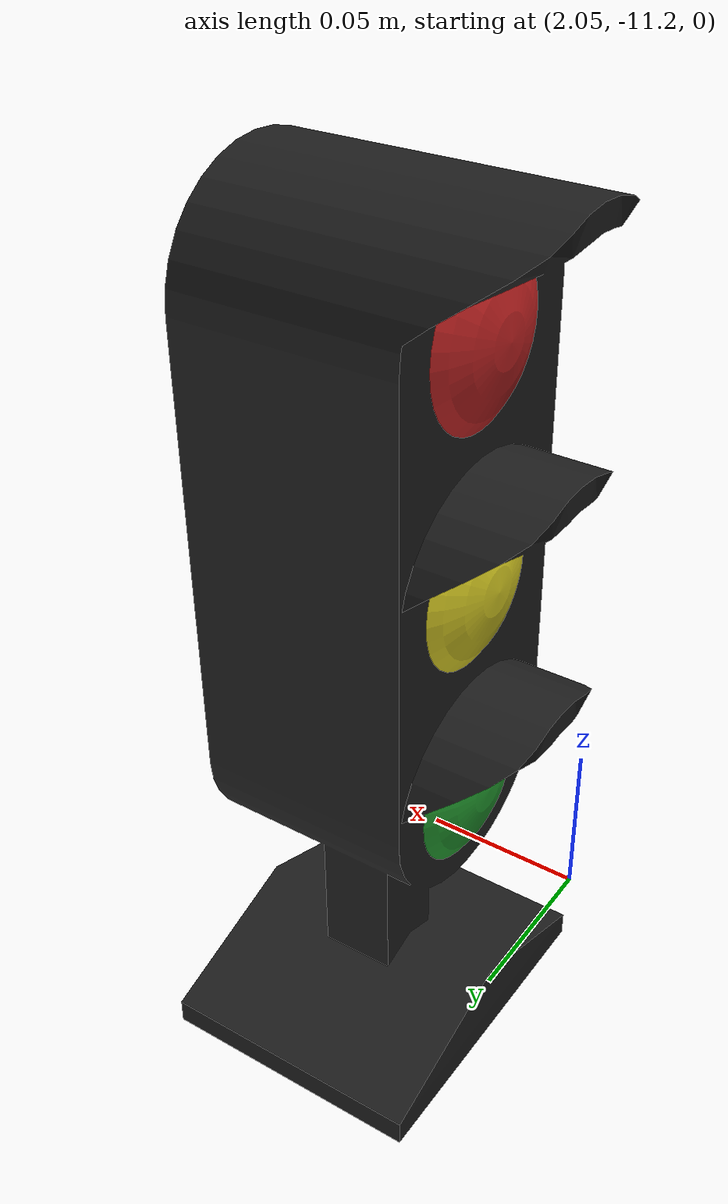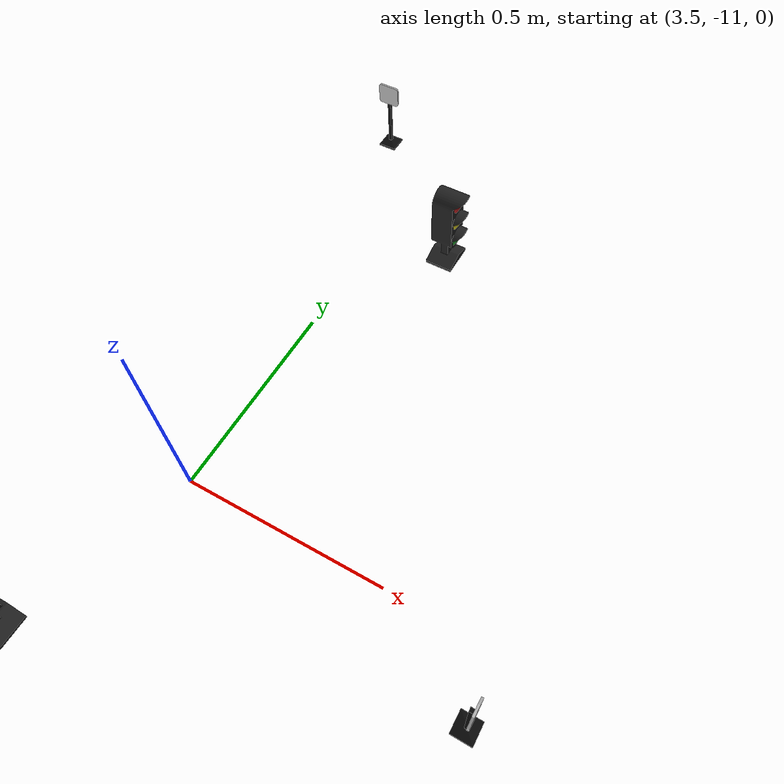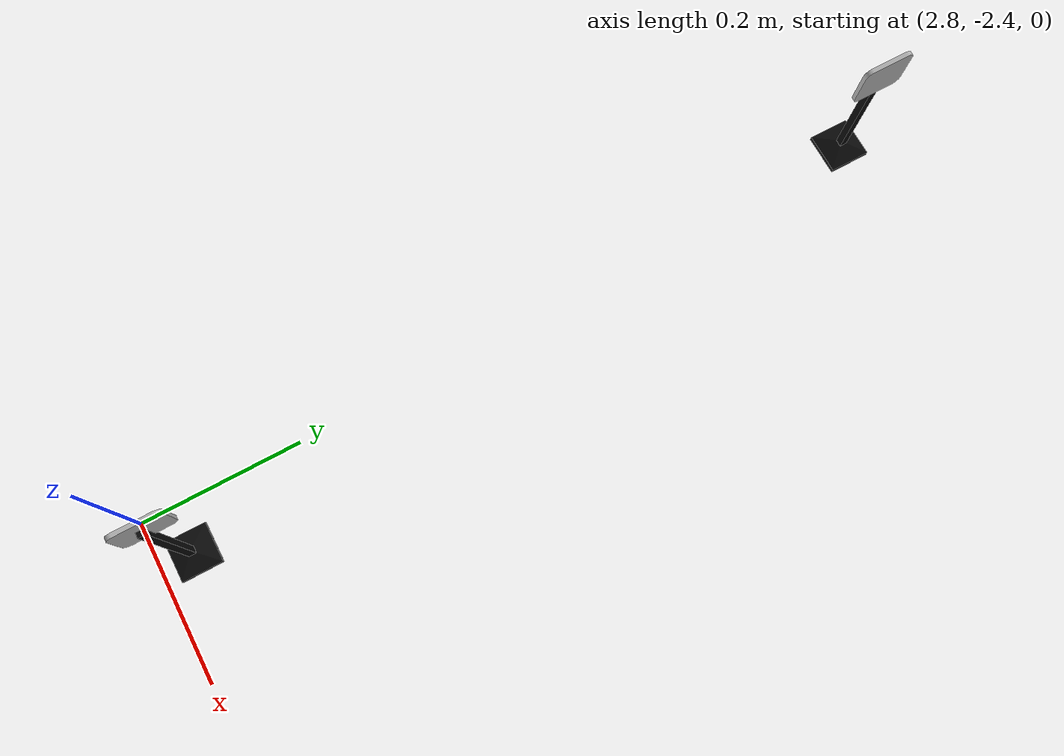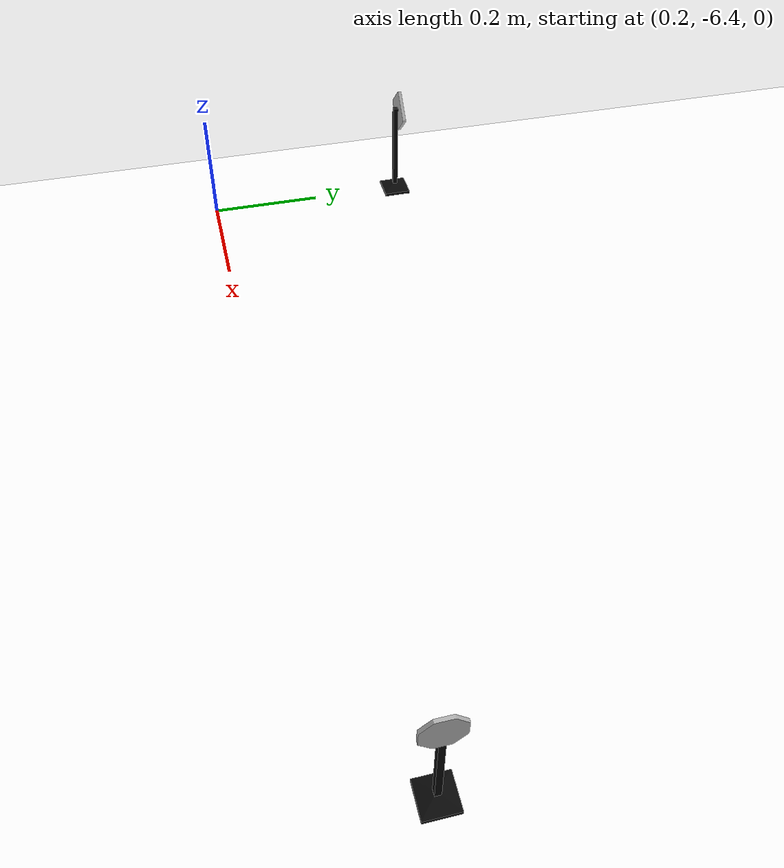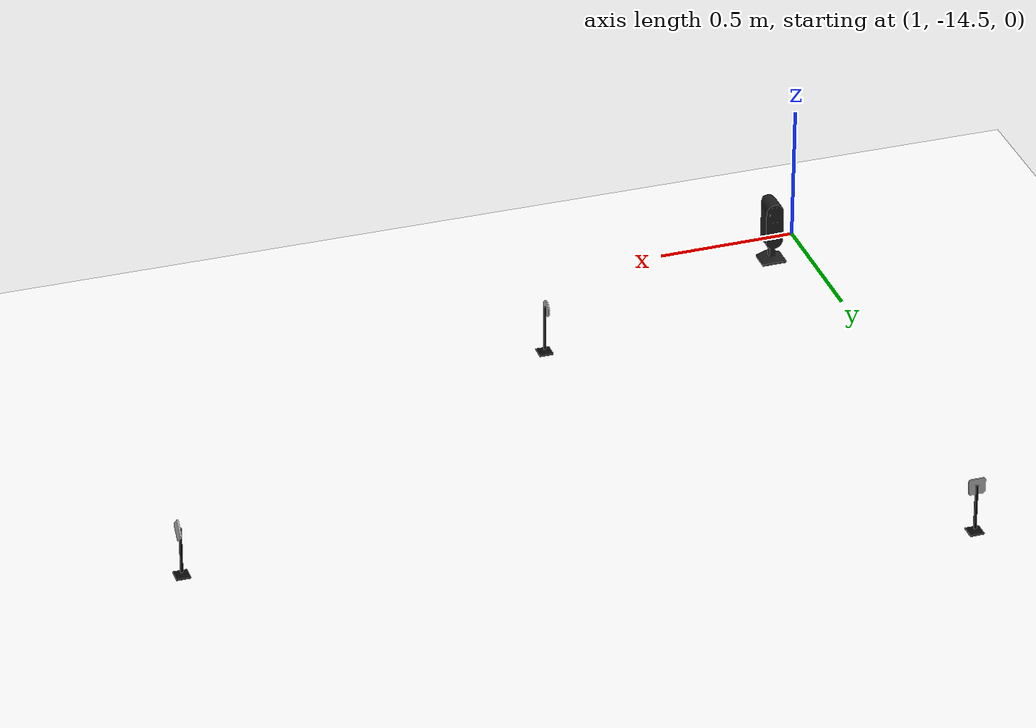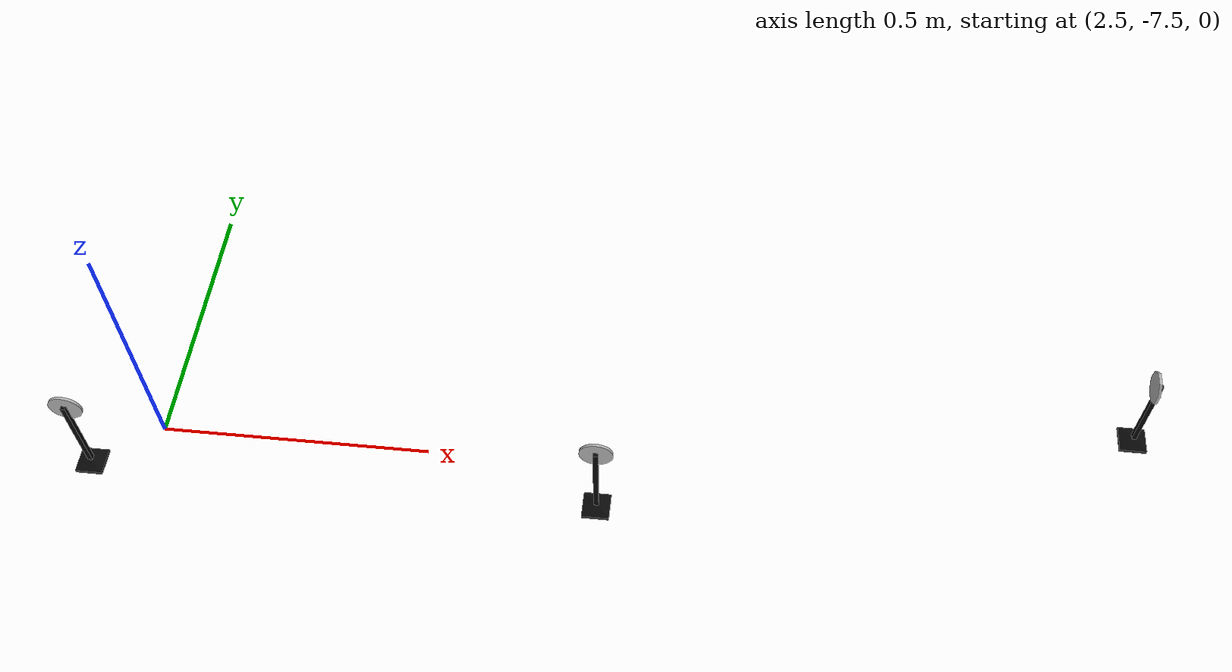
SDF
<sdf version="1.7">
 <world name="bfmc_official">
  <gravity>0 0 -9.8</gravity>
  <light name="c1" type="point">
   <pose>0 0 2 0 -0 0</pose>
   <diffuse>125 125 125 125</diffuse>
   <specular>50 50 50 50</specular>
   <attenuation><range>20</range><constant>0.3</constant><quadratic>0</quadratic><linear>0</linear></attenuation>
   <cast_shadows>0</cast_shadows>
   <direction>0 0 -1</direction>
   <spot><inner_angle>0</inner_angle><outer_angle>0</outer_angle><falloff>0</falloff></spot>
  </light>
  <light name="c2" type="point">
   <pose>15 0 2 0 -0 0</pose>
   <diffuse>125 125 125 125</diffuse>
   <specular>50 50 50 50</specular>
   <attenuation><range>20</range><constant>0.3</constant><quadratic>0</quadratic><linear>0</linear></attenuation>
   <cast_shadows>0</cast_shadows>
   <direction>0 0 -1</direction>
   <spot><inner_angle>0</inner_angle><outer_angle>0</outer_angle><falloff>0</falloff></spot>
  </light>
  <light name="c3" type="point">
   <pose>0 -15 2 0 -0 0</pose>
   <diffuse>125 125 125 125</diffuse>
   <specular>50 50 50 50</specular>
   <attenuation><range>20</range><constant>0.3</constant><quadratic>0</quadratic><linear>0</linear></attenuation>
   <cast_shadows>0</cast_shadows>
   <direction>0 0 -1</direction>
   <spot><inner_angle>0</inner_angle><outer_angle>0</outer_angle><falloff>0</falloff></spot>
  </light>
  <light name="c4" type="point">
   <pose>15 -15 2 0 -0 0</pose>
   <diffuse>125 125 125 125</diffuse>
   <specular>50 50 50 50</specular>
   <attenuation><range>50</range><constant>0.3</constant><quadratic>0</quadratic><linear>0</linear></attenuation>
   <cast_shadows>0</cast_shadows>
   <direction>0 0 -1</direction>
   <spot><inner_angle>0</inner_angle><outer_angle>0</outer_angle><falloff>0</falloff></spot>
  </light>
  <model name="track">
   <static>1</static>
   <link name="link">
    <collision name="collision">
     <geometry><plane><normal>0 0 1</normal><size>14.68 14.99</size></plane></geometry>
     <surface>
      <contact><collide_bitmask>65535</collide_bitmask></contact>
      <friction><ode><mu>1</mu><mu2>1</mu2></ode></friction>
     </surface>
    </collision>
    <visual name="visual">
     <geometry><plane><normal>0 0 1</normal><size>14.68 14.99</size></plane></geometry>
     <material>
      <ambient>1 1 1 1</ambient>
      <diffuse>1 1 1 1</diffuse>
      <specular>0 0 0 0</specular>
      <emissive>1 1 1 1</emissive>
      <script>
       <uri>model://track/materials/scripts</uri>
       <uri>model://track/materials/textures</uri>
       <name>BFMC_MATERIAL</name>
      </script>
     </material>
    </visual>
   </link>
   <pose>7.34 -7.495 0 0 -0 0</pose>
  </model>
  <magnetic_field>6e-06 2.3e-05 -4.2e-05</magnetic_field>
  <atmosphere type="adiabatic"/>
  <physics name="default_physics" default="0" type="ode">
   <max_step_size>0.001</max_step_size>
   <real_time_factor>1</real_time_factor>
   <real_time_update_rate>1000</real_time_update_rate>
  </physics>
  <scene><ambient>0.4 0.4 0.4 1</ambient><background>0.7 0.7 0.7 1</background><shadows>1</shadows></scene>
  <audio><device>default</device></audio>
  <spherical_coordinates>
   <surface_model>EARTH_WGS84</surface_model>
   <latitude_deg>0</latitude_deg>
   <longitude_deg>0</longitude_deg>
   <elevation>0</elevation>
   <heading_deg>0</heading_deg>
  </spherical_coordinates>
  <model name="priority_sign0">
   <static>1</static>
   <link name="sign_leg">
    <inertial>
     <mass>0.5</mass>
     <inertia>
      <ixx>0.166667</ixx>
      <ixy>0</ixy>
      <ixz>0</ixz>
      <iyy>0.166667</iyy>
      <iyz>0</iyz>
      <izz>0.166667</izz>
     </inertia>
     <pose>0 0 -0.078998 0 -0 0</pose>
    </inertial>
    <pose>0.002193 -0.000682 -0.07606 0 -0 0</pose>
    <self_collide>1</self_collide>
    <enable_wind>1</enable_wind>
    <visual name="visual">
     <geometry><mesh><uri>model://subassembly/meshes/sign_leg.dae</uri><scale>1 1 1</scale></mesh></geometry>
    </visual>
    <collision name="collision">
     <geometry><mesh><uri>model://subassembly/meshes/sign_leg.dae</uri><scale>1 1 1</scale></mesh></geometry>
     <surface>
      <friction>
       <ode><mu>0.46</mu><mu2>1</mu2><fdir1>0 0 0</fdir1><slip1>0</slip1><slip2>0</slip2></ode>
       <torsional>
        <coefficient>1</coefficient>
        <patch_radius>0</patch_radius>
        <surface_radius>0</surface_radius>
        <use_patch_radius>1</use_patch_radius>
        <ode><slip>0</slip></ode>
       </torsional>
      </friction>
      <bounce><restitution_coefficient>0</restitution_coefficient><threshold>1e+06</threshold></bounce>
      <contact>
       <collide_without_contact>0</collide_without_contact>
       <collide_without_contact_bitmask>1</collide_without_contact_bitmask>
       <collide_bitmask>1</collide_bitmask>
       <ode>
        <soft_cfm>0</soft_cfm>
        <soft_erp>0.2</soft_erp>
        <kp>1e+13</kp>
        <kd>1</kd>
        <max_vel>0.01</max_vel>
        <min_depth>0</min_depth>
       </ode>
       <bullet>
        <split_impulse>1</split_impulse>
        <split_impulse_penetration_threshold>-0.01</split_impulse_penetration_threshold>
        <soft_cfm>0</soft_cfm>
        <soft_erp>0.2</soft_erp>
        <kp>1e+13</kp>
        <kd>1</kd>
       </bullet>
      </contact>
     </surface>
    </collision>
   </link>
   <link name="caro_support">
    <inertial>
     <mass>0.022</mass>
     <inertia>
      <ixx>0.166667</ixx>
      <ixy>0</ixy>
      <ixz>0</ixz>
      <iyy>0.166667</iyy>
      <iyz>0</iyz>
      <izz>0.166667</izz>
     </inertia>
    </inertial>
    <pose>-0.002193 0.000682 0.09894 0 -0 3.14159</pose>
    <self_collide>1</self_collide>
    <enable_wind>1</enable_wind>
    <visual name="visual">
     <geometry>
      <mesh><uri>model://priority_sign/meshes/priority_sign.dae</uri><scale>1 1 1</scale></mesh>
     </geometry>
     <material>
      <lighting>1</lighting>
      <script>
       <uri>model://priority_sign/materials/scripts</uri>
       <uri>model://priority_sign/materials/textures</uri>
       <name>PRIORITY_SIGN</name>
      </script>
      <shader type="vertex"><normal_map>__default__</normal_map></shader>
      <ambient>0.3 0.3 0.3 1</ambient>
      <diffuse>0.7 0.7 0.7 1</diffuse>
      <specular>0.01 0.01 0.01 1</specular>
      <emissive>0 0 0 1</emissive>
     </material>
    </visual>
    <collision name="collision">
     <geometry>
      <mesh><uri>model://priority_sign/meshes/priority_sign.dae</uri><scale>1 1 1</scale></mesh>
     </geometry>
     <surface>
      <friction>
       <ode><mu>0.46</mu><mu2>1</mu2><fdir1>0 0 0</fdir1><slip1>0</slip1><slip2>0</slip2></ode>
       <torsional>
        <coefficient>1</coefficient>
        <patch_radius>0</patch_radius>
        <surface_radius>0</surface_radius>
        <use_patch_radius>1</use_patch_radius>
        <ode><slip>0</slip></ode>
       </torsional>
      </friction>
      <bounce><restitution_coefficient>0</restitution_coefficient><threshold>1e+06</threshold></bounce>
      <contact>
       <collide_without_contact>0</collide_without_contact>
       <collide_without_contact_bitmask>1</collide_without_contact_bitmask>
       <collide_bitmask>1</collide_bitmask>
       <ode>
        <soft_cfm>0</soft_cfm>
        <soft_erp>0.2</soft_erp>
        <kp>1e+13</kp>
        <kd>1</kd>
        <max_vel>0.01</max_vel>
        <min_depth>0</min_depth>
       </ode>
       <bullet>
        <split_impulse>1</split_impulse>
        <split_impulse_penetration_threshold>-0.01</split_impulse_penetration_threshold>
        <soft_cfm>0</soft_cfm>
        <soft_erp>0.2</soft_erp>
        <kp>1e+13</kp>
        <kd>1</kd>
       </bullet>
      </contact>
     </surface>
    </collision>
   </link>
   <joint name="support_to_leg_joint" type="fixed">
    <parent>caro_support</parent>
    <child>sign_leg</child>
    <physics>
     <ode><limit><cfm>0</cfm><erp>0.2</erp></limit><suspension><cfm>0</cfm><erp>0.2</erp></suspension></ode>
    </physics>
   </joint>
   <static>1</static>
   <pose>3.675 -13.05 0.078998 0 -0 3.14159</pose>
  </model>
  <model name="priority_sign2">
   <static>1</static>
   <link name="sign_leg">
    <inertial>
     <mass>0.5</mass>
     <inertia>
      <ixx>0.166667</ixx>
      <ixy>0</ixy>
      <ixz>0</ixz>
      <iyy>0.166667</iyy>
      <iyz>0</iyz>
      <izz>0.166667</izz>
     </inertia>
     <pose>0 0 -0.078998 0 -0 0</pose>
    </inertial>
    <pose>0.002193 -0.000682 -0.07606 0 -0 0</pose>
    <self_collide>1</self_collide>
    <enable_wind>1</enable_wind>
    <visual name="visual">
     <geometry><mesh><uri>model://subassembly/meshes/sign_leg.dae</uri><scale>1 1 1</scale></mesh></geometry>
    </visual>
    <collision name="collision">
     <geometry><mesh><uri>model://subassembly/meshes/sign_leg.dae</uri><scale>1 1 1</scale></mesh></geometry>
     <surface>
      <friction>
       <ode><mu>0.46</mu><mu2>1</mu2><fdir1>0 0 0</fdir1><slip1>0</slip1><slip2>0</slip2></ode>
       <torsional>
        <coefficient>1</coefficient>
        <patch_radius>0</patch_radius>
        <surface_radius>0</surface_radius>
        <use_patch_radius>1</use_patch_radius>
        <ode><slip>0</slip></ode>
       </torsional>
      </friction>
      <bounce><restitution_coefficient>0</restitution_coefficient><threshold>1e+06</threshold></bounce>
      <contact>
       <collide_without_contact>0</collide_without_contact>
       <collide_without_contact_bitmask>1</collide_without_contact_bitmask>
       <collide_bitmask>1</collide_bitmask>
       <ode>
        <soft_cfm>0</soft_cfm>
        <soft_erp>0.2</soft_erp>
        <kp>1e+13</kp>
        <kd>1</kd>
        <max_vel>0.01</max_vel>
        <min_depth>0</min_depth>
       </ode>
       <bullet>
        <split_impulse>1</split_impulse>
        <split_impulse_penetration_threshold>-0.01</split_impulse_penetration_threshold>
        <soft_cfm>0</soft_cfm>
        <soft_erp>0.2</soft_erp>
        <kp>1e+13</kp>
        <kd>1</kd>
       </bullet>
      </contact>
     </surface>
    </collision>
   </link>
   <link name="caro_support">
    <inertial>
     <mass>0.022</mass>
     <inertia>
      <ixx>0.166667</ixx>
      <ixy>0</ixy>
      <ixz>0</ixz>
      <iyy>0.166667</iyy>
      <iyz>0</iyz>
      <izz>0.166667</izz>
     </inertia>
    </inertial>
    <pose>-0.002193 0.000682 0.09894 0 -0 3.14159</pose>
    <self_collide>1</self_collide>
    <enable_wind>1</enable_wind>
    <visual name="visual">
     <geometry>
      <mesh><uri>model://priority_sign/meshes/priority_sign.dae</uri><scale>1 1 1</scale></mesh>
     </geometry>
     <material>
      <lighting>1</lighting>
      <script>
       <uri>model://priority_sign/materials/scripts</uri>
       <uri>model://priority_sign/materials/textures</uri>
       <name>PRIORITY_SIGN</name>
      </script>
      <shader type="vertex"><normal_map>__default__</normal_map></shader>
      <ambient>0.3 0.3 0.3 1</ambient>
      <diffuse>0.7 0.7 0.7 1</diffuse>
      <specular>0.01 0.01 0.01 1</specular>
      <emissive>0 0 0 1</emissive>
     </material>
    </visual>
    <collision name="collision">
     <geometry>
      <mesh><uri>model://priority_sign/meshes/priority_sign.dae</uri><scale>1 1 1</scale></mesh>
     </geometry>
     <surface>
      <friction>
       <ode><mu>0.46</mu><mu2>1</mu2><fdir1>0 0 0</fdir1><slip1>0</slip1><slip2>0</slip2></ode>
       <torsional>
        <coefficient>1</coefficient>
        <patch_radius>0</patch_radius>
        <surface_radius>0</surface_radius>
        <use_patch_radius>1</use_patch_radius>
        <ode><slip>0</slip></ode>
       </torsional>
      </friction>
      <bounce><restitution_coefficient>0</restitution_coefficient><threshold>1e+06</threshold></bounce>
      <contact>
       <collide_without_contact>0</collide_without_contact>
       <collide_without_contact_bitmask>1</collide_without_contact_bitmask>
       <collide_bitmask>1</collide_bitmask>
       <ode>
        <soft_cfm>0</soft_cfm>
        <soft_erp>0.2</soft_erp>
        <kp>1e+13</kp>
        <kd>1</kd>
        <max_vel>0.01</max_vel>
        <min_depth>0</min_depth>
       </ode>
       <bullet>
        <split_impulse>1</split_impulse>
        <split_impulse_penetration_threshold>-0.01</split_impulse_penetration_threshold>
        <soft_cfm>0</soft_cfm>
        <soft_erp>0.2</soft_erp>
        <kp>1e+13</kp>
        <kd>1</kd>
       </bullet>
      </contact>
     </surface>
    </collision>
   </link>
   <joint name="support_to_leg_joint" type="fixed">
    <parent>caro_support</parent>
    <child>sign_leg</child>
    <physics>
     <ode><limit><cfm>0</cfm><erp>0.2</erp></limit><suspension><cfm>0</cfm><erp>0.2</erp></suspension></ode>
    </physics>
   </joint>
   <static>1</static>
   <pose>5.544 -11.381 0.078998 0 -0 1.5708</pose>
  </model>
  <model name="roundabout_sign1">
   <static>1</static>
   <link name="sign_leg">
    <inertial>
     <mass>0.5</mass>
     <inertia>
      <ixx>0.166667</ixx>
      <ixy>0</ixy>
      <ixz>0</ixz>
      <iyy>0.166667</iyy>
      <iyz>0</iyz>
      <izz>0.166667</izz>
     </inertia>
     <pose>0 0 -0.078998 0 -0 0</pose>
    </inertial>
    <pose>0.002193 -0.000682 -0.07606 0 -0 0</pose>
    <self_collide>1</self_collide>
    <enable_wind>1</enable_wind>
    <visual name="visual">
     <geometry><mesh><uri>model://subassembly/meshes/sign_leg.dae</uri><scale>1 1 1</scale></mesh></geometry>
    </visual>
    <collision name="collision">
     <geometry><mesh><uri>model://subassembly/meshes/sign_leg.dae</uri><scale>1 1 1</scale></mesh></geometry>
     <surface>
      <friction>
       <ode><mu>0.46</mu><mu2>1</mu2><fdir1>0 0 0</fdir1><slip1>0</slip1><slip2>0</slip2></ode>
       <torsional>
        <coefficient>1</coefficient>
        <patch_radius>0</patch_radius>
        <surface_radius>0</surface_radius>
        <use_patch_radius>1</use_patch_radius>
        <ode><slip>0</slip></ode>
       </torsional>
      </friction>
      <bounce><restitution_coefficient>0</restitution_coefficient><threshold>1e+06</threshold></bounce>
      <contact>
       <collide_without_contact>0</collide_without_contact>
       <collide_without_contact_bitmask>1</collide_without_contact_bitmask>
       <collide_bitmask>1</collide_bitmask>
       <ode>
        <soft_cfm>0</soft_cfm>
        <soft_erp>0.2</soft_erp>
        <kp>1e+13</kp>
        <kd>1</kd>
        <max_vel>0.01</max_vel>
        <min_depth>0</min_depth>
       </ode>
       <bullet>
        <split_impulse>1</split_impulse>
        <split_impulse_penetration_threshold>-0.01</split_impulse_penetration_threshold>
        <soft_cfm>0</soft_cfm>
        <soft_erp>0.2</soft_erp>
        <kp>1e+13</kp>
        <kd>1</kd>
       </bullet>
      </contact>
     </surface>
    </collision>
   </link>
   <link name="triangular_support">
    <inertial>
     <mass>0.022</mass>
     <inertia>
      <ixx>0.166667</ixx>
      <ixy>0</ixy>
      <ixz>0</ixz>
      <iyy>0.166667</iyy>
      <iyz>0</iyz>
      <izz>0.166667</izz>
     </inertia>
    </inertial>
    <pose>-0.002193 0.000682 0.09894 0 -0 3.14159</pose>
    <self_collide>1</self_collide>
    <enable_wind>1</enable_wind>
    <visual name="visual">
     <geometry>
      <mesh><uri>model://roundabout_sign/meshes/roundabout_sign.dae</uri><scale>1 1 1</scale></mesh>
     </geometry>
     <material>
      <lighting>1</lighting>
      <script>
       <uri>model://roundabout_sign/materials/scripts</uri>
       <uri>model://roundabout_sign/materials/textures</uri>
       <name>ROUNDABOUT_SIGN</name>
      </script>
      <shader type="vertex"><normal_map>__default__</normal_map></shader>
      <ambient>0.3 0.3 0.3 1</ambient>
      <diffuse>0.7 0.7 0.7 1</diffuse>
      <specular>0.01 0.01 0.01 1</specular>
      <emissive>0 0 0 1</emissive>
     </material>
    </visual>
    <collision name="collision">
     <geometry>
      <mesh><uri>model://roundabout_sign/meshes/roundabout_sign.dae</uri><scale>1 1 1</scale></mesh>
     </geometry>
     <surface>
      <friction>
       <ode><mu>0.46</mu><mu2>1</mu2><fdir1>0 0 0</fdir1><slip1>0</slip1><slip2>0</slip2></ode>
       <torsional>
        <coefficient>1</coefficient>
        <patch_radius>0</patch_radius>
        <surface_radius>0</surface_radius>
        <use_patch_radius>1</use_patch_radius>
        <ode><slip>0</slip></ode>
       </torsional>
      </friction>
      <bounce><restitution_coefficient>0</restitution_coefficient><threshold>1e+06</threshold></bounce>
      <contact>
       <collide_without_contact>0</collide_without_contact>
       <collide_without_contact_bitmask>1</collide_without_contact_bitmask>
       <collide_bitmask>1</collide_bitmask>
       <ode>
        <soft_cfm>0</soft_cfm>
        <soft_erp>0.2</soft_erp>
        <kp>1e+13</kp>
        <kd>1</kd>
        <max_vel>0.01</max_vel>
        <min_depth>0</min_depth>
       </ode>
       <bullet>
        <split_impulse>1</split_impulse>
        <split_impulse_penetration_threshold>-0.01</split_impulse_penetration_threshold>
        <soft_cfm>0</soft_cfm>
        <soft_erp>0.2</soft_erp>
        <kp>1e+13</kp>
        <kd>1</kd>
       </bullet>
      </contact>
     </surface>
    </collision>
   </link>
   <joint name="support_to_leg_joint" type="fixed">
    <parent>triangular_support</parent>
    <child>sign_leg</child>
    <physics>
     <ode><limit><cfm>0</cfm><erp>0.2</erp></limit><suspension><cfm>0</cfm><erp>0.2</erp></suspension></ode>
    </physics>
   </joint>
   <static>1</static>
   <pose>10.32 -4.869 0.078998 0 -0 1.5708</pose>
  </model>
  <model name="crosswalk_sign4">
   <static>1</static>
   <link name="sign_leg">
    <inertial>
     <mass>0.5</mass>
     <inertia>
      <ixx>0.166667</ixx>
      <ixy>0</ixy>
      <ixz>0</ixz>
      <iyy>0.166667</iyy>
      <iyz>0</iyz>
      <izz>0.166667</izz>
     </inertia>
     <pose>0 0 -0.078998 0 -0 0</pose>
    </inertial>
    <pose>0.002193 -0.000682 -0.07606 0 -0 0</pose>
    <self_collide>1</self_collide>
    <enable_wind>1</enable_wind>
    <visual name="visual">
     <geometry><mesh><uri>model://subassembly/meshes/sign_leg.dae</uri><scale>1 1 1</scale></mesh></geometry>
    </visual>
    <collision name="collision">
     <geometry><mesh><uri>model://subassembly/meshes/sign_leg.dae</uri><scale>1 1 1</scale></mesh></geometry>
     <surface>
      <friction>
       <ode><mu>0.46</mu><mu2>1</mu2><fdir1>0 0 0</fdir1><slip1>0</slip1><slip2>0</slip2></ode>
       <torsional>
        <coefficient>1</coefficient>
        <patch_radius>0</patch_radius>
        <surface_radius>0</surface_radius>
        <use_patch_radius>1</use_patch_radius>
        <ode><slip>0</slip></ode>
       </torsional>
      </friction>
      <bounce><restitution_coefficient>0</restitution_coefficient><threshold>1e+06</threshold></bounce>
      <contact>
       <collide_without_contact>0</collide_without_contact>
       <collide_without_contact_bitmask>1</collide_without_contact_bitmask>
       <collide_bitmask>1</collide_bitmask>
       <ode>
        <soft_cfm>0</soft_cfm>
        <soft_erp>0.2</soft_erp>
        <kp>1e+13</kp>
        <kd>1</kd>
        <max_vel>0.01</max_vel>
        <min_depth>0</min_depth>
       </ode>
       <bullet>
        <split_impulse>1</split_impulse>
        <split_impulse_penetration_threshold>-0.01</split_impulse_penetration_threshold>
        <soft_cfm>0</soft_cfm>
        <soft_erp>0.2</soft_erp>
        <kp>1e+13</kp>
        <kd>1</kd>
       </bullet>
      </contact>
     </surface>
    </collision>
   </link>
   <link name="rectangular_support">
    <inertial>
     <mass>0.022</mass>
     <inertia>
      <ixx>0.166667</ixx>
      <ixy>0</ixy>
      <ixz>0</ixz>
      <iyy>0.166667</iyy>
      <iyz>0</iyz>
      <izz>0.166667</izz>
     </inertia>
    </inertial>
    <pose>-0 0.000682 0.09894 0 -0 3.14159</pose>
    <self_collide>1</self_collide>
    <enable_wind>1</enable_wind>
    <visual name="visual">
     <geometry>
      <mesh><uri>model://crosswalk_sign/meshes/pedestrian_sign.dae</uri><scale>10 10 10</scale></mesh>
     </geometry>
     <material>
      <lighting>1</lighting>
      <script>
       <uri>model://crosswalk_sign/materials/scripts</uri>
       <uri>model://crosswalk_sign/materials/textures</uri>
       <name>PEDESTRIAN_SIGN</name>
      </script>
      <shader type="vertex"><normal_map>__default__</normal_map></shader>
      <ambient>0.3 0.3 0.3 1</ambient>
      <diffuse>0.7 0.7 0.7 1</diffuse>
      <specular>0.01 0.01 0.01 1</specular>
      <emissive>0 0 0 1</emissive>
     </material>
    </visual>
    <collision name="collision">
     <geometry>
      <mesh><uri>model://crosswalk_sign/meshes/pedestrian_sign.dae</uri><scale>10 10 10</scale></mesh>
     </geometry>
     <surface>
      <friction>
       <ode><mu>0.46</mu><mu2>1</mu2><fdir1>0 0 0</fdir1><slip1>0</slip1><slip2>0</slip2></ode>
       <torsional>
        <coefficient>1</coefficient>
        <patch_radius>0</patch_radius>
        <surface_radius>0</surface_radius>
        <use_patch_radius>1</use_patch_radius>
        <ode><slip>0</slip></ode>
       </torsional>
      </friction>
      <bounce><restitution_coefficient>0</restitution_coefficient><threshold>1e+06</threshold></bounce>
      <contact>
       <collide_without_contact>0</collide_without_contact>
       <collide_without_contact_bitmask>1</collide_without_contact_bitmask>
       <collide_bitmask>1</collide_bitmask>
       <ode>
        <soft_cfm>0</soft_cfm>
        <soft_erp>0.2</soft_erp>
        <kp>1e+13</kp>
        <kd>1</kd>
        <max_vel>0.01</max_vel>
        <min_depth>0</min_depth>
       </ode>
       <bullet>
        <split_impulse>1</split_impulse>
        <split_impulse_penetration_threshold>-0.01</split_impulse_penetration_threshold>
        <soft_cfm>0</soft_cfm>
        <soft_erp>0.2</soft_erp>
        <kp>1e+13</kp>
        <kd>1</kd>
       </bullet>
      </contact>
     </surface>
    </collision>
   </link>
   <joint name="support_to_leg_joint" type="fixed">
    <parent>rectangular_support</parent>
    <child>sign_leg</child>
    <physics>
     <ode><limit><cfm>0</cfm><erp>0.2</erp></limit><suspension><cfm>0</cfm><erp>0.2</erp></suspension></ode>
    </physics>
   </joint>
   <static>1</static>
   <pose>1.109 -12.486 0.078998 0 -0 1.5708</pose>
  </model>
  <model name="stop_sign4">
   <static>1</static>
   <link name="sign_leg">
    <inertial>
     <mass>0.5</mass>
     <inertia>
      <ixx>0.166667</ixx>
      <ixy>0</ixy>
      <ixz>0</ixz>
      <iyy>0.166667</iyy>
      <iyz>0</iyz>
      <izz>0.166667</izz>
     </inertia>
     <pose>0 0 -0.078998 0 -0 0</pose>
    </inertial>
    <pose>0.002193 -0.000682 -0.07606 0 -0 0</pose>
    <self_collide>1</self_collide>
    <enable_wind>1</enable_wind>
    <visual name="visual">
     <geometry><mesh><uri>model://subassembly/meshes/sign_leg.dae</uri><scale>1 1 1</scale></mesh></geometry>
    </visual>
    <collision name="collision">
     <geometry><mesh><uri>model://subassembly/meshes/sign_leg.dae</uri><scale>1 1 1</scale></mesh></geometry>
     <surface>
      <friction>
       <ode><mu>0.46</mu><mu2>1</mu2><fdir1>0 0 0</fdir1><slip1>0</slip1><slip2>0</slip2></ode>
       <torsional>
        <coefficient>1</coefficient>
        <patch_radius>0</patch_radius>
        <surface_radius>0</surface_radius>
        <use_patch_radius>1</use_patch_radius>
        <ode><slip>0</slip></ode>
       </torsional>
      </friction>
      <bounce><restitution_coefficient>0</restitution_coefficient><threshold>1e+06</threshold></bounce>
      <contact>
       <collide_without_contact>0</collide_without_contact>
       <collide_without_contact_bitmask>1</collide_without_contact_bitmask>
       <collide_bitmask>1</collide_bitmask>
       <ode>
        <soft_cfm>0</soft_cfm>
        <soft_erp>0.2</soft_erp>
        <kp>1e+13</kp>
        <kd>1</kd>
        <max_vel>0.01</max_vel>
        <min_depth>0</min_depth>
       </ode>
       <bullet>
        <split_impulse>1</split_impulse>
        <split_impulse_penetration_threshold>-0.01</split_impulse_penetration_threshold>
        <soft_cfm>0</soft_cfm>
        <soft_erp>0.2</soft_erp>
        <kp>1e+13</kp>
        <kd>1</kd>
       </bullet>
      </contact>
     </surface>
    </collision>
   </link>
   <link name="octagonal_support">
    <inertial>
     <mass>0.022</mass>
     <inertia>
      <ixx>0.166667</ixx>
      <ixy>0</ixy>
      <ixz>0</ixz>
      <iyy>0.166667</iyy>
      <iyz>0</iyz>
      <izz>0.166667</izz>
     </inertia>
    </inertial>
    <pose>-0.002193 0.000682 0.09894 0 -0 3.14159</pose>
    <self_collide>1</self_collide>
    <enable_wind>1</enable_wind>
    <visual name="visual">
     <geometry><mesh><uri>model://stop_sign/meshes/stop_sign.dae</uri><scale>1 1 1</scale></mesh></geometry>
     <material>
      <lighting>1</lighting>
      <script>
       <uri>model://stop_sign/materials/scripts</uri>
       <uri>model://stop_sign/materials/textures</uri>
       <name>STOP_SIGN</name>
      </script>
      <shader type="vertex"><normal_map>__default__</normal_map></shader>
      <ambient>0.3 0.3 0.3 1</ambient>
      <diffuse>0.7 0.7 0.7 1</diffuse>
      <specular>0.01 0.01 0.01 1</specular>
      <emissive>0 0 0 1</emissive>
     </material>
    </visual>
    <collision name="collision">
     <geometry><mesh><uri>model://stop_sign/meshes/stop_sign.dae</uri><scale>1 1 1</scale></mesh></geometry>
     <surface>
      <friction>
       <ode><mu>0.46</mu><mu2>1</mu2><fdir1>0 0 0</fdir1><slip1>0</slip1><slip2>0</slip2></ode>
       <torsional>
        <coefficient>1</coefficient>
        <patch_radius>0</patch_radius>
        <surface_radius>0</surface_radius>
        <use_patch_radius>1</use_patch_radius>
        <ode><slip>0</slip></ode>
       </torsional>
      </friction>
      <bounce><restitution_coefficient>0</restitution_coefficient><threshold>1e+06</threshold></bounce>
      <contact>
       <collide_without_contact>0</collide_without_contact>
       <collide_without_contact_bitmask>1</collide_without_contact_bitmask>
       <collide_bitmask>1</collide_bitmask>
       <ode>
        <soft_cfm>0</soft_cfm>
        <soft_erp>0.2</soft_erp>
        <kp>1e+13</kp>
        <kd>1</kd>
        <max_vel>0.01</max_vel>
        <min_depth>0</min_depth>
       </ode>
       <bullet>
        <split_impulse>1</split_impulse>
        <split_impulse_penetration_threshold>-0.01</split_impulse_penetration_threshold>
        <soft_cfm>0</soft_cfm>
        <soft_erp>0.2</soft_erp>
        <kp>1e+13</kp>
        <kd>1</kd>
       </bullet>
      </contact>
     </surface>
    </collision>
   </link>
   <joint name="support_to_leg_joint" type="fixed">
    <parent>octagonal_support</parent>
    <child>sign_leg</child>
    <physics>
     <ode><limit><cfm>0</cfm><erp>0.2</erp></limit><suspension><cfm>0</cfm><erp>0.2</erp></suspension></ode>
    </physics>
   </joint>
   <static>1</static>
   <pose>12.603 -4.515 0.078998 0 -0 1.5708</pose>
  </model>
  <model name="priority_sign1">
   <static>1</static>
   <link name="sign_leg">
    <inertial>
     <mass>0.5</mass>
     <inertia>
      <ixx>0.166667</ixx>
      <ixy>0</ixy>
      <ixz>0</ixz>
      <iyy>0.166667</iyy>
      <iyz>0</iyz>
      <izz>0.166667</izz>
     </inertia>
     <pose>0 0 -0.078998 0 -0 0</pose>
    </inertial>
    <pose>0.002193 -0.000682 -0.07606 0 -0 0</pose>
    <self_collide>1</self_collide>
    <enable_wind>1</enable_wind>
    <visual name="visual">
     <geometry><mesh><uri>model://subassembly/meshes/sign_leg.dae</uri><scale>1 1 1</scale></mesh></geometry>
    </visual>
    <collision name="collision">
     <geometry><mesh><uri>model://subassembly/meshes/sign_leg.dae</uri><scale>1 1 1</scale></mesh></geometry>
     <surface>
      <friction>
       <ode><mu>0.46</mu><mu2>1</mu2><fdir1>0 0 0</fdir1><slip1>0</slip1><slip2>0</slip2></ode>
       <torsional>
        <coefficient>1</coefficient>
        <patch_radius>0</patch_radius>
        <surface_radius>0</surface_radius>
        <use_patch_radius>1</use_patch_radius>
        <ode><slip>0</slip></ode>
       </torsional>
      </friction>
      <bounce><restitution_coefficient>0</restitution_coefficient><threshold>1e+06</threshold></bounce>
      <contact>
       <collide_without_contact>0</collide_without_contact>
       <collide_without_contact_bitmask>1</collide_without_contact_bitmask>
       <collide_bitmask>1</collide_bitmask>
       <ode>
        <soft_cfm>0</soft_cfm>
        <soft_erp>0.2</soft_erp>
        <kp>1e+13</kp>
        <kd>1</kd>
        <max_vel>0.01</max_vel>
        <min_depth>0</min_depth>
       </ode>
       <bullet>
        <split_impulse>1</split_impulse>
        <split_impulse_penetration_threshold>-0.01</split_impulse_penetration_threshold>
        <soft_cfm>0</soft_cfm>
        <soft_erp>0.2</soft_erp>
        <kp>1e+13</kp>
        <kd>1</kd>
       </bullet>
      </contact>
     </surface>
    </collision>
   </link>
   <link name="caro_support">
    <inertial>
     <mass>0.022</mass>
     <inertia>
      <ixx>0.166667</ixx>
      <ixy>0</ixy>
      <ixz>0</ixz>
      <iyy>0.166667</iyy>
      <iyz>0</iyz>
      <izz>0.166667</izz>
     </inertia>
    </inertial>
    <pose>-0.002193 0.000682 0.09894 0 -0 3.14159</pose>
    <self_collide>1</self_collide>
    <enable_wind>1</enable_wind>
    <visual name="visual">
     <geometry>
      <mesh><uri>model://priority_sign/meshes/priority_sign.dae</uri><scale>1 1 1</scale></mesh>
     </geometry>
     <material>
      <lighting>1</lighting>
      <script>
       <uri>model://priority_sign/materials/scripts</uri>
       <uri>model://priority_sign/materials/textures</uri>
       <name>PRIORITY_SIGN</name>
      </script>
      <shader type="vertex"><normal_map>__default__</normal_map></shader>
      <ambient>0.3 0.3 0.3 1</ambient>
      <diffuse>0.7 0.7 0.7 1</diffuse>
      <specular>0.01 0.01 0.01 1</specular>
      <emissive>0 0 0 1</emissive>
     </material>
    </visual>
    <collision name="collision">
     <geometry>
      <mesh><uri>model://priority_sign/meshes/priority_sign.dae</uri><scale>1 1 1</scale></mesh>
     </geometry>
     <surface>
      <friction>
       <ode><mu>0.46</mu><mu2>1</mu2><fdir1>0 0 0</fdir1><slip1>0</slip1><slip2>0</slip2></ode>
       <torsional>
        <coefficient>1</coefficient>
        <patch_radius>0</patch_radius>
        <surface_radius>0</surface_radius>
        <use_patch_radius>1</use_patch_radius>
        <ode><slip>0</slip></ode>
       </torsional>
      </friction>
      <bounce><restitution_coefficient>0</restitution_coefficient><threshold>1e+06</threshold></bounce>
      <contact>
       <collide_without_contact>0</collide_without_contact>
       <collide_without_contact_bitmask>1</collide_without_contact_bitmask>
       <collide_bitmask>1</collide_bitmask>
       <ode>
        <soft_cfm>0</soft_cfm>
        <soft_erp>0.2</soft_erp>
        <kp>1e+13</kp>
        <kd>1</kd>
        <max_vel>0.01</max_vel>
        <min_depth>0</min_depth>
       </ode>
       <bullet>
        <split_impulse>1</split_impulse>
        <split_impulse_penetration_threshold>-0.01</split_impulse_penetration_threshold>
        <soft_cfm>0</soft_cfm>
        <soft_erp>0.2</soft_erp>
        <kp>1e+13</kp>
        <kd>1</kd>
       </bullet>
      </contact>
     </surface>
    </collision>
   </link>
   <joint name="support_to_leg_joint" type="fixed">
    <parent>caro_support</parent>
    <child>sign_leg</child>
    <physics>
     <ode><limit><cfm>0</cfm><erp>0.2</erp></limit><suspension><cfm>0</cfm><erp>0.2</erp></suspension></ode>
    </physics>
   </joint>
   <static>1</static>
   <pose>0.204 -6.031 0.078998 0 0 -1.5708</pose>
  </model>
  <model name="priority_sign3">
   <static>1</static>
   <link name="sign_leg">
    <inertial>
     <mass>0.5</mass>
     <inertia>
      <ixx>0.166667</ixx>
      <ixy>0</ixy>
      <ixz>0</ixz>
      <iyy>0.166667</iyy>
      <iyz>0</iyz>
      <izz>0.166667</izz>
     </inertia>
     <pose>0 0 -0.078998 0 -0 0</pose>
    </inertial>
    <pose>0.002193 -0.000682 -0.07606 0 -0 0</pose>
    <self_collide>1</self_collide>
    <enable_wind>1</enable_wind>
    <visual name="visual">
     <geometry><mesh><uri>model://subassembly/meshes/sign_leg.dae</uri><scale>1 1 1</scale></mesh></geometry>
    </visual>
    <collision name="collision">
     <geometry><mesh><uri>model://subassembly/meshes/sign_leg.dae</uri><scale>1 1 1</scale></mesh></geometry>
     <surface>
      <friction>
       <ode><mu>0.46</mu><mu2>1</mu2><fdir1>0 0 0</fdir1><slip1>0</slip1><slip2>0</slip2></ode>
       <torsional>
        <coefficient>1</coefficient>
        <patch_radius>0</patch_radius>
        <surface_radius>0</surface_radius>
        <use_patch_radius>1</use_patch_radius>
        <ode><slip>0</slip></ode>
       </torsional>
      </friction>
      <bounce><restitution_coefficient>0</restitution_coefficient><threshold>1e+06</threshold></bounce>
      <contact>
       <collide_without_contact>0</collide_without_contact>
       <collide_without_contact_bitmask>1</collide_without_contact_bitmask>
       <collide_bitmask>1</collide_bitmask>
       <ode>
        <soft_cfm>0</soft_cfm>
        <soft_erp>0.2</soft_erp>
        <kp>1e+13</kp>
        <kd>1</kd>
        <max_vel>0.01</max_vel>
        <min_depth>0</min_depth>
       </ode>
       <bullet>
        <split_impulse>1</split_impulse>
        <split_impulse_penetration_threshold>-0.01</split_impulse_penetration_threshold>
        <soft_cfm>0</soft_cfm>
        <soft_erp>0.2</soft_erp>
        <kp>1e+13</kp>
        <kd>1</kd>
       </bullet>
      </contact>
     </surface>
    </collision>
   </link>
   <link name="caro_support">
    <inertial>
     <mass>0.022</mass>
     <inertia>
      <ixx>0.166667</ixx>
      <ixy>0</ixy>
      <ixz>0</ixz>
      <iyy>0.166667</iyy>
      <iyz>0</iyz>
      <izz>0.166667</izz>
     </inertia>
    </inertial>
    <pose>-0.002193 0.000682 0.09894 0 -0 3.14159</pose>
    <self_collide>1</self_collide>
    <enable_wind>1</enable_wind>
    <visual name="visual">
     <geometry>
      <mesh><uri>model://priority_sign/meshes/priority_sign.dae</uri><scale>1 1 1</scale></mesh>
     </geometry>
     <material>
      <lighting>1</lighting>
      <script>
       <uri>model://priority_sign/materials/scripts</uri>
       <uri>model://priority_sign/materials/textures</uri>
       <name>PRIORITY_SIGN</name>
      </script>
      <shader type="vertex"><normal_map>__default__</normal_map></shader>
      <ambient>0.3 0.3 0.3 1</ambient>
      <diffuse>0.7 0.7 0.7 1</diffuse>
      <specular>0.01 0.01 0.01 1</specular>
      <emissive>0 0 0 1</emissive>
     </material>
    </visual>
    <collision name="collision">
     <geometry>
      <mesh><uri>model://priority_sign/meshes/priority_sign.dae</uri><scale>1 1 1</scale></mesh>
     </geometry>
     <surface>
      <friction>
       <ode><mu>0.46</mu><mu2>1</mu2><fdir1>0 0 0</fdir1><slip1>0</slip1><slip2>0</slip2></ode>
       <torsional>
        <coefficient>1</coefficient>
        <patch_radius>0</patch_radius>
        <surface_radius>0</surface_radius>
        <use_patch_radius>1</use_patch_radius>
        <ode><slip>0</slip></ode>
       </torsional>
      </friction>
      <bounce><restitution_coefficient>0</restitution_coefficient><threshold>1e+06</threshold></bounce>
      <contact>
       <collide_without_contact>0</collide_without_contact>
       <collide_without_contact_bitmask>1</collide_without_contact_bitmask>
       <collide_bitmask>1</collide_bitmask>
       <ode>
        <soft_cfm>0</soft_cfm>
        <soft_erp>0.2</soft_erp>
        <kp>1e+13</kp>
        <kd>1</kd>
        <max_vel>0.01</max_vel>
        <min_depth>0</min_depth>
       </ode>
       <bullet>
        <split_impulse>1</split_impulse>
        <split_impulse_penetration_threshold>-0.01</split_impulse_penetration_threshold>
        <soft_cfm>0</soft_cfm>
        <soft_erp>0.2</soft_erp>
        <kp>1e+13</kp>
        <kd>1</kd>
       </bullet>
      </contact>
     </surface>
    </collision>
   </link>
   <joint name="support_to_leg_joint" type="fixed">
    <parent>caro_support</parent>
    <child>sign_leg</child>
    <physics>
     <ode><limit><cfm>0</cfm><erp>0.2</erp></limit><suspension><cfm>0</cfm><erp>0.2</erp></suspension></ode>
    </physics>
   </joint>
   <static>1</static>
   <pose>4.589 -5.997 0.078998 0 0 -1.5708</pose>
  </model>
  <model name="parking_sign2">
   <static>1</static>
   <link name="sign_leg">
    <inertial>
     <mass>0.5</mass>
     <inertia>
      <ixx>0.166667</ixx>
      <ixy>0</ixy>
      <ixz>0</ixz>
      <iyy>0.166667</iyy>
      <iyz>0</iyz>
      <izz>0.166667</izz>
     </inertia>
     <pose>0 0 -0.078998 0 -0 0</pose>
    </inertial>
    <pose>0.002193 -0.000682 -0.07606 0 -0 0</pose>
    <self_collide>1</self_collide>
    <enable_wind>1</enable_wind>
    <visual name="visual">
     <geometry><mesh><uri>model://subassembly/meshes/sign_leg.dae</uri><scale>1 1 1</scale></mesh></geometry>
    </visual>
    <collision name="collision">
     <geometry><mesh><uri>model://subassembly/meshes/sign_leg.dae</uri><scale>1 1 1</scale></mesh></geometry>
     <surface>
      <friction>
       <ode><mu>0.46</mu><mu2>1</mu2><fdir1>0 0 0</fdir1><slip1>0</slip1><slip2>0</slip2></ode>
       <torsional>
        <coefficient>1</coefficient>
        <patch_radius>0</patch_radius>
        <surface_radius>0</surface_radius>
        <use_patch_radius>1</use_patch_radius>
        <ode><slip>0</slip></ode>
       </torsional>
      </friction>
      <bounce><restitution_coefficient>0</restitution_coefficient><threshold>1e+06</threshold></bounce>
      <contact>
       <collide_without_contact>0</collide_without_contact>
       <collide_without_contact_bitmask>1</collide_without_contact_bitmask>
       <collide_bitmask>1</collide_bitmask>
       <ode>
        <soft_cfm>0</soft_cfm>
        <soft_erp>0.2</soft_erp>
        <kp>1e+13</kp>
        <kd>1</kd>
        <max_vel>0.01</max_vel>
        <min_depth>0</min_depth>
       </ode>
       <bullet>
        <split_impulse>1</split_impulse>
        <split_impulse_penetration_threshold>-0.01</split_impulse_penetration_threshold>
        <soft_cfm>0</soft_cfm>
        <soft_erp>0.2</soft_erp>
        <kp>1e+13</kp>
        <kd>1</kd>
       </bullet>
      </contact>
     </surface>
    </collision>
   </link>
   <link name="rectangular_support">
    <inertial>
     <mass>0.022</mass>
     <inertia>
      <ixx>0.166667</ixx>
      <ixy>0</ixy>
      <ixz>0</ixz>
      <iyy>0.166667</iyy>
      <iyz>0</iyz>
      <izz>0.166667</izz>
     </inertia>
    </inertial>
    <pose>-0.002193 0.000682 0.09894 0 -0 3.14159</pose>
    <self_collide>1</self_collide>
    <enable_wind>1</enable_wind>
    <visual name="visual">
     <geometry>
      <mesh><uri>model://parking_sign/meshes/parking_sign.dae</uri><scale>10 10 10</scale></mesh>
     </geometry>
     <material>
      <lighting>1</lighting>
      <script>
       <uri>model://parking_sign/materials/scripts</uri>
       <uri>model://parking_sign/materials/textures</uri>
       <name>PARKING_SIGN</name>
      </script>
      <shader type="vertex"><normal_map>__default__</normal_map></shader>
      <ambient>0.3 0.3 0.3 1</ambient>
      <diffuse>0.7 0.7 0.7 1</diffuse>
      <specular>0.01 0.01 0.01 1</specular>
      <emissive>0 0 0 1</emissive>
     </material>
    </visual>
    <collision name="collision">
     <geometry>
      <mesh><uri>model://parking_sign/meshes/parking_sign.dae</uri><scale>10 10 10</scale></mesh>
     </geometry>
     <surface>
      <friction>
       <ode><mu>0.46</mu><mu2>1</mu2><fdir1>0 0 0</fdir1><slip1>0</slip1><slip2>0</slip2></ode>
       <torsional>
        <coefficient>1</coefficient>
        <patch_radius>0</patch_radius>
        <surface_radius>0</surface_radius>
        <use_patch_radius>1</use_patch_radius>
        <ode><slip>0</slip></ode>
       </torsional>
      </friction>
      <bounce><restitution_coefficient>0</restitution_coefficient><threshold>1e+06</threshold></bounce>
      <contact>
       <collide_without_contact>0</collide_without_contact>
       <collide_without_contact_bitmask>1</collide_without_contact_bitmask>
       <collide_bitmask>1</collide_bitmask>
       <ode>
        <soft_cfm>0</soft_cfm>
        <soft_erp>0.2</soft_erp>
        <kp>1e+13</kp>
        <kd>1</kd>
        <max_vel>0.01</max_vel>
        <min_depth>0</min_depth>
       </ode>
       <bullet>
        <split_impulse>1</split_impulse>
        <split_impulse_penetration_threshold>-0.01</split_impulse_penetration_threshold>
        <soft_cfm>0</soft_cfm>
        <soft_erp>0.2</soft_erp>
        <kp>1e+13</kp>
        <kd>1</kd>
       </bullet>
      </contact>
     </surface>
    </collision>
   </link>
   <joint name="support_to_leg_joint" type="fixed">
    <parent>rectangular_support</parent>
    <child>sign_leg</child>
    <physics>
     <ode><limit><cfm>0</cfm><erp>0.2</erp></limit><suspension><cfm>0</cfm><erp>0.2</erp></suspension></ode>
    </physics>
   </joint>
   <static>1</static>
   <pose>2.779 -1.452 0.078998 0 -0 3.14159</pose>
  </model>
  <model name="stop_sign5">
   <static>1</static>
   <link name="sign_leg">
    <inertial>
     <mass>0.5</mass>
     <inertia>
      <ixx>0.166667</ixx>
      <ixy>0</ixy>
      <ixz>0</ixz>
      <iyy>0.166667</iyy>
      <iyz>0</iyz>
      <izz>0.166667</izz>
     </inertia>
     <pose>0 0 -0.078998 0 -0 0</pose>
    </inertial>
    <pose>0.002193 -0.000682 -0.07606 0 -0 0</pose>
    <self_collide>1</self_collide>
    <enable_wind>1</enable_wind>
    <visual name="visual">
     <geometry><mesh><uri>model://subassembly/meshes/sign_leg.dae</uri><scale>1 1 1</scale></mesh></geometry>
    </visual>
    <collision name="collision">
     <geometry><mesh><uri>model://subassembly/meshes/sign_leg.dae</uri><scale>1 1 1</scale></mesh></geometry>
     <surface>
      <friction>
       <ode><mu>0.46</mu><mu2>1</mu2><fdir1>0 0 0</fdir1><slip1>0</slip1><slip2>0</slip2></ode>
       <torsional>
        <coefficient>1</coefficient>
        <patch_radius>0</patch_radius>
        <surface_radius>0</surface_radius>
        <use_patch_radius>1</use_patch_radius>
        <ode><slip>0</slip></ode>
       </torsional>
      </friction>
      <bounce><restitution_coefficient>0</restitution_coefficient><threshold>1e+06</threshold></bounce>
      <contact>
       <collide_without_contact>0</collide_without_contact>
       <collide_without_contact_bitmask>1</collide_without_contact_bitmask>
       <collide_bitmask>1</collide_bitmask>
       <ode>
        <soft_cfm>0</soft_cfm>
        <soft_erp>0.2</soft_erp>
        <kp>1e+13</kp>
        <kd>1</kd>
        <max_vel>0.01</max_vel>
        <min_depth>0</min_depth>
       </ode>
       <bullet>
        <split_impulse>1</split_impulse>
        <split_impulse_penetration_threshold>-0.01</split_impulse_penetration_threshold>
        <soft_cfm>0</soft_cfm>
        <soft_erp>0.2</soft_erp>
        <kp>1e+13</kp>
        <kd>1</kd>
       </bullet>
      </contact>
     </surface>
    </collision>
   </link>
   <link name="octagonal_support">
    <inertial>
     <mass>0.022</mass>
     <inertia>
      <ixx>0.166667</ixx>
      <ixy>0</ixy>
      <ixz>0</ixz>
      <iyy>0.166667</iyy>
      <iyz>0</iyz>
      <izz>0.166667</izz>
     </inertia>
    </inertial>
    <pose>-0.002193 0.000682 0.09894 0 -0 3.14159</pose>
    <self_collide>1</self_collide>
    <enable_wind>1</enable_wind>
    <visual name="visual">
     <geometry><mesh><uri>model://stop_sign/meshes/stop_sign.dae</uri><scale>1 1 1</scale></mesh></geometry>
     <material>
      <lighting>1</lighting>
      <script>
       <uri>model://stop_sign/materials/scripts</uri>
       <uri>model://stop_sign/materials/textures</uri>
       <name>STOP_SIGN</name>
      </script>
      <shader type="vertex"><normal_map>__default__</normal_map></shader>
      <ambient>0.3 0.3 0.3 1</ambient>
      <diffuse>0.7 0.7 0.7 1</diffuse>
      <specular>0.01 0.01 0.01 1</specular>
      <emissive>0 0 0 1</emissive>
     </material>
    </visual>
    <collision name="collision">
     <geometry><mesh><uri>model://stop_sign/meshes/stop_sign.dae</uri><scale>1 1 1</scale></mesh></geometry>
     <surface>
      <friction>
       <ode><mu>0.46</mu><mu2>1</mu2><fdir1>0 0 0</fdir1><slip1>0</slip1><slip2>0</slip2></ode>
       <torsional>
        <coefficient>1</coefficient>
        <patch_radius>0</patch_radius>
        <surface_radius>0</surface_radius>
        <use_patch_radius>1</use_patch_radius>
        <ode><slip>0</slip></ode>
       </torsional>
      </friction>
      <bounce><restitution_coefficient>0</restitution_coefficient><threshold>1e+06</threshold></bounce>
      <contact>
       <collide_without_contact>0</collide_without_contact>
       <collide_without_contact_bitmask>1</collide_without_contact_bitmask>
       <collide_bitmask>1</collide_bitmask>
       <ode>
        <soft_cfm>0</soft_cfm>
        <soft_erp>0.2</soft_erp>
        <kp>1e+13</kp>
        <kd>1</kd>
        <max_vel>0.01</max_vel>
        <min_depth>0</min_depth>
       </ode>
       <bullet>
        <split_impulse>1</split_impulse>
        <split_impulse_penetration_threshold>-0.01</split_impulse_penetration_threshold>
        <soft_cfm>0</soft_cfm>
        <soft_erp>0.2</soft_erp>
        <kp>1e+13</kp>
        <kd>1</kd>
       </bullet>
      </contact>
     </surface>
    </collision>
   </link>
   <joint name="support_to_leg_joint" type="fixed">
    <parent>octagonal_support</parent>
    <child>sign_leg</child>
    <physics>
     <ode><limit><cfm>0</cfm><erp>0.2</erp></limit><suspension><cfm>0</cfm><erp>0.2</erp></suspension></ode>
    </physics>
   </joint>
   <static>1</static>
   <pose>4.327 -14.023 0.078998 0 -0 0</pose>
  </model>
  <model name="prohibited_sign1">
   <static>1</static>
   <link name="sign_leg">
    <inertial>
     <mass>0.5</mass>
     <inertia>
      <ixx>0.166667</ixx>
      <ixy>0</ixy>
      <ixz>0</ixz>
      <iyy>0.166667</iyy>
      <iyz>0</iyz>
      <izz>0.166667</izz>
     </inertia>
     <pose>0 0 -0.078998 0 -0 0</pose>
    </inertial>
    <pose>0.002193 -0.000682 -0.07606 0 -0 0</pose>
    <self_collide>1</self_collide>
    <enable_wind>1</enable_wind>
    <visual name="visual">
     <geometry><mesh><uri>model://subassembly/meshes/sign_leg.dae</uri><scale>1 1 1</scale></mesh></geometry>
    </visual>
    <collision name="collision">
     <geometry><mesh><uri>model://subassembly/meshes/sign_leg.dae</uri><scale>1 1 1</scale></mesh></geometry>
     <surface>
      <friction>
       <ode><mu>0.46</mu><mu2>1</mu2><fdir1>0 0 0</fdir1><slip1>0</slip1><slip2>0</slip2></ode>
       <torsional>
        <coefficient>1</coefficient>
        <patch_radius>0</patch_radius>
        <surface_radius>0</surface_radius>
        <use_patch_radius>1</use_patch_radius>
        <ode><slip>0</slip></ode>
       </torsional>
      </friction>
      <bounce><restitution_coefficient>0</restitution_coefficient><threshold>1e+06</threshold></bounce>
      <contact>
       <collide_without_contact>0</collide_without_contact>
       <collide_without_contact_bitmask>1</collide_without_contact_bitmask>
       <collide_bitmask>1</collide_bitmask>
       <ode>
        <soft_cfm>0</soft_cfm>
        <soft_erp>0.2</soft_erp>
        <kp>1e+13</kp>
        <kd>1</kd>
        <max_vel>0.01</max_vel>
        <min_depth>0</min_depth>
       </ode>
       <bullet>
        <split_impulse>1</split_impulse>
        <split_impulse_penetration_threshold>-0.01</split_impulse_penetration_threshold>
        <soft_cfm>0</soft_cfm>
        <soft_erp>0.2</soft_erp>
        <kp>1e+13</kp>
        <kd>1</kd>
       </bullet>
      </contact>
     </surface>
    </collision>
   </link>
   <link name="rectangular_support">
    <inertial>
     <mass>0.022</mass>
     <inertia>
      <ixx>0.166667</ixx>
      <ixy>0</ixy>
      <ixz>0</ixz>
      <iyy>0.166667</iyy>
      <iyz>0</iyz>
      <izz>0.166667</izz>
     </inertia>
    </inertial>
    <pose>-0 0 0.09894 0 -0 3.14159</pose>
    <self_collide>1</self_collide>
    <enable_wind>1</enable_wind>
    <visual name="visual">
     <geometry>
      <mesh><uri>model://prohibited_sign/meshes/notallowed_sign.dae</uri><scale>1 1 1</scale></mesh>
     </geometry>
     <material>
      <lighting>1</lighting>
      <script>
       <uri>model://prohibited_sign/materials/scripts</uri>
       <uri>model://prohibited_sign/materials/textures</uri>
       <name>NOTALLOWED_SIGN</name>
      </script>
      <shader type="vertex"><normal_map>__default__</normal_map></shader>
      <ambient>0.3 0.3 0.3 1</ambient>
      <diffuse>0.7 0.7 0.7 1</diffuse>
      <specular>0.01 0.01 0.01 1</specular>
      <emissive>0 0 0 1</emissive>
     </material>
    </visual>
    <collision name="collision">
     <geometry>
      <mesh><uri>model://prohibited_sign/meshes/notallowed_sign.dae</uri><scale>1 1 1</scale></mesh>
     </geometry>
     <surface>
      <friction>
       <ode><mu>0.46</mu><mu2>1</mu2><fdir1>0 0 0</fdir1><slip1>0</slip1><slip2>0</slip2></ode>
       <torsional>
        <coefficient>1</coefficient>
        <patch_radius>0</patch_radius>
        <surface_radius>0</surface_radius>
        <use_patch_radius>1</use_patch_radius>
        <ode><slip>0</slip></ode>
       </torsional>
      </friction>
      <bounce><restitution_coefficient>0</restitution_coefficient><threshold>1e+06</threshold></bounce>
      <contact>
       <collide_without_contact>0</collide_without_contact>
       <collide_without_contact_bitmask>1</collide_without_contact_bitmask>
       <collide_bitmask>1</collide_bitmask>
       <ode>
        <soft_cfm>0</soft_cfm>
        <soft_erp>0.2</soft_erp>
        <kp>1e+13</kp>
        <kd>1</kd>
        <max_vel>0.01</max_vel>
        <min_depth>0</min_depth>
       </ode>
       <bullet>
        <split_impulse>1</split_impulse>
        <split_impulse_penetration_threshold>-0.01</split_impulse_penetration_threshold>
        <soft_cfm>0</soft_cfm>
        <soft_erp>0.2</soft_erp>
        <kp>1e+13</kp>
        <kd>1</kd>
       </bullet>
      </contact>
     </surface>
    </collision>
   </link>
   <joint name="support_to_leg_joint" type="fixed">
    <parent>rectangular_support</parent>
    <child>sign_leg</child>
    <physics>
     <ode><limit><cfm>0</cfm><erp>0.2</erp></limit><suspension><cfm>0</cfm><erp>0.2</erp></suspension></ode>
    </physics>
   </joint>
   <static>1</static>
   <pose>2.387 -7.581 0.078998 0 0 -1.5708</pose>
  </model>
  <model name="parking_sign3">
   <static>1</static>
   <link name="sign_leg">
    <inertial>
     <mass>0.5</mass>
     <inertia>
      <ixx>0.166667</ixx>
      <ixy>0</ixy>
      <ixz>0</ixz>
      <iyy>0.166667</iyy>
      <iyz>0</iyz>
      <izz>0.166667</izz>
     </inertia>
     <pose>0 0 -0.078998 0 -0 0</pose>
    </inertial>
    <pose>0.002193 -0.000682 -0.07606 0 -0 0</pose>
    <self_collide>1</self_collide>
    <enable_wind>1</enable_wind>
    <visual name="visual">
     <geometry><mesh><uri>model://subassembly/meshes/sign_leg.dae</uri><scale>1 1 1</scale></mesh></geometry>
    </visual>
    <collision name="collision">
     <geometry><mesh><uri>model://subassembly/meshes/sign_leg.dae</uri><scale>1 1 1</scale></mesh></geometry>
     <surface>
      <friction>
       <ode><mu>0.46</mu><mu2>1</mu2><fdir1>0 0 0</fdir1><slip1>0</slip1><slip2>0</slip2></ode>
       <torsional>
        <coefficient>1</coefficient>
        <patch_radius>0</patch_radius>
        <surface_radius>0</surface_radius>
        <use_patch_radius>1</use_patch_radius>
        <ode><slip>0</slip></ode>
       </torsional>
      </friction>
      <bounce><restitution_coefficient>0</restitution_coefficient><threshold>1e+06</threshold></bounce>
      <contact>
       <collide_without_contact>0</collide_without_contact>
       <collide_without_contact_bitmask>1</collide_without_contact_bitmask>
       <collide_bitmask>1</collide_bitmask>
       <ode>
        <soft_cfm>0</soft_cfm>
        <soft_erp>0.2</soft_erp>
        <kp>1e+13</kp>
        <kd>1</kd>
        <max_vel>0.01</max_vel>
        <min_depth>0</min_depth>
       </ode>
       <bullet>
        <split_impulse>1</split_impulse>
        <split_impulse_penetration_threshold>-0.01</split_impulse_penetration_threshold>
        <soft_cfm>0</soft_cfm>
        <soft_erp>0.2</soft_erp>
        <kp>1e+13</kp>
        <kd>1</kd>
       </bullet>
      </contact>
     </surface>
    </collision>
   </link>
   <link name="rectangular_support">
    <inertial>
     <mass>0.022</mass>
     <inertia>
      <ixx>0.166667</ixx>
      <ixy>0</ixy>
      <ixz>0</ixz>
      <iyy>0.166667</iyy>
      <iyz>0</iyz>
      <izz>0.166667</izz>
     </inertia>
    </inertial>
    <pose>-0.002193 0.000682 0.09894 0 -0 3.14159</pose>
    <self_collide>1</self_collide>
    <enable_wind>1</enable_wind>
    <visual name="visual">
     <geometry>
      <mesh><uri>model://parking_sign/meshes/parking_sign.dae</uri><scale>10 10 10</scale></mesh>
     </geometry>
     <material>
      <lighting>1</lighting>
      <script>
       <uri>model://parking_sign/materials/scripts</uri>
       <uri>model://parking_sign/materials/textures</uri>
       <name>PARKING_SIGN</name>
      </script>
      <shader type="vertex"><normal_map>__default__</normal_map></shader>
      <ambient>0.3 0.3 0.3 1</ambient>
      <diffuse>0.7 0.7 0.7 1</diffuse>
      <specular>0.01 0.01 0.01 1</specular>
      <emissive>0 0 0 1</emissive>
     </material>
    </visual>
    <collision name="collision">
     <geometry>
      <mesh><uri>model://parking_sign/meshes/parking_sign.dae</uri><scale>10 10 10</scale></mesh>
     </geometry>
     <surface>
      <friction>
       <ode><mu>0.46</mu><mu2>1</mu2><fdir1>0 0 0</fdir1><slip1>0</slip1><slip2>0</slip2></ode>
       <torsional>
        <coefficient>1</coefficient>
        <patch_radius>0</patch_radius>
        <surface_radius>0</surface_radius>
        <use_patch_radius>1</use_patch_radius>
        <ode><slip>0</slip></ode>
       </torsional>
      </friction>
      <bounce><restitution_coefficient>0</restitution_coefficient><threshold>1e+06</threshold></bounce>
      <contact>
       <collide_without_contact>0</collide_without_contact>
       <collide_without_contact_bitmask>1</collide_without_contact_bitmask>
       <collide_bitmask>1</collide_bitmask>
       <ode>
        <soft_cfm>0</soft_cfm>
        <soft_erp>0.2</soft_erp>
        <kp>1e+13</kp>
        <kd>1</kd>
        <max_vel>0.01</max_vel>
        <min_depth>0</min_depth>
       </ode>
       <bullet>
        <split_impulse>1</split_impulse>
        <split_impulse_penetration_threshold>-0.01</split_impulse_penetration_threshold>
        <soft_cfm>0</soft_cfm>
        <soft_erp>0.2</soft_erp>
        <kp>1e+13</kp>
        <kd>1</kd>
       </bullet>
      </contact>
     </surface>
    </collision>
   </link>
   <joint name="support_to_leg_joint" type="fixed">
    <parent>rectangular_support</parent>
    <child>sign_leg</child>
    <physics>
     <ode><limit><cfm>0</cfm><erp>0.2</erp></limit><suspension><cfm>0</cfm><erp>0.2</erp></suspension></ode>
    </physics>
   </joint>
   <static>1</static>
   <pose>4.459 -1.452 0.078998 0 -0 3.14159</pose>
  </model>
  <model name="stop_sign1">
   <static>1</static>
   <link name="sign_leg">
    <inertial>
     <mass>0.5</mass>
     <inertia>
      <ixx>0.166667</ixx>
      <ixy>0</ixy>
      <ixz>0</ixz>
      <iyy>0.166667</iyy>
      <iyz>0</iyz>
      <izz>0.166667</izz>
     </inertia>
     <pose>0 0 -0.078998 0 -0 0</pose>
    </inertial>
    <pose>0.002193 -0.000682 -0.07606 0 -0 0</pose>
    <self_collide>1</self_collide>
    <enable_wind>1</enable_wind>
    <visual name="visual">
     <geometry><mesh><uri>model://subassembly/meshes/sign_leg.dae</uri><scale>1 1 1</scale></mesh></geometry>
    </visual>
    <collision name="collision">
     <geometry><mesh><uri>model://subassembly/meshes/sign_leg.dae</uri><scale>1 1 1</scale></mesh></geometry>
     <surface>
      <friction>
       <ode><mu>0.46</mu><mu2>1</mu2><fdir1>0 0 0</fdir1><slip1>0</slip1><slip2>0</slip2></ode>
       <torsional>
        <coefficient>1</coefficient>
        <patch_radius>0</patch_radius>
        <surface_radius>0</surface_radius>
        <use_patch_radius>1</use_patch_radius>
        <ode><slip>0</slip></ode>
       </torsional>
      </friction>
      <bounce><restitution_coefficient>0</restitution_coefficient><threshold>1e+06</threshold></bounce>
      <contact>
       <collide_without_contact>0</collide_without_contact>
       <collide_without_contact_bitmask>1</collide_without_contact_bitmask>
       <collide_bitmask>1</collide_bitmask>
       <ode>
        <soft_cfm>0</soft_cfm>
        <soft_erp>0.2</soft_erp>
        <kp>1e+13</kp>
        <kd>1</kd>
        <max_vel>0.01</max_vel>
        <min_depth>0</min_depth>
       </ode>
       <bullet>
        <split_impulse>1</split_impulse>
        <split_impulse_penetration_threshold>-0.01</split_impulse_penetration_threshold>
        <soft_cfm>0</soft_cfm>
        <soft_erp>0.2</soft_erp>
        <kp>1e+13</kp>
        <kd>1</kd>
       </bullet>
      </contact>
     </surface>
    </collision>
   </link>
   <link name="octagonal_support">
    <inertial>
     <mass>0.022</mass>
     <inertia>
      <ixx>0.166667</ixx>
      <ixy>0</ixy>
      <ixz>0</ixz>
      <iyy>0.166667</iyy>
      <iyz>0</iyz>
      <izz>0.166667</izz>
     </inertia>
    </inertial>
    <pose>-0.002193 0.000682 0.09894 0 -0 3.14159</pose>
    <self_collide>1</self_collide>
    <enable_wind>1</enable_wind>
    <visual name="visual">
     <geometry><mesh><uri>model://stop_sign/meshes/stop_sign.dae</uri><scale>1 1 1</scale></mesh></geometry>
     <material>
      <lighting>1</lighting>
      <script>
       <uri>model://stop_sign/materials/scripts</uri>
       <uri>model://stop_sign/materials/textures</uri>
       <name>STOP_SIGN</name>
      </script>
      <shader type="vertex"><normal_map>__default__</normal_map></shader>
      <ambient>0.3 0.3 0.3 1</ambient>
      <diffuse>0.7 0.7 0.7 1</diffuse>
      <specular>0.01 0.01 0.01 1</specular>
      <emissive>0 0 0 1</emissive>
     </material>
    </visual>
    <collision name="collision">
     <geometry><mesh><uri>model://stop_sign/meshes/stop_sign.dae</uri><scale>1 1 1</scale></mesh></geometry>
     <surface>
      <friction>
       <ode><mu>0.46</mu><mu2>1</mu2><fdir1>0 0 0</fdir1><slip1>0</slip1><slip2>0</slip2></ode>
       <torsional>
        <coefficient>1</coefficient>
        <patch_radius>0</patch_radius>
        <surface_radius>0</surface_radius>
        <use_patch_radius>1</use_patch_radius>
        <ode><slip>0</slip></ode>
       </torsional>
      </friction>
      <bounce><restitution_coefficient>0</restitution_coefficient><threshold>1e+06</threshold></bounce>
      <contact>
       <collide_without_contact>0</collide_without_contact>
       <collide_without_contact_bitmask>1</collide_without_contact_bitmask>
       <collide_bitmask>1</collide_bitmask>
       <ode>
        <soft_cfm>0</soft_cfm>
        <soft_erp>0.2</soft_erp>
        <kp>1e+13</kp>
        <kd>1</kd>
        <max_vel>0.01</max_vel>
        <min_depth>0</min_depth>
       </ode>
       <bullet>
        <split_impulse>1</split_impulse>
        <split_impulse_penetration_threshold>-0.01</split_impulse_penetration_threshold>
        <soft_cfm>0</soft_cfm>
        <soft_erp>0.2</soft_erp>
        <kp>1e+13</kp>
        <kd>1</kd>
       </bullet>
      </contact>
     </surface>
    </collision>
   </link>
   <joint name="support_to_leg_joint" type="fixed">
    <parent>octagonal_support</parent>
    <child>sign_leg</child>
    <physics>
     <ode><limit><cfm>0</cfm><erp>0.2</erp></limit><suspension><cfm>0</cfm><erp>0.2</erp></suspension></ode>
    </physics>
   </joint>
   <static>1</static>
   <pose>4.272 -11.153 0.078998 0 -0 3.14159</pose>
  </model>
  <model name="crosswalk_sign3">
   <static>1</static>
   <link name="sign_leg">
    <inertial>
     <mass>0.5</mass>
     <inertia>
      <ixx>0.166667</ixx>
      <ixy>0</ixy>
      <ixz>0</ixz>
      <iyy>0.166667</iyy>
      <iyz>0</iyz>
      <izz>0.166667</izz>
     </inertia>
     <pose>0 0 -0.078998 0 -0 0</pose>
    </inertial>
    <pose>0.002193 -0.000682 -0.07606 0 -0 0</pose>
    <self_collide>1</self_collide>
    <enable_wind>1</enable_wind>
    <visual name="visual">
     <geometry><mesh><uri>model://subassembly/meshes/sign_leg.dae</uri><scale>1 1 1</scale></mesh></geometry>
    </visual>
    <collision name="collision">
     <geometry><mesh><uri>model://subassembly/meshes/sign_leg.dae</uri><scale>1 1 1</scale></mesh></geometry>
     <surface>
      <friction>
       <ode><mu>0.46</mu><mu2>1</mu2><fdir1>0 0 0</fdir1><slip1>0</slip1><slip2>0</slip2></ode>
       <torsional>
        <coefficient>1</coefficient>
        <patch_radius>0</patch_radius>
        <surface_radius>0</surface_radius>
        <use_patch_radius>1</use_patch_radius>
        <ode><slip>0</slip></ode>
       </torsional>
      </friction>
      <bounce><restitution_coefficient>0</restitution_coefficient><threshold>1e+06</threshold></bounce>
      <contact>
       <collide_without_contact>0</collide_without_contact>
       <collide_without_contact_bitmask>1</collide_without_contact_bitmask>
       <collide_bitmask>1</collide_bitmask>
       <ode>
        <soft_cfm>0</soft_cfm>
        <soft_erp>0.2</soft_erp>
        <kp>1e+13</kp>
        <kd>1</kd>
        <max_vel>0.01</max_vel>
        <min_depth>0</min_depth>
       </ode>
       <bullet>
        <split_impulse>1</split_impulse>
        <split_impulse_penetration_threshold>-0.01</split_impulse_penetration_threshold>
        <soft_cfm>0</soft_cfm>
        <soft_erp>0.2</soft_erp>
        <kp>1e+13</kp>
        <kd>1</kd>
       </bullet>
      </contact>
     </surface>
    </collision>
   </link>
   <link name="rectangular_support">
    <inertial>
     <mass>0.022</mass>
     <inertia>
      <ixx>0.166667</ixx>
      <ixy>0</ixy>
      <ixz>0</ixz>
      <iyy>0.166667</iyy>
      <iyz>0</iyz>
      <izz>0.166667</izz>
     </inertia>
    </inertial>
    <pose>-0 0.000682 0.09894 0 -0 3.14159</pose>
    <self_collide>1</self_collide>
    <enable_wind>1</enable_wind>
    <visual name="visual">
     <geometry>
      <mesh><uri>model://crosswalk_sign/meshes/pedestrian_sign.dae</uri><scale>10 10 10</scale></mesh>
     </geometry>
     <material>
      <lighting>1</lighting>
      <script>
       <uri>model://crosswalk_sign/materials/scripts</uri>
       <uri>model://crosswalk_sign/materials/textures</uri>
       <name>PEDESTRIAN_SIGN</name>
      </script>
      <shader type="vertex"><normal_map>__default__</normal_map></shader>
      <ambient>0.3 0.3 0.3 1</ambient>
      <diffuse>0.7 0.7 0.7 1</diffuse>
      <specular>0.01 0.01 0.01 1</specular>
      <emissive>0 0 0 1</emissive>
     </material>
    </visual>
    <collision name="collision">
     <geometry>
      <mesh><uri>model://crosswalk_sign/meshes/pedestrian_sign.dae</uri><scale>10 10 10</scale></mesh>
     </geometry>
     <surface>
      <friction>
       <ode><mu>0.46</mu><mu2>1</mu2><fdir1>0 0 0</fdir1><slip1>0</slip1><slip2>0</slip2></ode>
       <torsional>
        <coefficient>1</coefficient>
        <patch_radius>0</patch_radius>
        <surface_radius>0</surface_radius>
        <use_patch_radius>1</use_patch_radius>
        <ode><slip>0</slip></ode>
       </torsional>
      </friction>
      <bounce><restitution_coefficient>0</restitution_coefficient><threshold>1e+06</threshold></bounce>
      <contact>
       <collide_without_contact>0</collide_without_contact>
       <collide_without_contact_bitmask>1</collide_without_contact_bitmask>
       <collide_bitmask>1</collide_bitmask>
       <ode>
        <soft_cfm>0</soft_cfm>
        <soft_erp>0.2</soft_erp>
        <kp>1e+13</kp>
        <kd>1</kd>
        <max_vel>0.01</max_vel>
        <min_depth>0</min_depth>
       </ode>
       <bullet>
        <split_impulse>1</split_impulse>
        <split_impulse_penetration_threshold>-0.01</split_impulse_penetration_threshold>
        <soft_cfm>0</soft_cfm>
        <soft_erp>0.2</soft_erp>
        <kp>1e+13</kp>
        <kd>1</kd>
       </bullet>
      </contact>
     </surface>
    </collision>
   </link>
   <joint name="support_to_leg_joint" type="fixed">
    <parent>rectangular_support</parent>
    <child>sign_leg</child>
    <physics>
     <ode><limit><cfm>0</cfm><erp>0.2</erp></limit><suspension><cfm>0</cfm><erp>0.2</erp></suspension></ode>
    </physics>
   </joint>
   <static>1</static>
   <pose>6.13 -2.342 0.078998 0 -0 0</pose>
  </model>
  <model name="stop_sign0">
   <static>1</static>
   <link name="sign_leg">
    <inertial>
     <mass>0.5</mass>
     <inertia>
      <ixx>0.166667</ixx>
      <ixy>0</ixy>
      <ixz>0</ixz>
      <iyy>0.166667</iyy>
      <iyz>0</iyz>
      <izz>0.166667</izz>
     </inertia>
     <pose>0 0 -0.078998 0 -0 0</pose>
    </inertial>
    <pose>0.002193 -0.000682 -0.07606 0 -0 0</pose>
    <self_collide>1</self_collide>
    <enable_wind>1</enable_wind>
    <visual name="visual">
     <geometry><mesh><uri>model://subassembly/meshes/sign_leg.dae</uri><scale>1 1 1</scale></mesh></geometry>
    </visual>
    <collision name="collision">
     <geometry><mesh><uri>model://subassembly/meshes/sign_leg.dae</uri><scale>1 1 1</scale></mesh></geometry>
     <surface>
      <friction>
       <ode><mu>0.46</mu><mu2>1</mu2><fdir1>0 0 0</fdir1><slip1>0</slip1><slip2>0</slip2></ode>
       <torsional>
        <coefficient>1</coefficient>
        <patch_radius>0</patch_radius>
        <surface_radius>0</surface_radius>
        <use_patch_radius>1</use_patch_radius>
        <ode><slip>0</slip></ode>
       </torsional>
      </friction>
      <bounce><restitution_coefficient>0</restitution_coefficient><threshold>1e+06</threshold></bounce>
      <contact>
       <collide_without_contact>0</collide_without_contact>
       <collide_without_contact_bitmask>1</collide_without_contact_bitmask>
       <collide_bitmask>1</collide_bitmask>
       <ode>
        <soft_cfm>0</soft_cfm>
        <soft_erp>0.2</soft_erp>
        <kp>1e+13</kp>
        <kd>1</kd>
        <max_vel>0.01</max_vel>
        <min_depth>0</min_depth>
       </ode>
       <bullet>
        <split_impulse>1</split_impulse>
        <split_impulse_penetration_threshold>-0.01</split_impulse_penetration_threshold>
        <soft_cfm>0</soft_cfm>
        <soft_erp>0.2</soft_erp>
        <kp>1e+13</kp>
        <kd>1</kd>
       </bullet>
      </contact>
     </surface>
    </collision>
   </link>
   <link name="octagonal_support">
    <inertial>
     <mass>0.022</mass>
     <inertia>
      <ixx>0.166667</ixx>
      <ixy>0</ixy>
      <ixz>0</ixz>
      <iyy>0.166667</iyy>
      <iyz>0</iyz>
      <izz>0.166667</izz>
     </inertia>
    </inertial>
    <pose>-0.002193 0.000682 0.09894 0 -0 3.14159</pose>
    <self_collide>1</self_collide>
    <enable_wind>1</enable_wind>
    <visual name="visual">
     <geometry><mesh><uri>model://stop_sign/meshes/stop_sign.dae</uri><scale>1 1 1</scale></mesh></geometry>
     <material>
      <lighting>1</lighting>
      <script>
       <uri>model://stop_sign/materials/scripts</uri>
       <uri>model://stop_sign/materials/textures</uri>
       <name>STOP_SIGN</name>
      </script>
      <shader type="vertex"><normal_map>__default__</normal_map></shader>
      <ambient>0.3 0.3 0.3 1</ambient>
      <diffuse>0.7 0.7 0.7 1</diffuse>
      <specular>0.01 0.01 0.01 1</specular>
      <emissive>0 0 0 1</emissive>
     </material>
    </visual>
    <collision name="collision">
     <geometry><mesh><uri>model://stop_sign/meshes/stop_sign.dae</uri><scale>1 1 1</scale></mesh></geometry>
     <surface>
      <friction>
       <ode><mu>0.46</mu><mu2>1</mu2><fdir1>0 0 0</fdir1><slip1>0</slip1><slip2>0</slip2></ode>
       <torsional>
        <coefficient>1</coefficient>
        <patch_radius>0</patch_radius>
        <surface_radius>0</surface_radius>
        <use_patch_radius>1</use_patch_radius>
        <ode><slip>0</slip></ode>
       </torsional>
      </friction>
      <bounce><restitution_coefficient>0</restitution_coefficient><threshold>1e+06</threshold></bounce>
      <contact>
       <collide_without_contact>0</collide_without_contact>
       <collide_without_contact_bitmask>1</collide_without_contact_bitmask>
       <collide_bitmask>1</collide_bitmask>
       <ode>
        <soft_cfm>0</soft_cfm>
        <soft_erp>0.2</soft_erp>
        <kp>1e+13</kp>
        <kd>1</kd>
        <max_vel>0.01</max_vel>
        <min_depth>0</min_depth>
       </ode>
       <bullet>
        <split_impulse>1</split_impulse>
        <split_impulse_penetration_threshold>-0.01</split_impulse_penetration_threshold>
        <soft_cfm>0</soft_cfm>
        <soft_erp>0.2</soft_erp>
        <kp>1e+13</kp>
        <kd>1</kd>
       </bullet>
      </contact>
     </surface>
    </collision>
   </link>
   <joint name="support_to_leg_joint" type="fixed">
    <parent>octagonal_support</parent>
    <child>sign_leg</child>
    <physics>
     <ode><limit><cfm>0</cfm><erp>0.2</erp></limit><suspension><cfm>0</cfm><erp>0.2</erp></suspension></ode>
    </physics>
   </joint>
   <static>1</static>
   <pose>2.103 -14.004 0.078998 0 -0 0</pose>
  </model>
  <model name="parking_sign0">
   <static>1</static>
   <link name="sign_leg">
    <inertial>
     <mass>0.5</mass>
     <inertia>
      <ixx>0.166667</ixx>
      <ixy>0</ixy>
      <ixz>0</ixz>
      <iyy>0.166667</iyy>
      <iyz>0</iyz>
      <izz>0.166667</izz>
     </inertia>
     <pose>0 0 -0.078998 0 -0 0</pose>
    </inertial>
    <pose>0.002193 -0.000682 -0.07606 0 -0 0</pose>
    <self_collide>1</self_collide>
    <enable_wind>1</enable_wind>
    <visual name="visual">
     <geometry><mesh><uri>model://subassembly/meshes/sign_leg.dae</uri><scale>1 1 1</scale></mesh></geometry>
    </visual>
    <collision name="collision">
     <geometry><mesh><uri>model://subassembly/meshes/sign_leg.dae</uri><scale>1 1 1</scale></mesh></geometry>
     <surface>
      <friction>
       <ode><mu>0.46</mu><mu2>1</mu2><fdir1>0 0 0</fdir1><slip1>0</slip1><slip2>0</slip2></ode>
       <torsional>
        <coefficient>1</coefficient>
        <patch_radius>0</patch_radius>
        <surface_radius>0</surface_radius>
        <use_patch_radius>1</use_patch_radius>
        <ode><slip>0</slip></ode>
       </torsional>
      </friction>
      <bounce><restitution_coefficient>0</restitution_coefficient><threshold>1e+06</threshold></bounce>
      <contact>
       <collide_without_contact>0</collide_without_contact>
       <collide_without_contact_bitmask>1</collide_without_contact_bitmask>
       <collide_bitmask>1</collide_bitmask>
       <ode>
        <soft_cfm>0</soft_cfm>
        <soft_erp>0.2</soft_erp>
        <kp>1e+13</kp>
        <kd>1</kd>
        <max_vel>0.01</max_vel>
        <min_depth>0</min_depth>
       </ode>
       <bullet>
        <split_impulse>1</split_impulse>
        <split_impulse_penetration_threshold>-0.01</split_impulse_penetration_threshold>
        <soft_cfm>0</soft_cfm>
        <soft_erp>0.2</soft_erp>
        <kp>1e+13</kp>
        <kd>1</kd>
       </bullet>
      </contact>
     </surface>
    </collision>
   </link>
   <link name="rectangular_support">
    <inertial>
     <mass>0.022</mass>
     <inertia>
      <ixx>0.166667</ixx>
      <ixy>0</ixy>
      <ixz>0</ixz>
      <iyy>0.166667</iyy>
      <iyz>0</iyz>
      <izz>0.166667</izz>
     </inertia>
    </inertial>
    <pose>-0.002193 0.000682 0.09894 0 -0 3.14159</pose>
    <self_collide>1</self_collide>
    <enable_wind>1</enable_wind>
    <visual name="visual">
     <geometry>
      <mesh><uri>model://parking_sign/meshes/parking_sign.dae</uri><scale>10 10 10</scale></mesh>
     </geometry>
     <material>
      <lighting>1</lighting>
      <script>
       <uri>model://parking_sign/materials/scripts</uri>
       <uri>model://parking_sign/materials/textures</uri>
       <name>PARKING_SIGN</name>
      </script>
      <shader type="vertex"><normal_map>__default__</normal_map></shader>
      <ambient>0.3 0.3 0.3 1</ambient>
      <diffuse>0.7 0.7 0.7 1</diffuse>
      <specular>0.01 0.01 0.01 1</specular>
      <emissive>0 0 0 1</emissive>
     </material>
    </visual>
    <collision name="collision">
     <geometry>
      <mesh><uri>model://parking_sign/meshes/parking_sign.dae</uri><scale>10 10 10</scale></mesh>
     </geometry>
     <surface>
      <friction>
       <ode><mu>0.46</mu><mu2>1</mu2><fdir1>0 0 0</fdir1><slip1>0</slip1><slip2>0</slip2></ode>
       <torsional>
        <coefficient>1</coefficient>
        <patch_radius>0</patch_radius>
        <surface_radius>0</surface_radius>
        <use_patch_radius>1</use_patch_radius>
        <ode><slip>0</slip></ode>
       </torsional>
      </friction>
      <bounce><restitution_coefficient>0</restitution_coefficient><threshold>1e+06</threshold></bounce>
      <contact>
       <collide_without_contact>0</collide_without_contact>
       <collide_without_contact_bitmask>1</collide_without_contact_bitmask>
       <collide_bitmask>1</collide_bitmask>
       <ode>
        <soft_cfm>0</soft_cfm>
        <soft_erp>0.2</soft_erp>
        <kp>1e+13</kp>
        <kd>1</kd>
        <max_vel>0.01</max_vel>
        <min_depth>0</min_depth>
       </ode>
       <bullet>
        <split_impulse>1</split_impulse>
        <split_impulse_penetration_threshold>-0.01</split_impulse_penetration_threshold>
        <soft_cfm>0</soft_cfm>
        <soft_erp>0.2</soft_erp>
        <kp>1e+13</kp>
        <kd>1</kd>
       </bullet>
      </contact>
     </surface>
    </collision>
   </link>
   <joint name="support_to_leg_joint" type="fixed">
    <parent>rectangular_support</parent>
    <child>sign_leg</child>
    <physics>
     <ode><limit><cfm>0</cfm><erp>0.2</erp></limit><suspension><cfm>0</cfm><erp>0.2</erp></suspension></ode>
    </physics>
   </joint>
   <static>1</static>
   <pose>4.047 -2.358 0.078998 0 -0 0</pose>
  </model>
  <model name="crosswalk_sign0">
   <static>1</static>
   <link name="sign_leg">
    <inertial>
     <mass>0.5</mass>
     <inertia>
      <ixx>0.166667</ixx>
      <ixy>0</ixy>
      <ixz>0</ixz>
      <iyy>0.166667</iyy>
      <iyz>0</iyz>
      <izz>0.166667</izz>
     </inertia>
     <pose>0 0 -0.078998 0 -0 0</pose>
    </inertial>
    <pose>0.002193 -0.000682 -0.07606 0 -0 0</pose>
    <self_collide>1</self_collide>
    <enable_wind>1</enable_wind>
    <visual name="visual">
     <geometry><mesh><uri>model://subassembly/meshes/sign_leg.dae</uri><scale>1 1 1</scale></mesh></geometry>
    </visual>
    <collision name="collision">
     <geometry><mesh><uri>model://subassembly/meshes/sign_leg.dae</uri><scale>1 1 1</scale></mesh></geometry>
     <surface>
      <friction>
       <ode><mu>0.46</mu><mu2>1</mu2><fdir1>0 0 0</fdir1><slip1>0</slip1><slip2>0</slip2></ode>
       <torsional>
        <coefficient>1</coefficient>
        <patch_radius>0</patch_radius>
        <surface_radius>0</surface_radius>
        <use_patch_radius>1</use_patch_radius>
        <ode><slip>0</slip></ode>
       </torsional>
      </friction>
      <bounce><restitution_coefficient>0</restitution_coefficient><threshold>1e+06</threshold></bounce>
      <contact>
       <collide_without_contact>0</collide_without_contact>
       <collide_without_contact_bitmask>1</collide_without_contact_bitmask>
       <collide_bitmask>1</collide_bitmask>
       <ode>
        <soft_cfm>0</soft_cfm>
        <soft_erp>0.2</soft_erp>
        <kp>1e+13</kp>
        <kd>1</kd>
        <max_vel>0.01</max_vel>
        <min_depth>0</min_depth>
       </ode>
       <bullet>
        <split_impulse>1</split_impulse>
        <split_impulse_penetration_threshold>-0.01</split_impulse_penetration_threshold>
        <soft_cfm>0</soft_cfm>
        <soft_erp>0.2</soft_erp>
        <kp>1e+13</kp>
        <kd>1</kd>
       </bullet>
      </contact>
     </surface>
    </collision>
   </link>
   <link name="rectangular_support">
    <inertial>
     <mass>0.022</mass>
     <inertia>
      <ixx>0.166667</ixx>
      <ixy>0</ixy>
      <ixz>0</ixz>
      <iyy>0.166667</iyy>
      <iyz>0</iyz>
      <izz>0.166667</izz>
     </inertia>
    </inertial>
    <pose>-0 0.000682 0.09894 0 -0 3.14159</pose>
    <self_collide>1</self_collide>
    <enable_wind>1</enable_wind>
    <visual name="visual">
     <geometry>
      <mesh><uri>model://crosswalk_sign/meshes/pedestrian_sign.dae</uri><scale>10 10 10</scale></mesh>
     </geometry>
     <material>
      <lighting>1</lighting>
      <script>
       <uri>model://crosswalk_sign/materials/scripts</uri>
       <uri>model://crosswalk_sign/materials/textures</uri>
       <name>PEDESTRIAN_SIGN</name>
      </script>
      <shader type="vertex"><normal_map>__default__</normal_map></shader>
      <ambient>0.3 0.3 0.3 1</ambient>
      <diffuse>0.7 0.7 0.7 1</diffuse>
      <specular>0.01 0.01 0.01 1</specular>
      <emissive>0 0 0 1</emissive>
     </material>
    </visual>
    <collision name="collision">
     <geometry>
      <mesh><uri>model://crosswalk_sign/meshes/pedestrian_sign.dae</uri><scale>10 10 10</scale></mesh>
     </geometry>
     <surface>
      <friction>
       <ode><mu>0.46</mu><mu2>1</mu2><fdir1>0 0 0</fdir1><slip1>0</slip1><slip2>0</slip2></ode>
       <torsional>
        <coefficient>1</coefficient>
        <patch_radius>0</patch_radius>
        <surface_radius>0</surface_radius>
        <use_patch_radius>1</use_patch_radius>
        <ode><slip>0</slip></ode>
       </torsional>
      </friction>
      <bounce><restitution_coefficient>0</restitution_coefficient><threshold>1e+06</threshold></bounce>
      <contact>
       <collide_without_contact>0</collide_without_contact>
       <collide_without_contact_bitmask>1</collide_without_contact_bitmask>
       <collide_bitmask>1</collide_bitmask>
       <ode>
        <soft_cfm>0</soft_cfm>
        <soft_erp>0.2</soft_erp>
        <kp>1e+13</kp>
        <kd>1</kd>
        <max_vel>0.01</max_vel>
        <min_depth>0</min_depth>
       </ode>
       <bullet>
        <split_impulse>1</split_impulse>
        <split_impulse_penetration_threshold>-0.01</split_impulse_penetration_threshold>
        <soft_cfm>0</soft_cfm>
        <soft_erp>0.2</soft_erp>
        <kp>1e+13</kp>
        <kd>1</kd>
       </bullet>
      </contact>
     </surface>
    </collision>
   </link>
   <joint name="support_to_leg_joint" type="fixed">
    <parent>rectangular_support</parent>
    <child>sign_leg</child>
    <physics>
     <ode><limit><cfm>0</cfm><erp>0.2</erp></limit><suspension><cfm>0</cfm><erp>0.2</erp></suspension></ode>
    </physics>
   </joint>
   <static>1</static>
   <pose>7.312 -3.24 0.078998 0 -0 3.14159</pose>
  </model>
  <model name="prohibited_sign2">
   <static>1</static>
   <link name="sign_leg">
    <inertial>
     <mass>0.5</mass>
     <inertia>
      <ixx>0.166667</ixx>
      <ixy>0</ixy>
      <ixz>0</ixz>
      <iyy>0.166667</iyy>
      <iyz>0</iyz>
      <izz>0.166667</izz>
     </inertia>
     <pose>0 0 -0.078998 0 -0 0</pose>
    </inertial>
    <pose>0.002193 -0.000682 -0.07606 0 -0 0</pose>
    <self_collide>1</self_collide>
    <enable_wind>1</enable_wind>
    <visual name="visual">
     <geometry><mesh><uri>model://subassembly/meshes/sign_leg.dae</uri><scale>1 1 1</scale></mesh></geometry>
    </visual>
    <collision name="collision">
     <geometry><mesh><uri>model://subassembly/meshes/sign_leg.dae</uri><scale>1 1 1</scale></mesh></geometry>
     <surface>
      <friction>
       <ode><mu>0.46</mu><mu2>1</mu2><fdir1>0 0 0</fdir1><slip1>0</slip1><slip2>0</slip2></ode>
       <torsional>
        <coefficient>1</coefficient>
        <patch_radius>0</patch_radius>
        <surface_radius>0</surface_radius>
        <use_patch_radius>1</use_patch_radius>
        <ode><slip>0</slip></ode>
       </torsional>
      </friction>
      <bounce><restitution_coefficient>0</restitution_coefficient><threshold>1e+06</threshold></bounce>
      <contact>
       <collide_without_contact>0</collide_without_contact>
       <collide_without_contact_bitmask>1</collide_without_contact_bitmask>
       <collide_bitmask>1</collide_bitmask>
       <ode>
        <soft_cfm>0</soft_cfm>
        <soft_erp>0.2</soft_erp>
        <kp>1e+13</kp>
        <kd>1</kd>
        <max_vel>0.01</max_vel>
        <min_depth>0</min_depth>
       </ode>
       <bullet>
        <split_impulse>1</split_impulse>
        <split_impulse_penetration_threshold>-0.01</split_impulse_penetration_threshold>
        <soft_cfm>0</soft_cfm>
        <soft_erp>0.2</soft_erp>
        <kp>1e+13</kp>
        <kd>1</kd>
       </bullet>
      </contact>
     </surface>
    </collision>
   </link>
   <link name="rectangular_support">
    <inertial>
     <mass>0.022</mass>
     <inertia>
      <ixx>0.166667</ixx>
      <ixy>0</ixy>
      <ixz>0</ixz>
      <iyy>0.166667</iyy>
      <iyz>0</iyz>
      <izz>0.166667</izz>
     </inertia>
    </inertial>
    <pose>-0 0 0.09894 0 -0 3.14159</pose>
    <self_collide>1</self_collide>
    <enable_wind>1</enable_wind>
    <visual name="visual">
     <geometry>
      <mesh><uri>model://prohibited_sign/meshes/notallowed_sign.dae</uri><scale>1 1 1</scale></mesh>
     </geometry>
     <material>
      <lighting>1</lighting>
      <script>
       <uri>model://prohibited_sign/materials/scripts</uri>
       <uri>model://prohibited_sign/materials/textures</uri>
       <name>NOTALLOWED_SIGN</name>
      </script>
      <shader type="vertex"><normal_map>__default__</normal_map></shader>
      <ambient>0.3 0.3 0.3 1</ambient>
      <diffuse>0.7 0.7 0.7 1</diffuse>
      <specular>0.01 0.01 0.01 1</specular>
      <emissive>0 0 0 1</emissive>
     </material>
    </visual>
    <collision name="collision">
     <geometry>
      <mesh><uri>model://prohibited_sign/meshes/notallowed_sign.dae</uri><scale>1 1 1</scale></mesh>
     </geometry>
     <surface>
      <friction>
       <ode><mu>0.46</mu><mu2>1</mu2><fdir1>0 0 0</fdir1><slip1>0</slip1><slip2>0</slip2></ode>
       <torsional>
        <coefficient>1</coefficient>
        <patch_radius>0</patch_radius>
        <surface_radius>0</surface_radius>
        <use_patch_radius>1</use_patch_radius>
        <ode><slip>0</slip></ode>
       </torsional>
      </friction>
      <bounce><restitution_coefficient>0</restitution_coefficient><threshold>1e+06</threshold></bounce>
      <contact>
       <collide_without_contact>0</collide_without_contact>
       <collide_without_contact_bitmask>1</collide_without_contact_bitmask>
       <collide_bitmask>1</collide_bitmask>
       <ode>
        <soft_cfm>0</soft_cfm>
        <soft_erp>0.2</soft_erp>
        <kp>1e+13</kp>
        <kd>1</kd>
        <max_vel>0.01</max_vel>
        <min_depth>0</min_depth>
       </ode>
       <bullet>
        <split_impulse>1</split_impulse>
        <split_impulse_penetration_threshold>-0.01</split_impulse_penetration_threshold>
        <soft_cfm>0</soft_cfm>
        <soft_erp>0.2</soft_erp>
        <kp>1e+13</kp>
        <kd>1</kd>
       </bullet>
      </contact>
     </surface>
    </collision>
   </link>
   <joint name="support_to_leg_joint" type="fixed">
    <parent>rectangular_support</parent>
    <child>sign_leg</child>
    <physics>
     <ode><limit><cfm>0</cfm><erp>0.2</erp></limit><suspension><cfm>0</cfm><erp>0.2</erp></suspension></ode>
    </physics>
   </joint>
   <static>1</static>
   <pose>11.578 -4.504 0.078998 0 0 -1.5708</pose>
  </model>
  <model name="enter_highway_sign0">
   <static>1</static>
   <link name="sign_leg">
    <inertial>
     <mass>0.5</mass>
     <inertia>
      <ixx>0.166667</ixx>
      <ixy>0</ixy>
      <ixz>0</ixz>
      <iyy>0.166667</iyy>
      <iyz>0</iyz>
      <izz>0.166667</izz>
     </inertia>
     <pose>0 0 -0.078998 0 -0 0</pose>
    </inertial>
    <pose>0.002193 -0.000682 -0.07606 0 -0 0</pose>
    <self_collide>1</self_collide>
    <enable_wind>1</enable_wind>
    <visual name="visual">
     <geometry><mesh><uri>model://subassembly/meshes/sign_leg.dae</uri><scale>1 1 1</scale></mesh></geometry>
    </visual>
    <collision name="collision">
     <geometry><mesh><uri>model://subassembly/meshes/sign_leg.dae</uri><scale>1 1 1</scale></mesh></geometry>
     <surface>
      <friction>
       <ode><mu>0.46</mu><mu2>1</mu2><fdir1>0 0 0</fdir1><slip1>0</slip1><slip2>0</slip2></ode>
       <torsional>
        <coefficient>1</coefficient>
        <patch_radius>0</patch_radius>
        <surface_radius>0</surface_radius>
        <use_patch_radius>1</use_patch_radius>
        <ode><slip>0</slip></ode>
       </torsional>
      </friction>
      <bounce><restitution_coefficient>0</restitution_coefficient><threshold>1e+06</threshold></bounce>
      <contact>
       <collide_without_contact>0</collide_without_contact>
       <collide_without_contact_bitmask>1</collide_without_contact_bitmask>
       <collide_bitmask>1</collide_bitmask>
       <ode>
        <soft_cfm>0</soft_cfm>
        <soft_erp>0.2</soft_erp>
        <kp>1e+13</kp>
        <kd>1</kd>
        <max_vel>0.01</max_vel>
        <min_depth>0</min_depth>
       </ode>
       <bullet>
        <split_impulse>1</split_impulse>
        <split_impulse_penetration_threshold>-0.01</split_impulse_penetration_threshold>
        <soft_cfm>0</soft_cfm>
        <soft_erp>0.2</soft_erp>
        <kp>1e+13</kp>
        <kd>1</kd>
       </bullet>
      </contact>
     </surface>
    </collision>
   </link>
   <link name="rectangular_support">
    <inertial>
     <mass>0.022</mass>
     <inertia>
      <ixx>0.166667</ixx>
      <ixy>0</ixy>
      <ixz>0</ixz>
      <iyy>0.166667</iyy>
      <iyz>0</iyz>
      <izz>0.166667</izz>
     </inertia>
    </inertial>
    <pose>0.002 0 0.09894 0 -0 3.14159</pose>
    <self_collide>1</self_collide>
    <enable_wind>1</enable_wind>
    <visual name="visual">
     <geometry>
      <mesh><uri>model://enter_highway_sign/meshes/enter_highway_sign.dae</uri><scale>1 1 1</scale></mesh>
     </geometry>
     <material>
      <lighting>1</lighting>
      <script>
       <uri>model://enter_highway_sign/materials/scripts</uri>
       <uri>model://enter_highway_sign/materials/textures</uri>
       <name>ENTER_HIGHWAY_SIGN</name>
      </script>
      <shader type="vertex"><normal_map>__default__</normal_map></shader>
      <ambient>0.3 0.3 0.3 1</ambient>
      <diffuse>0.7 0.7 0.7 1</diffuse>
      <specular>0.01 0.01 0.01 1</specular>
      <emissive>0 0 0 1</emissive>
     </material>
    </visual>
    <collision name="collision">
     <geometry>
      <mesh><uri>model://enter_highway_sign/meshes/enter_highway_sign.dae</uri><scale>1 1 1</scale></mesh>
     </geometry>
     <surface>
      <friction>
       <ode><mu>0.46</mu><mu2>1</mu2><fdir1>0 0 0</fdir1><slip1>0</slip1><slip2>0</slip2></ode>
       <torsional>
        <coefficient>1</coefficient>
        <patch_radius>0</patch_radius>
        <surface_radius>0</surface_radius>
        <use_patch_radius>1</use_patch_radius>
        <ode><slip>0</slip></ode>
       </torsional>
      </friction>
      <bounce><restitution_coefficient>0</restitution_coefficient><threshold>1e+06</threshold></bounce>
      <contact>
       <collide_without_contact>0</collide_without_contact>
       <collide_without_contact_bitmask>1</collide_without_contact_bitmask>
       <collide_bitmask>1</collide_bitmask>
       <ode>
        <soft_cfm>0</soft_cfm>
        <soft_erp>0.2</soft_erp>
        <kp>1e+13</kp>
        <kd>1</kd>
        <max_vel>0.01</max_vel>
        <min_depth>0</min_depth>
       </ode>
       <bullet>
        <split_impulse>1</split_impulse>
        <split_impulse_penetration_threshold>-0.01</split_impulse_penetration_threshold>
        <soft_cfm>0</soft_cfm>
        <soft_erp>0.2</soft_erp>
        <kp>1e+13</kp>
        <kd>1</kd>
       </bullet>
      </contact>
     </surface>
    </collision>
   </link>
   <joint name="support_to_leg_joint" type="fixed">
    <parent>rectangular_support</parent>
    <child>sign_leg</child>
    <physics>
     <ode><limit><cfm>0</cfm><erp>0.2</erp></limit><suspension><cfm>0</cfm><erp>0.2</erp></suspension></ode>
    </physics>
   </joint>
   <static>1</static>
   <pose>5.871 -13.97 0.078998 0 -0 3.14159</pose>
  </model>
  <model name="oneway_sign0">
   <static>1</static>
   <link name="sign_leg">
    <inertial>
     <mass>0.5</mass>
     <inertia>
      <ixx>0.166667</ixx>
      <ixy>0</ixy>
      <ixz>0</ixz>
      <iyy>0.166667</iyy>
      <iyz>0</iyz>
      <izz>0.166667</izz>
     </inertia>
     <pose>0 0 -0.078998 0 -0 0</pose>
    </inertial>
    <pose>0.002193 -0.000682 -0.07606 0 -0 0</pose>
    <self_collide>1</self_collide>
    <enable_wind>1</enable_wind>
    <visual name="visual">
     <geometry><mesh><uri>model://subassembly/meshes/sign_leg.dae</uri><scale>1 1 1</scale></mesh></geometry>
    </visual>
    <collision name="collision">
     <geometry><mesh><uri>model://subassembly/meshes/sign_leg.dae</uri><scale>1 1 1</scale></mesh></geometry>
     <surface>
      <friction>
       <ode><mu>0.46</mu><mu2>1</mu2><fdir1>0 0 0</fdir1><slip1>0</slip1><slip2>0</slip2></ode>
       <torsional>
        <coefficient>1</coefficient>
        <patch_radius>0</patch_radius>
        <surface_radius>0</surface_radius>
        <use_patch_radius>1</use_patch_radius>
        <ode><slip>0</slip></ode>
       </torsional>
      </friction>
      <bounce><restitution_coefficient>0</restitution_coefficient><threshold>1e+06</threshold></bounce>
      <contact>
       <collide_without_contact>0</collide_without_contact>
       <collide_without_contact_bitmask>1</collide_without_contact_bitmask>
       <collide_bitmask>1</collide_bitmask>
       <ode>
        <soft_cfm>0</soft_cfm>
        <soft_erp>0.2</soft_erp>
        <kp>1e+13</kp>
        <kd>1</kd>
        <max_vel>0.01</max_vel>
        <min_depth>0</min_depth>
       </ode>
       <bullet>
        <split_impulse>1</split_impulse>
        <split_impulse_penetration_threshold>-0.01</split_impulse_penetration_threshold>
        <soft_cfm>0</soft_cfm>
        <soft_erp>0.2</soft_erp>
        <kp>1e+13</kp>
        <kd>1</kd>
       </bullet>
      </contact>
     </surface>
    </collision>
   </link>
   <link name="rectangular_support">
    <inertial>
     <mass>0.022</mass>
     <inertia>
      <ixx>0.166667</ixx>
      <ixy>0</ixy>
      <ixz>0</ixz>
      <iyy>0.166667</iyy>
      <iyz>0</iyz>
      <izz>0.166667</izz>
     </inertia>
    </inertial>
    <pose>-0 0 0.09894 0 -0 3.14159</pose>
    <self_collide>1</self_collide>
    <enable_wind>1</enable_wind>
    <visual name="visual">
     <geometry><mesh><uri>model://oneway_sign/meshes/oneway_sign.dae</uri><scale>10 10 10</scale></mesh></geometry>
     <material>
      <lighting>1</lighting>
      <script>
       <uri>model://oneway_sign/materials/scripts</uri>
       <uri>model://oneway_sign/materials/textures</uri>
       <name>ONEWAY_SIGN</name>
      </script>
      <shader type="vertex"><normal_map>__default__</normal_map></shader>
      <ambient>0.3 0.3 0.3 1</ambient>
      <diffuse>0.7 0.7 0.7 1</diffuse>
      <specular>0.01 0.01 0.01 1</specular>
      <emissive>0 0 0 1</emissive>
     </material>
    </visual>
    <collision name="collision">
     <geometry><mesh><uri>model://oneway_sign/meshes/oneway_sign.dae</uri><scale>10 10 10</scale></mesh></geometry>
     <surface>
      <friction>
       <ode><mu>0.46</mu><mu2>1</mu2><fdir1>0 0 0</fdir1><slip1>0</slip1><slip2>0</slip2></ode>
       <torsional>
        <coefficient>1</coefficient>
        <patch_radius>0</patch_radius>
        <surface_radius>0</surface_radius>
        <use_patch_radius>1</use_patch_radius>
        <ode><slip>0</slip></ode>
       </torsional>
      </friction>
      <bounce><restitution_coefficient>0</restitution_coefficient><threshold>1e+06</threshold></bounce>
      <contact>
       <collide_without_contact>0</collide_without_contact>
       <collide_without_contact_bitmask>1</collide_without_contact_bitmask>
       <collide_bitmask>1</collide_bitmask>
       <ode>
        <soft_cfm>0</soft_cfm>
        <soft_erp>0.2</soft_erp>
        <kp>1e+13</kp>
        <kd>1</kd>
        <max_vel>0.01</max_vel>
        <min_depth>0</min_depth>
       </ode>
       <bullet>
        <split_impulse>1</split_impulse>
        <split_impulse_penetration_threshold>-0.01</split_impulse_penetration_threshold>
        <soft_cfm>0</soft_cfm>
        <soft_erp>0.2</soft_erp>
        <kp>1e+13</kp>
        <kd>1</kd>
       </bullet>
      </contact>
     </surface>
    </collision>
   </link>
   <joint name="support_to_leg_joint" type="fixed">
    <parent>rectangular_support</parent>
    <child>sign_leg</child>
    <physics>
     <ode><limit><cfm>0</cfm><erp>0.2</erp></limit><suspension><cfm>0</cfm><erp>0.2</erp></suspension></ode>
    </physics>
   </joint>
   <static>1</static>
   <pose>3.341 -9.821 0.078998 0 -0 1.5708</pose>
  </model>
  <model name="enter_highway_sign1">
   <static>1</static>
   <link name="sign_leg">
    <inertial>
     <mass>0.5</mass>
     <inertia>
      <ixx>0.166667</ixx>
      <ixy>0</ixy>
      <ixz>0</ixz>
      <iyy>0.166667</iyy>
      <iyz>0</iyz>
      <izz>0.166667</izz>
     </inertia>
     <pose>0 0 -0.078998 0 -0 0</pose>
    </inertial>
    <pose>0.002193 -0.000682 -0.07606 0 -0 0</pose>
    <self_collide>1</self_collide>
    <enable_wind>1</enable_wind>
    <visual name="visual">
     <geometry><mesh><uri>model://subassembly/meshes/sign_leg.dae</uri><scale>1 1 1</scale></mesh></geometry>
    </visual>
    <collision name="collision">
     <geometry><mesh><uri>model://subassembly/meshes/sign_leg.dae</uri><scale>1 1 1</scale></mesh></geometry>
     <surface>
      <friction>
       <ode><mu>0.46</mu><mu2>1</mu2><fdir1>0 0 0</fdir1><slip1>0</slip1><slip2>0</slip2></ode>
       <torsional>
        <coefficient>1</coefficient>
        <patch_radius>0</patch_radius>
        <surface_radius>0</surface_radius>
        <use_patch_radius>1</use_patch_radius>
        <ode><slip>0</slip></ode>
       </torsional>
      </friction>
      <bounce><restitution_coefficient>0</restitution_coefficient><threshold>1e+06</threshold></bounce>
      <contact>
       <collide_without_contact>0</collide_without_contact>
       <collide_without_contact_bitmask>1</collide_without_contact_bitmask>
       <collide_bitmask>1</collide_bitmask>
       <ode>
        <soft_cfm>0</soft_cfm>
        <soft_erp>0.2</soft_erp>
        <kp>1e+13</kp>
        <kd>1</kd>
        <max_vel>0.01</max_vel>
        <min_depth>0</min_depth>
       </ode>
       <bullet>
        <split_impulse>1</split_impulse>
        <split_impulse_penetration_threshold>-0.01</split_impulse_penetration_threshold>
        <soft_cfm>0</soft_cfm>
        <soft_erp>0.2</soft_erp>
        <kp>1e+13</kp>
        <kd>1</kd>
       </bullet>
      </contact>
     </surface>
    </collision>
   </link>
   <link name="rectangular_support">
    <inertial>
     <mass>0.022</mass>
     <inertia>
      <ixx>0.166667</ixx>
      <ixy>0</ixy>
      <ixz>0</ixz>
      <iyy>0.166667</iyy>
      <iyz>0</iyz>
      <izz>0.166667</izz>
     </inertia>
    </inertial>
    <pose>0.002 0 0.09894 0 -0 3.14159</pose>
    <self_collide>1</self_collide>
    <enable_wind>1</enable_wind>
    <visual name="visual">
     <geometry>
      <mesh><uri>model://enter_highway_sign/meshes/enter_highway_sign.dae</uri><scale>1 1 1</scale></mesh>
     </geometry>
     <material>
      <lighting>1</lighting>
      <script>
       <uri>model://enter_highway_sign/materials/scripts</uri>
       <uri>model://enter_highway_sign/materials/textures</uri>
       <name>ENTER_HIGHWAY_SIGN</name>
      </script>
      <shader type="vertex"><normal_map>__default__</normal_map></shader>
      <ambient>0.3 0.3 0.3 1</ambient>
      <diffuse>0.7 0.7 0.7 1</diffuse>
      <specular>0.01 0.01 0.01 1</specular>
      <emissive>0 0 0 1</emissive>
     </material>
    </visual>
    <collision name="collision">
     <geometry>
      <mesh><uri>model://enter_highway_sign/meshes/enter_highway_sign.dae</uri><scale>1 1 1</scale></mesh>
     </geometry>
     <surface>
      <friction>
       <ode><mu>0.46</mu><mu2>1</mu2><fdir1>0 0 0</fdir1><slip1>0</slip1><slip2>0</slip2></ode>
       <torsional>
        <coefficient>1</coefficient>
        <patch_radius>0</patch_radius>
        <surface_radius>0</surface_radius>
        <use_patch_radius>1</use_patch_radius>
        <ode><slip>0</slip></ode>
       </torsional>
      </friction>
      <bounce><restitution_coefficient>0</restitution_coefficient><threshold>1e+06</threshold></bounce>
      <contact>
       <collide_without_contact>0</collide_without_contact>
       <collide_without_contact_bitmask>1</collide_without_contact_bitmask>
       <collide_bitmask>1</collide_bitmask>
       <ode>
        <soft_cfm>0</soft_cfm>
        <soft_erp>0.2</soft_erp>
        <kp>1e+13</kp>
        <kd>1</kd>
        <max_vel>0.01</max_vel>
        <min_depth>0</min_depth>
       </ode>
       <bullet>
        <split_impulse>1</split_impulse>
        <split_impulse_penetration_threshold>-0.01</split_impulse_penetration_threshold>
        <soft_cfm>0</soft_cfm>
        <soft_erp>0.2</soft_erp>
        <kp>1e+13</kp>
        <kd>1</kd>
       </bullet>
      </contact>
     </surface>
    </collision>
   </link>
   <joint name="support_to_leg_joint" type="fixed">
    <parent>rectangular_support</parent>
    <child>sign_leg</child>
    <physics>
     <ode><limit><cfm>0</cfm><erp>0.2</erp></limit><suspension><cfm>0</cfm><erp>0.2</erp></suspension></ode>
    </physics>
   </joint>
   <static>1</static>
   <pose>9.412 -4.85 0.078998 0 -0 1.5708</pose>
  </model>
  <model name="parking_sign1">
   <static>1</static>
   <link name="sign_leg">
    <inertial>
     <mass>0.5</mass>
     <inertia>
      <ixx>0.166667</ixx>
      <ixy>0</ixy>
      <ixz>0</ixz>
      <iyy>0.166667</iyy>
      <iyz>0</iyz>
      <izz>0.166667</izz>
     </inertia>
     <pose>0 0 -0.078998 0 -0 0</pose>
    </inertial>
    <pose>0.002193 -0.000682 -0.07606 0 -0 0</pose>
    <self_collide>1</self_collide>
    <enable_wind>1</enable_wind>
    <visual name="visual">
     <geometry><mesh><uri>model://subassembly/meshes/sign_leg.dae</uri><scale>1 1 1</scale></mesh></geometry>
    </visual>
    <collision name="collision">
     <geometry><mesh><uri>model://subassembly/meshes/sign_leg.dae</uri><scale>1 1 1</scale></mesh></geometry>
     <surface>
      <friction>
       <ode><mu>0.46</mu><mu2>1</mu2><fdir1>0 0 0</fdir1><slip1>0</slip1><slip2>0</slip2></ode>
       <torsional>
        <coefficient>1</coefficient>
        <patch_radius>0</patch_radius>
        <surface_radius>0</surface_radius>
        <use_patch_radius>1</use_patch_radius>
        <ode><slip>0</slip></ode>
       </torsional>
      </friction>
      <bounce><restitution_coefficient>0</restitution_coefficient><threshold>1e+06</threshold></bounce>
      <contact>
       <collide_without_contact>0</collide_without_contact>
       <collide_without_contact_bitmask>1</collide_without_contact_bitmask>
       <collide_bitmask>1</collide_bitmask>
       <ode>
        <soft_cfm>0</soft_cfm>
        <soft_erp>0.2</soft_erp>
        <kp>1e+13</kp>
        <kd>1</kd>
        <max_vel>0.01</max_vel>
        <min_depth>0</min_depth>
       </ode>
       <bullet>
        <split_impulse>1</split_impulse>
        <split_impulse_penetration_threshold>-0.01</split_impulse_penetration_threshold>
        <soft_cfm>0</soft_cfm>
        <soft_erp>0.2</soft_erp>
        <kp>1e+13</kp>
        <kd>1</kd>
       </bullet>
      </contact>
     </surface>
    </collision>
   </link>
   <link name="rectangular_support">
    <inertial>
     <mass>0.022</mass>
     <inertia>
      <ixx>0.166667</ixx>
      <ixy>0</ixy>
      <ixz>0</ixz>
      <iyy>0.166667</iyy>
      <iyz>0</iyz>
      <izz>0.166667</izz>
     </inertia>
    </inertial>
    <pose>-0.002193 0.000682 0.09894 0 -0 3.14159</pose>
    <self_collide>1</self_collide>
    <enable_wind>1</enable_wind>
    <visual name="visual">
     <geometry>
      <mesh><uri>model://parking_sign/meshes/parking_sign.dae</uri><scale>10 10 10</scale></mesh>
     </geometry>
     <material>
      <lighting>1</lighting>
      <script>
       <uri>model://parking_sign/materials/scripts</uri>
       <uri>model://parking_sign/materials/textures</uri>
       <name>PARKING_SIGN</name>
      </script>
      <shader type="vertex"><normal_map>__default__</normal_map></shader>
      <ambient>0.3 0.3 0.3 1</ambient>
      <diffuse>0.7 0.7 0.7 1</diffuse>
      <specular>0.01 0.01 0.01 1</specular>
      <emissive>0 0 0 1</emissive>
     </material>
    </visual>
    <collision name="collision">
     <geometry>
      <mesh><uri>model://parking_sign/meshes/parking_sign.dae</uri><scale>10 10 10</scale></mesh>
     </geometry>
     <surface>
      <friction>
       <ode><mu>0.46</mu><mu2>1</mu2><fdir1>0 0 0</fdir1><slip1>0</slip1><slip2>0</slip2></ode>
       <torsional>
        <coefficient>1</coefficient>
        <patch_radius>0</patch_radius>
        <surface_radius>0</surface_radius>
        <use_patch_radius>1</use_patch_radius>
        <ode><slip>0</slip></ode>
       </torsional>
      </friction>
      <bounce><restitution_coefficient>0</restitution_coefficient><threshold>1e+06</threshold></bounce>
      <contact>
       <collide_without_contact>0</collide_without_contact>
       <collide_without_contact_bitmask>1</collide_without_contact_bitmask>
       <collide_bitmask>1</collide_bitmask>
       <ode>
        <soft_cfm>0</soft_cfm>
        <soft_erp>0.2</soft_erp>
        <kp>1e+13</kp>
        <kd>1</kd>
        <max_vel>0.01</max_vel>
        <min_depth>0</min_depth>
       </ode>
       <bullet>
        <split_impulse>1</split_impulse>
        <split_impulse_penetration_threshold>-0.01</split_impulse_penetration_threshold>
        <soft_cfm>0</soft_cfm>
        <soft_erp>0.2</soft_erp>
        <kp>1e+13</kp>
        <kd>1</kd>
       </bullet>
      </contact>
     </surface>
    </collision>
   </link>
   <joint name="support_to_leg_joint" type="fixed">
    <parent>rectangular_support</parent>
    <child>sign_leg</child>
    <physics>
     <ode><limit><cfm>0</cfm><erp>0.2</erp></limit><suspension><cfm>0</cfm><erp>0.2</erp></suspension></ode>
    </physics>
   </joint>
   <static>1</static>
   <pose>2.857 -2.358 0.078998 0 -0 0</pose>
  </model>
  <model name="prohibited_sign0">
   <static>1</static>
   <link name="sign_leg">
    <inertial>
     <mass>0.5</mass>
     <inertia>
      <ixx>0.166667</ixx>
      <ixy>0</ixy>
      <ixz>0</ixz>
      <iyy>0.166667</iyy>
      <iyz>0</iyz>
      <izz>0.166667</izz>
     </inertia>
     <pose>0 0 -0.078998 0 -0 0</pose>
    </inertial>
    <pose>0.002193 -0.000682 -0.07606 0 -0 0</pose>
    <self_collide>1</self_collide>
    <enable_wind>1</enable_wind>
    <visual name="visual">
     <geometry><mesh><uri>model://subassembly/meshes/sign_leg.dae</uri><scale>1 1 1</scale></mesh></geometry>
    </visual>
    <collision name="collision">
     <geometry><mesh><uri>model://subassembly/meshes/sign_leg.dae</uri><scale>1 1 1</scale></mesh></geometry>
     <surface>
      <friction>
       <ode><mu>0.46</mu><mu2>1</mu2><fdir1>0 0 0</fdir1><slip1>0</slip1><slip2>0</slip2></ode>
       <torsional>
        <coefficient>1</coefficient>
        <patch_radius>0</patch_radius>
        <surface_radius>0</surface_radius>
        <use_patch_radius>1</use_patch_radius>
        <ode><slip>0</slip></ode>
       </torsional>
      </friction>
      <bounce><restitution_coefficient>0</restitution_coefficient><threshold>1e+06</threshold></bounce>
      <contact>
       <collide_without_contact>0</collide_without_contact>
       <collide_without_contact_bitmask>1</collide_without_contact_bitmask>
       <collide_bitmask>1</collide_bitmask>
       <ode>
        <soft_cfm>0</soft_cfm>
        <soft_erp>0.2</soft_erp>
        <kp>1e+13</kp>
        <kd>1</kd>
        <max_vel>0.01</max_vel>
        <min_depth>0</min_depth>
       </ode>
       <bullet>
        <split_impulse>1</split_impulse>
        <split_impulse_penetration_threshold>-0.01</split_impulse_penetration_threshold>
        <soft_cfm>0</soft_cfm>
        <soft_erp>0.2</soft_erp>
        <kp>1e+13</kp>
        <kd>1</kd>
       </bullet>
      </contact>
     </surface>
    </collision>
   </link>
   <link name="rectangular_support">
    <inertial>
     <mass>0.022</mass>
     <inertia>
      <ixx>0.166667</ixx>
      <ixy>0</ixy>
      <ixz>0</ixz>
      <iyy>0.166667</iyy>
      <iyz>0</iyz>
      <izz>0.166667</izz>
     </inertia>
    </inertial>
    <pose>-0 0 0.09894 0 -0 3.14159</pose>
    <self_collide>1</self_collide>
    <enable_wind>1</enable_wind>
    <visual name="visual">
     <geometry>
      <mesh><uri>model://prohibited_sign/meshes/notallowed_sign.dae</uri><scale>1 1 1</scale></mesh>
     </geometry>
     <material>
      <lighting>1</lighting>
      <script>
       <uri>model://prohibited_sign/materials/scripts</uri>
       <uri>model://prohibited_sign/materials/textures</uri>
       <name>NOTALLOWED_SIGN</name>
      </script>
      <shader type="vertex"><normal_map>__default__</normal_map></shader>
      <ambient>0.3 0.3 0.3 1</ambient>
      <diffuse>0.7 0.7 0.7 1</diffuse>
      <specular>0.01 0.01 0.01 1</specular>
      <emissive>0 0 0 1</emissive>
     </material>
    </visual>
    <collision name="collision">
     <geometry>
      <mesh><uri>model://prohibited_sign/meshes/notallowed_sign.dae</uri><scale>1 1 1</scale></mesh>
     </geometry>
     <surface>
      <friction>
       <ode><mu>0.46</mu><mu2>1</mu2><fdir1>0 0 0</fdir1><slip1>0</slip1><slip2>0</slip2></ode>
       <torsional>
        <coefficient>1</coefficient>
        <patch_radius>0</patch_radius>
        <surface_radius>0</surface_radius>
        <use_patch_radius>1</use_patch_radius>
        <ode><slip>0</slip></ode>
       </torsional>
      </friction>
      <bounce><restitution_coefficient>0</restitution_coefficient><threshold>1e+06</threshold></bounce>
      <contact>
       <collide_without_contact>0</collide_without_contact>
       <collide_without_contact_bitmask>1</collide_without_contact_bitmask>
       <collide_bitmask>1</collide_bitmask>
       <ode>
        <soft_cfm>0</soft_cfm>
        <soft_erp>0.2</soft_erp>
        <kp>1e+13</kp>
        <kd>1</kd>
        <max_vel>0.01</max_vel>
        <min_depth>0</min_depth>
       </ode>
       <bullet>
        <split_impulse>1</split_impulse>
        <split_impulse_penetration_threshold>-0.01</split_impulse_penetration_threshold>
        <soft_cfm>0</soft_cfm>
        <soft_erp>0.2</soft_erp>
        <kp>1e+13</kp>
        <kd>1</kd>
       </bullet>
      </contact>
     </surface>
    </collision>
   </link>
   <joint name="support_to_leg_joint" type="fixed">
    <parent>rectangular_support</parent>
    <child>sign_leg</child>
    <physics>
     <ode><limit><cfm>0</cfm><erp>0.2</erp></limit><suspension><cfm>0</cfm><erp>0.2</erp></suspension></ode>
    </physics>
   </joint>
   <static>1</static>
   <pose>3.323 -7.581 0.078998 0 0 -1.5708</pose>
  </model>
  <model name="leave_highway_sign2">
   <static>1</static>
   <link name="sign_leg">
    <inertial>
     <mass>0.5</mass>
     <inertia>
      <ixx>0.166667</ixx>
      <ixy>0</ixy>
      <ixz>0</ixz>
      <iyy>0.166667</iyy>
      <iyz>0</iyz>
      <izz>0.166667</izz>
     </inertia>
     <pose>0 0 -0.078998 0 -0 0</pose>
    </inertial>
    <pose>0.002193 -0.000682 -0.07606 0 -0 0</pose>
    <self_collide>1</self_collide>
    <enable_wind>1</enable_wind>
    <visual name="visual">
     <geometry><mesh><uri>model://subassembly/meshes/sign_leg.dae</uri><scale>1 1 1</scale></mesh></geometry>
    </visual>
    <collision name="collision">
     <geometry><mesh><uri>model://subassembly/meshes/sign_leg.dae</uri><scale>1 1 1</scale></mesh></geometry>
     <surface>
      <friction>
       <ode><mu>0.46</mu><mu2>1</mu2><fdir1>0 0 0</fdir1><slip1>0</slip1><slip2>0</slip2></ode>
       <torsional>
        <coefficient>1</coefficient>
        <patch_radius>0</patch_radius>
        <surface_radius>0</surface_radius>
        <use_patch_radius>1</use_patch_radius>
        <ode><slip>0</slip></ode>
       </torsional>
      </friction>
      <bounce><restitution_coefficient>0</restitution_coefficient><threshold>1e+06</threshold></bounce>
      <contact>
       <collide_without_contact>0</collide_without_contact>
       <collide_without_contact_bitmask>1</collide_without_contact_bitmask>
       <collide_bitmask>1</collide_bitmask>
       <ode>
        <soft_cfm>0</soft_cfm>
        <soft_erp>0.2</soft_erp>
        <kp>1e+13</kp>
        <kd>1</kd>
        <max_vel>0.01</max_vel>
        <min_depth>0</min_depth>
       </ode>
       <bullet>
        <split_impulse>1</split_impulse>
        <split_impulse_penetration_threshold>-0.01</split_impulse_penetration_threshold>
        <soft_cfm>0</soft_cfm>
        <soft_erp>0.2</soft_erp>
        <kp>1e+13</kp>
        <kd>1</kd>
       </bullet>
      </contact>
     </surface>
    </collision>
   </link>
   <link name="rectangular_support">
    <inertial>
     <mass>0.022</mass>
     <inertia>
      <ixx>0.166667</ixx>
      <ixy>0</ixy>
      <ixz>0</ixz>
      <iyy>0.166667</iyy>
      <iyz>0</iyz>
      <izz>0.166667</izz>
     </inertia>
    </inertial>
    <pose>-0 0 0.09894 0 -0 3.14159</pose>
    <self_collide>1</self_collide>
    <enable_wind>1</enable_wind>
    <visual name="visual">
     <pose>-0.002 0 0 0 -0 0</pose>
     <geometry>
      <mesh><uri>model://leave_highway_sign/meshes/leave_highway_sign.dae</uri><scale>1 1 1</scale></mesh>
     </geometry>
     <material>
      <lighting>1</lighting>
      <script>
       <uri>model://leave_highway_sign/materials/scripts</uri>
       <uri>model://leave_highway_sign/materials/textures</uri>
       <name>LEAVE_HIGHWAY_SIGN</name>
      </script>
      <shader type="vertex"><normal_map>__default__</normal_map></shader>
      <ambient>0.3 0.3 0.3 1</ambient>
      <diffuse>0.7 0.7 0.7 1</diffuse>
      <specular>0.01 0.01 0.01 1</specular>
      <emissive>0 0 0 1</emissive>
     </material>
    </visual>
    <collision name="collision">
     <pose>-0.002 0 0 0 -0 0</pose>
     <geometry>
      <mesh><uri>model://leave_highway_sign/meshes/leave_highway_sign.dae</uri><scale>1 1 1</scale></mesh>
     </geometry>
     <surface>
      <friction>
       <ode><mu>0.46</mu><mu2>1</mu2><fdir1>0 0 0</fdir1><slip1>0</slip1><slip2>0</slip2></ode>
       <torsional>
        <coefficient>1</coefficient>
        <patch_radius>0</patch_radius>
        <surface_radius>0</surface_radius>
        <use_patch_radius>1</use_patch_radius>
        <ode><slip>0</slip></ode>
       </torsional>
      </friction>
      <bounce><restitution_coefficient>0</restitution_coefficient><threshold>1e+06</threshold></bounce>
      <contact>
       <collide_without_contact>0</collide_without_contact>
       <collide_without_contact_bitmask>1</collide_without_contact_bitmask>
       <collide_bitmask>1</collide_bitmask>
       <ode>
        <soft_cfm>0</soft_cfm>
        <soft_erp>0.2</soft_erp>
        <kp>1e+13</kp>
        <kd>1</kd>
        <max_vel>0.01</max_vel>
        <min_depth>0</min_depth>
       </ode>
       <bullet>
        <split_impulse>1</split_impulse>
        <split_impulse_penetration_threshold>-0.01</split_impulse_penetration_threshold>
        <soft_cfm>0</soft_cfm>
        <soft_erp>0.2</soft_erp>
        <kp>1e+13</kp>
        <kd>1</kd>
       </bullet>
      </contact>
     </surface>
    </collision>
   </link>
   <joint name="support_to_leg_joint" type="fixed">
    <parent>rectangular_support</parent>
    <child>sign_leg</child>
    <physics>
     <ode><limit><cfm>0</cfm><erp>0.2</erp></limit><suspension><cfm>0</cfm><erp>0.2</erp></suspension></ode>
    </physics>
   </joint>
   <static>1</static>
   <pose>8.458 -14.359 0.078998 0 -0 3.13319</pose>
  </model>
  <model name="roundabout_sign2">
   <static>1</static>
   <link name="sign_leg">
    <inertial>
     <mass>0.5</mass>
     <inertia>
      <ixx>0.166667</ixx>
      <ixy>0</ixy>
      <ixz>0</ixz>
      <iyy>0.166667</iyy>
      <iyz>0</iyz>
      <izz>0.166667</izz>
     </inertia>
     <pose>0 0 -0.078998 0 -0 0</pose>
    </inertial>
    <pose>0.002193 -0.000682 -0.07606 0 -0 0</pose>
    <self_collide>1</self_collide>
    <enable_wind>1</enable_wind>
    <visual name="visual">
     <geometry><mesh><uri>model://subassembly/meshes/sign_leg.dae</uri><scale>1 1 1</scale></mesh></geometry>
    </visual>
    <collision name="collision">
     <geometry><mesh><uri>model://subassembly/meshes/sign_leg.dae</uri><scale>1 1 1</scale></mesh></geometry>
     <surface>
      <friction>
       <ode><mu>0.46</mu><mu2>1</mu2><fdir1>0 0 0</fdir1><slip1>0</slip1><slip2>0</slip2></ode>
       <torsional>
        <coefficient>1</coefficient>
        <patch_radius>0</patch_radius>
        <surface_radius>0</surface_radius>
        <use_patch_radius>1</use_patch_radius>
        <ode><slip>0</slip></ode>
       </torsional>
      </friction>
      <bounce><restitution_coefficient>0</restitution_coefficient><threshold>1e+06</threshold></bounce>
      <contact>
       <collide_without_contact>0</collide_without_contact>
       <collide_without_contact_bitmask>1</collide_without_contact_bitmask>
       <collide_bitmask>1</collide_bitmask>
       <ode>
        <soft_cfm>0</soft_cfm>
        <soft_erp>0.2</soft_erp>
        <kp>1e+13</kp>
        <kd>1</kd>
        <max_vel>0.01</max_vel>
        <min_depth>0</min_depth>
       </ode>
       <bullet>
        <split_impulse>1</split_impulse>
        <split_impulse_penetration_threshold>-0.01</split_impulse_penetration_threshold>
        <soft_cfm>0</soft_cfm>
        <soft_erp>0.2</soft_erp>
        <kp>1e+13</kp>
        <kd>1</kd>
       </bullet>
      </contact>
     </surface>
    </collision>
   </link>
   <link name="triangular_support">
    <inertial>
     <mass>0.022</mass>
     <inertia>
      <ixx>0.166667</ixx>
      <ixy>0</ixy>
      <ixz>0</ixz>
      <iyy>0.166667</iyy>
      <iyz>0</iyz>
      <izz>0.166667</izz>
     </inertia>
    </inertial>
    <pose>-0.002193 0.000682 0.09894 0 -0 3.14159</pose>
    <self_collide>1</self_collide>
    <enable_wind>1</enable_wind>
    <visual name="visual">
     <geometry>
      <mesh><uri>model://roundabout_sign/meshes/roundabout_sign.dae</uri><scale>1 1 1</scale></mesh>
     </geometry>
     <material>
      <lighting>1</lighting>
      <script>
       <uri>model://roundabout_sign/materials/scripts</uri>
       <uri>model://roundabout_sign/materials/textures</uri>
       <name>ROUNDABOUT_SIGN</name>
      </script>
      <shader type="vertex"><normal_map>__default__</normal_map></shader>
      <ambient>0.3 0.3 0.3 1</ambient>
      <diffuse>0.7 0.7 0.7 1</diffuse>
      <specular>0.01 0.01 0.01 1</specular>
      <emissive>0 0 0 1</emissive>
     </material>
    </visual>
    <collision name="collision">
     <geometry>
      <mesh><uri>model://roundabout_sign/meshes/roundabout_sign.dae</uri><scale>1 1 1</scale></mesh>
     </geometry>
     <surface>
      <friction>
       <ode><mu>0.46</mu><mu2>1</mu2><fdir1>0 0 0</fdir1><slip1>0</slip1><slip2>0</slip2></ode>
       <torsional>
        <coefficient>1</coefficient>
        <patch_radius>0</patch_radius>
        <surface_radius>0</surface_radius>
        <use_patch_radius>1</use_patch_radius>
        <ode><slip>0</slip></ode>
       </torsional>
      </friction>
      <bounce><restitution_coefficient>0</restitution_coefficient><threshold>1e+06</threshold></bounce>
      <contact>
       <collide_without_contact>0</collide_without_contact>
       <collide_without_contact_bitmask>1</collide_without_contact_bitmask>
       <collide_bitmask>1</collide_bitmask>
       <ode>
        <soft_cfm>0</soft_cfm>
        <soft_erp>0.2</soft_erp>
        <kp>1e+13</kp>
        <kd>1</kd>
        <max_vel>0.01</max_vel>
        <min_depth>0</min_depth>
       </ode>
       <bullet>
        <split_impulse>1</split_impulse>
        <split_impulse_penetration_threshold>-0.01</split_impulse_penetration_threshold>
        <soft_cfm>0</soft_cfm>
        <soft_erp>0.2</soft_erp>
        <kp>1e+13</kp>
        <kd>1</kd>
       </bullet>
      </contact>
     </surface>
    </collision>
   </link>
   <joint name="support_to_leg_joint" type="fixed">
    <parent>triangular_support</parent>
    <child>sign_leg</child>
    <physics>
     <ode><limit><cfm>0</cfm><erp>0.2</erp></limit><suspension><cfm>0</cfm><erp>0.2</erp></suspension></ode>
    </physics>
   </joint>
   <static>1</static>
   <pose>11.015 -3.297 0.078998 0 -0 3.14159</pose>
  </model>
  <model name="roundabout_sign0">
   <static>1</static>
   <link name="sign_leg">
    <inertial>
     <mass>0.5</mass>
     <inertia>
      <ixx>0.166667</ixx>
      <ixy>0</ixy>
      <ixz>0</ixz>
      <iyy>0.166667</iyy>
      <iyz>0</iyz>
      <izz>0.166667</izz>
     </inertia>
     <pose>0 0 -0.078998 0 -0 0</pose>
    </inertial>
    <pose>0.002193 -0.000682 -0.07606 0 -0 0</pose>
    <self_collide>1</self_collide>
    <enable_wind>1</enable_wind>
    <visual name="visual">
     <geometry><mesh><uri>model://subassembly/meshes/sign_leg.dae</uri><scale>1 1 1</scale></mesh></geometry>
    </visual>
    <collision name="collision">
     <geometry><mesh><uri>model://subassembly/meshes/sign_leg.dae</uri><scale>1 1 1</scale></mesh></geometry>
     <surface>
      <friction>
       <ode><mu>0.46</mu><mu2>1</mu2><fdir1>0 0 0</fdir1><slip1>0</slip1><slip2>0</slip2></ode>
       <torsional>
        <coefficient>1</coefficient>
        <patch_radius>0</patch_radius>
        <surface_radius>0</surface_radius>
        <use_patch_radius>1</use_patch_radius>
        <ode><slip>0</slip></ode>
       </torsional>
      </friction>
      <bounce><restitution_coefficient>0</restitution_coefficient><threshold>1e+06</threshold></bounce>
      <contact>
       <collide_without_contact>0</collide_without_contact>
       <collide_without_contact_bitmask>1</collide_without_contact_bitmask>
       <collide_bitmask>1</collide_bitmask>
       <ode>
        <soft_cfm>0</soft_cfm>
        <soft_erp>0.2</soft_erp>
        <kp>1e+13</kp>
        <kd>1</kd>
        <max_vel>0.01</max_vel>
        <min_depth>0</min_depth>
       </ode>
       <bullet>
        <split_impulse>1</split_impulse>
        <split_impulse_penetration_threshold>-0.01</split_impulse_penetration_threshold>
        <soft_cfm>0</soft_cfm>
        <soft_erp>0.2</soft_erp>
        <kp>1e+13</kp>
        <kd>1</kd>
       </bullet>
      </contact>
     </surface>
    </collision>
   </link>
   <link name="triangular_support">
    <inertial>
     <mass>0.022</mass>
     <inertia>
      <ixx>0.166667</ixx>
      <ixy>0</ixy>
      <ixz>0</ixz>
      <iyy>0.166667</iyy>
      <iyz>0</iyz>
      <izz>0.166667</izz>
     </inertia>
    </inertial>
    <pose>-0.002193 0.000682 0.09894 0 -0 3.14159</pose>
    <self_collide>1</self_collide>
    <enable_wind>1</enable_wind>
    <visual name="visual">
     <geometry>
      <mesh><uri>model://roundabout_sign/meshes/roundabout_sign.dae</uri><scale>1 1 1</scale></mesh>
     </geometry>
     <material>
      <lighting>1</lighting>
      <script>
       <uri>model://roundabout_sign/materials/scripts</uri>
       <uri>model://roundabout_sign/materials/textures</uri>
       <name>ROUNDABOUT_SIGN</name>
      </script>
      <shader type="vertex"><normal_map>__default__</normal_map></shader>
      <ambient>0.3 0.3 0.3 1</ambient>
      <diffuse>0.7 0.7 0.7 1</diffuse>
      <specular>0.01 0.01 0.01 1</specular>
      <emissive>0 0 0 1</emissive>
     </material>
    </visual>
    <collision name="collision">
     <geometry>
      <mesh><uri>model://roundabout_sign/meshes/roundabout_sign.dae</uri><scale>1 1 1</scale></mesh>
     </geometry>
     <surface>
      <friction>
       <ode><mu>0.46</mu><mu2>1</mu2><fdir1>0 0 0</fdir1><slip1>0</slip1><slip2>0</slip2></ode>
       <torsional>
        <coefficient>1</coefficient>
        <patch_radius>0</patch_radius>
        <surface_radius>0</surface_radius>
        <use_patch_radius>1</use_patch_radius>
        <ode><slip>0</slip></ode>
       </torsional>
      </friction>
      <bounce><restitution_coefficient>0</restitution_coefficient><threshold>1e+06</threshold></bounce>
      <contact>
       <collide_without_contact>0</collide_without_contact>
       <collide_without_contact_bitmask>1</collide_without_contact_bitmask>
       <collide_bitmask>1</collide_bitmask>
       <ode>
        <soft_cfm>0</soft_cfm>
        <soft_erp>0.2</soft_erp>
        <kp>1e+13</kp>
        <kd>1</kd>
        <max_vel>0.01</max_vel>
        <min_depth>0</min_depth>
       </ode>
       <bullet>
        <split_impulse>1</split_impulse>
        <split_impulse_penetration_threshold>-0.01</split_impulse_penetration_threshold>
        <soft_cfm>0</soft_cfm>
        <soft_erp>0.2</soft_erp>
        <kp>1e+13</kp>
        <kd>1</kd>
       </bullet>
      </contact>
     </surface>
    </collision>
   </link>
   <joint name="support_to_leg_joint" type="fixed">
    <parent>triangular_support</parent>
    <child>sign_leg</child>
    <physics>
     <ode><limit><cfm>0</cfm><erp>0.2</erp></limit><suspension><cfm>0</cfm><erp>0.2</erp></suspension></ode>
    </physics>
   </joint>
   <static>1</static>
   <pose>8.766 -4.179 0.078998 0 -0 0</pose>
  </model>
  <model name="stop_sign7">
   <static>1</static>
   <link name="sign_leg">
    <inertial>
     <mass>0.5</mass>
     <inertia>
      <ixx>0.166667</ixx>
      <ixy>0</ixy>
      <ixz>0</ixz>
      <iyy>0.166667</iyy>
      <iyz>0</iyz>
      <izz>0.166667</izz>
     </inertia>
     <pose>0 0 -0.078998 0 -0 0</pose>
    </inertial>
    <pose>0.002193 -0.000682 -0.07606 0 -0 0</pose>
    <self_collide>1</self_collide>
    <enable_wind>1</enable_wind>
    <visual name="visual">
     <geometry><mesh><uri>model://subassembly/meshes/sign_leg.dae</uri><scale>1 1 1</scale></mesh></geometry>
    </visual>
    <collision name="collision">
     <geometry><mesh><uri>model://subassembly/meshes/sign_leg.dae</uri><scale>1 1 1</scale></mesh></geometry>
     <surface>
      <friction>
       <ode><mu>0.46</mu><mu2>1</mu2><fdir1>0 0 0</fdir1><slip1>0</slip1><slip2>0</slip2></ode>
       <torsional>
        <coefficient>1</coefficient>
        <patch_radius>0</patch_radius>
        <surface_radius>0</surface_radius>
        <use_patch_radius>1</use_patch_radius>
        <ode><slip>0</slip></ode>
       </torsional>
      </friction>
      <bounce><restitution_coefficient>0</restitution_coefficient><threshold>1e+06</threshold></bounce>
      <contact>
       <collide_without_contact>0</collide_without_contact>
       <collide_without_contact_bitmask>1</collide_without_contact_bitmask>
       <collide_bitmask>1</collide_bitmask>
       <ode>
        <soft_cfm>0</soft_cfm>
        <soft_erp>0.2</soft_erp>
        <kp>1e+13</kp>
        <kd>1</kd>
        <max_vel>0.01</max_vel>
        <min_depth>0</min_depth>
       </ode>
       <bullet>
        <split_impulse>1</split_impulse>
        <split_impulse_penetration_threshold>-0.01</split_impulse_penetration_threshold>
        <soft_cfm>0</soft_cfm>
        <soft_erp>0.2</soft_erp>
        <kp>1e+13</kp>
        <kd>1</kd>
       </bullet>
      </contact>
     </surface>
    </collision>
   </link>
   <link name="octagonal_support">
    <inertial>
     <mass>0.022</mass>
     <inertia>
      <ixx>0.166667</ixx>
      <ixy>0</ixy>
      <ixz>0</ixz>
      <iyy>0.166667</iyy>
      <iyz>0</iyz>
      <izz>0.166667</izz>
     </inertia>
    </inertial>
    <pose>-0.002193 0.000682 0.09894 0 -0 3.14159</pose>
    <self_collide>1</self_collide>
    <enable_wind>1</enable_wind>
    <visual name="visual">
     <geometry><mesh><uri>model://stop_sign/meshes/stop_sign.dae</uri><scale>1 1 1</scale></mesh></geometry>
     <material>
      <lighting>1</lighting>
      <script>
       <uri>model://stop_sign/materials/scripts</uri>
       <uri>model://stop_sign/materials/textures</uri>
       <name>STOP_SIGN</name>
      </script>
      <shader type="vertex"><normal_map>__default__</normal_map></shader>
      <ambient>0.3 0.3 0.3 1</ambient>
      <diffuse>0.7 0.7 0.7 1</diffuse>
      <specular>0.01 0.01 0.01 1</specular>
      <emissive>0 0 0 1</emissive>
     </material>
    </visual>
    <collision name="collision">
     <geometry><mesh><uri>model://stop_sign/meshes/stop_sign.dae</uri><scale>1 1 1</scale></mesh></geometry>
     <surface>
      <friction>
       <ode><mu>0.46</mu><mu2>1</mu2><fdir1>0 0 0</fdir1><slip1>0</slip1><slip2>0</slip2></ode>
       <torsional>
        <coefficient>1</coefficient>
        <patch_radius>0</patch_radius>
        <surface_radius>0</surface_radius>
        <use_patch_radius>1</use_patch_radius>
        <ode><slip>0</slip></ode>
       </torsional>
      </friction>
      <bounce><restitution_coefficient>0</restitution_coefficient><threshold>1e+06</threshold></bounce>
      <contact>
       <collide_without_contact>0</collide_without_contact>
       <collide_without_contact_bitmask>1</collide_without_contact_bitmask>
       <collide_bitmask>1</collide_bitmask>
       <ode>
        <soft_cfm>0</soft_cfm>
        <soft_erp>0.2</soft_erp>
        <kp>1e+13</kp>
        <kd>1</kd>
        <max_vel>0.01</max_vel>
        <min_depth>0</min_depth>
       </ode>
       <bullet>
        <split_impulse>1</split_impulse>
        <split_impulse_penetration_threshold>-0.01</split_impulse_penetration_threshold>
        <soft_cfm>0</soft_cfm>
        <soft_erp>0.2</soft_erp>
        <kp>1e+13</kp>
        <kd>1</kd>
       </bullet>
      </contact>
     </surface>
    </collision>
   </link>
   <joint name="support_to_leg_joint" type="fixed">
    <parent>octagonal_support</parent>
    <child>sign_leg</child>
    <physics>
     <ode><limit><cfm>0</cfm><erp>0.2</erp></limit><suspension><cfm>0</cfm><erp>0.2</erp></suspension></ode>
    </physics>
   </joint>
   <static>1</static>
   <pose>1.423 -6.287 0.078998 0 -0 3.14159</pose>
  </model>
  <model name="stop_sign6">
   <static>1</static>
   <link name="sign_leg">
    <inertial>
     <mass>0.5</mass>
     <inertia>
      <ixx>0.166667</ixx>
      <ixy>0</ixy>
      <ixz>0</ixz>
      <iyy>0.166667</iyy>
      <iyz>0</iyz>
      <izz>0.166667</izz>
     </inertia>
     <pose>0 0 -0.078998 0 -0 0</pose>
    </inertial>
    <pose>0.002193 -0.000682 -0.07606 0 -0 0</pose>
    <self_collide>1</self_collide>
    <enable_wind>1</enable_wind>
    <visual name="visual">
     <geometry><mesh><uri>model://subassembly/meshes/sign_leg.dae</uri><scale>1 1 1</scale></mesh></geometry>
    </visual>
    <collision name="collision">
     <geometry><mesh><uri>model://subassembly/meshes/sign_leg.dae</uri><scale>1 1 1</scale></mesh></geometry>
     <surface>
      <friction>
       <ode><mu>0.46</mu><mu2>1</mu2><fdir1>0 0 0</fdir1><slip1>0</slip1><slip2>0</slip2></ode>
       <torsional>
        <coefficient>1</coefficient>
        <patch_radius>0</patch_radius>
        <surface_radius>0</surface_radius>
        <use_patch_radius>1</use_patch_radius>
        <ode><slip>0</slip></ode>
       </torsional>
      </friction>
      <bounce><restitution_coefficient>0</restitution_coefficient><threshold>1e+06</threshold></bounce>
      <contact>
       <collide_without_contact>0</collide_without_contact>
       <collide_without_contact_bitmask>1</collide_without_contact_bitmask>
       <collide_bitmask>1</collide_bitmask>
       <ode>
        <soft_cfm>0</soft_cfm>
        <soft_erp>0.2</soft_erp>
        <kp>1e+13</kp>
        <kd>1</kd>
        <max_vel>0.01</max_vel>
        <min_depth>0</min_depth>
       </ode>
       <bullet>
        <split_impulse>1</split_impulse>
        <split_impulse_penetration_threshold>-0.01</split_impulse_penetration_threshold>
        <soft_cfm>0</soft_cfm>
        <soft_erp>0.2</soft_erp>
        <kp>1e+13</kp>
        <kd>1</kd>
       </bullet>
      </contact>
     </surface>
    </collision>
   </link>
   <link name="octagonal_support">
    <inertial>
     <mass>0.022</mass>
     <inertia>
      <ixx>0.166667</ixx>
      <ixy>0</ixy>
      <ixz>0</ixz>
      <iyy>0.166667</iyy>
      <iyz>0</iyz>
      <izz>0.166667</izz>
     </inertia>
    </inertial>
    <pose>-0.002193 0.000682 0.09894 0 -0 3.14159</pose>
    <self_collide>1</self_collide>
    <enable_wind>1</enable_wind>
    <visual name="visual">
     <geometry><mesh><uri>model://stop_sign/meshes/stop_sign.dae</uri><scale>1 1 1</scale></mesh></geometry>
     <material>
      <lighting>1</lighting>
      <script>
       <uri>model://stop_sign/materials/scripts</uri>
       <uri>model://stop_sign/materials/textures</uri>
       <name>STOP_SIGN</name>
      </script>
      <shader type="vertex"><normal_map>__default__</normal_map></shader>
      <ambient>0.3 0.3 0.3 1</ambient>
      <diffuse>0.7 0.7 0.7 1</diffuse>
      <specular>0.01 0.01 0.01 1</specular>
      <emissive>0 0 0 1</emissive>
     </material>
    </visual>
    <collision name="collision">
     <geometry><mesh><uri>model://stop_sign/meshes/stop_sign.dae</uri><scale>1 1 1</scale></mesh></geometry>
     <surface>
      <friction>
       <ode><mu>0.46</mu><mu2>1</mu2><fdir1>0 0 0</fdir1><slip1>0</slip1><slip2>0</slip2></ode>
       <torsional>
        <coefficient>1</coefficient>
        <patch_radius>0</patch_radius>
        <surface_radius>0</surface_radius>
        <use_patch_radius>1</use_patch_radius>
        <ode><slip>0</slip></ode>
       </torsional>
      </friction>
      <bounce><restitution_coefficient>0</restitution_coefficient><threshold>1e+06</threshold></bounce>
      <contact>
       <collide_without_contact>0</collide_without_contact>
       <collide_without_contact_bitmask>1</collide_without_contact_bitmask>
       <collide_bitmask>1</collide_bitmask>
       <ode>
        <soft_cfm>0</soft_cfm>
        <soft_erp>0.2</soft_erp>
        <kp>1e+13</kp>
        <kd>1</kd>
        <max_vel>0.01</max_vel>
        <min_depth>0</min_depth>
       </ode>
       <bullet>
        <split_impulse>1</split_impulse>
        <split_impulse_penetration_threshold>-0.01</split_impulse_penetration_threshold>
        <soft_cfm>0</soft_cfm>
        <soft_erp>0.2</soft_erp>
        <kp>1e+13</kp>
        <kd>1</kd>
       </bullet>
      </contact>
     </surface>
    </collision>
   </link>
   <joint name="support_to_leg_joint" type="fixed">
    <parent>octagonal_support</parent>
    <child>sign_leg</child>
    <physics>
     <ode><limit><cfm>0</cfm><erp>0.2</erp></limit><suspension><cfm>0</cfm><erp>0.2</erp></suspension></ode>
    </physics>
   </joint>
   <static>1</static>
   <pose>4.298 -7.342 0.078998 0 -0 0</pose>
  </model>
  <model name="pedestrian_object2">
   <link name="link_0">
    <inertial>
     <mass>1</mass>
     <inertia>
      <ixx>0.166667</ixx>
      <ixy>0</ixy>
      <ixz>0</ixz>
      <iyy>0.166667</iyy>
      <iyz>0</iyz>
      <izz>0.166667</izz>
     </inertia>
    </inertial>
    <visual name="visual">
     <geometry>
      <mesh><uri>model://pedestrian_object/meshes/pedestrian_object.dae</uri><scale>1 1 1</scale></mesh>
     </geometry>
     <material>
      <lighting>1</lighting>
      <script>
       <uri>model://pedestrian_object/materials/scripts</uri>
       <uri>model://pedestrian_object/materials/textures</uri>
       <name>PEDESTRIAN_OBJECT</name>
      </script>
      <shader type="vertex"><normal_map>__default__</normal_map></shader>
      <ambient>0.3 0.3 0.3 1</ambient>
      <diffuse>0.7 0.7 0.7 1</diffuse>
      <specular>0.01 0.01 0.01 1</specular>
      <emissive>0 0 0 1</emissive>
     </material>
    </visual>
    <collision name="collision">
     <geometry>
      <mesh><uri>model://pedestrian_object/meshes/pedestrian_object.dae</uri><scale>1 1 1</scale></mesh>
     </geometry>
     <surface>
      <friction>
       <ode><mu>0.1</mu><mu2>0.1</mu2><fdir1>0 0 0</fdir1><slip1>0</slip1><slip2>0</slip2></ode>
       <torsional>
        <coefficient>1</coefficient>
        <patch_radius>0</patch_radius>
        <surface_radius>0</surface_radius>
        <use_patch_radius>1</use_patch_radius>
        <ode><slip>0</slip></ode>
       </torsional>
      </friction>
      <bounce><restitution_coefficient>0</restitution_coefficient><threshold>1e+06</threshold></bounce>
      <contact>
       <collide_without_contact>0</collide_without_contact>
       <collide_without_contact_bitmask>1</collide_without_contact_bitmask>
       <collide_bitmask>1</collide_bitmask>
       <ode>
        <soft_cfm>0</soft_cfm>
        <soft_erp>0.2</soft_erp>
        <kp>1e+13</kp>
        <kd>1</kd>
        <max_vel>0.01</max_vel>
        <min_depth>0</min_depth>
       </ode>
       <bullet>
        <split_impulse>1</split_impulse>
        <split_impulse_penetration_threshold>-0.01</split_impulse_penetration_threshold>
        <soft_cfm>0</soft_cfm>
        <soft_erp>0.2</soft_erp>
        <kp>1e+13</kp>
        <kd>1</kd>
       </bullet>
      </contact>
     </surface>
    </collision>
   </link>
   <static>0</static>
   <plugin name="pedestrian_object_plugin" filename="libpedestrian_object_plugin.so">
    <rc_car_name>automobile</rc_car_name>
    <ros><namespace>$(arg robot_namespace)</namespace></ros>
   </plugin>
   <pose>0.171999 -12.2 0.000294 0.00457 -3.3e-05 -1.57079</pose>
  </model>
  <model name="pedestrian_object0">
   <link name="link_0">
    <inertial>
     <mass>1</mass>
     <inertia>
      <ixx>0.166667</ixx>
      <ixy>0</ixy>
      <ixz>0</ixz>
      <iyy>0.166667</iyy>
      <iyz>0</iyz>
      <izz>0.166667</izz>
     </inertia>
    </inertial>
    <visual name="visual">
     <geometry>
      <mesh><uri>model://pedestrian_object/meshes/pedestrian_object.dae</uri><scale>1 1 1</scale></mesh>
     </geometry>
     <material>
      <lighting>1</lighting>
      <script>
       <uri>model://pedestrian_object/materials/scripts</uri>
       <uri>model://pedestrian_object/materials/textures</uri>
       <name>PEDESTRIAN_OBJECT</name>
      </script>
      <shader type="vertex"><normal_map>__default__</normal_map></shader>
      <ambient>0.3 0.3 0.3 1</ambient>
      <diffuse>0.7 0.7 0.7 1</diffuse>
      <specular>0.01 0.01 0.01 1</specular>
      <emissive>0 0 0 1</emissive>
     </material>
    </visual>
    <collision name="collision">
     <geometry>
      <mesh><uri>model://pedestrian_object/meshes/pedestrian_object.dae</uri><scale>1 1 1</scale></mesh>
     </geometry>
     <surface>
      <friction>
       <ode><mu>0.1</mu><mu2>0.1</mu2><fdir1>0 0 0</fdir1><slip1>0</slip1><slip2>0</slip2></ode>
       <torsional>
        <coefficient>1</coefficient>
        <patch_radius>0</patch_radius>
        <surface_radius>0</surface_radius>
        <use_patch_radius>1</use_patch_radius>
        <ode><slip>0</slip></ode>
       </torsional>
      </friction>
      <bounce><restitution_coefficient>0</restitution_coefficient><threshold>1e+06</threshold></bounce>
      <contact>
       <collide_without_contact>0</collide_without_contact>
       <collide_without_contact_bitmask>1</collide_without_contact_bitmask>
       <collide_bitmask>1</collide_bitmask>
       <ode>
        <soft_cfm>0</soft_cfm>
        <soft_erp>0.2</soft_erp>
        <kp>1e+13</kp>
        <kd>1</kd>
        <max_vel>0.01</max_vel>
        <min_depth>0</min_depth>
       </ode>
       <bullet>
        <split_impulse>1</split_impulse>
        <split_impulse_penetration_threshold>-0.01</split_impulse_penetration_threshold>
        <soft_cfm>0</soft_cfm>
        <soft_erp>0.2</soft_erp>
        <kp>1e+13</kp>
        <kd>1</kd>
       </bullet>
      </contact>
     </surface>
    </collision>
   </link>
   <static>0</static>
   <plugin name="pedestrian_object_plugin" filename="libpedestrian_object_plugin.so">
    <rc_car_name>automobile</rc_car_name>
    <ros><namespace>$(arg robot_namespace)</namespace></ros>
   </plugin>
   <pose>6.427 -1.422 0.000294 0.00457 -3.3e-05 3.14159</pose>
  </model>
  <model name="pedestrian_object1">
   <link name="link_0">
    <inertial>
     <mass>1</mass>
     <inertia>
      <ixx>0.166667</ixx>
      <ixy>0</ixy>
      <ixz>0</ixz>
      <iyy>0.166667</iyy>
      <iyz>0</iyz>
      <izz>0.166667</izz>
     </inertia>
    </inertial>
    <visual name="visual">
     <geometry>
      <mesh><uri>model://pedestrian_object/meshes/pedestrian_object.dae</uri><scale>1 1 1</scale></mesh>
     </geometry>
     <material>
      <lighting>1</lighting>
      <script>
       <uri>model://pedestrian_object/materials/scripts</uri>
       <uri>model://pedestrian_object/materials/textures</uri>
       <name>PEDESTRIAN_OBJECT</name>
      </script>
      <shader type="vertex"><normal_map>__default__</normal_map></shader>
      <ambient>0.3 0.3 0.3 1</ambient>
      <diffuse>0.7 0.7 0.7 1</diffuse>
      <specular>0.01 0.01 0.01 1</specular>
      <emissive>0 0 0 1</emissive>
     </material>
    </visual>
    <collision name="collision">
     <geometry>
      <mesh><uri>model://pedestrian_object/meshes/pedestrian_object.dae</uri><scale>1 1 1</scale></mesh>
     </geometry>
     <surface>
      <friction>
       <ode><mu>0.1</mu><mu2>0.1</mu2><fdir1>0 0 0</fdir1><slip1>0</slip1><slip2>0</slip2></ode>
       <torsional>
        <coefficient>1</coefficient>
        <patch_radius>0</patch_radius>
        <surface_radius>0</surface_radius>
        <use_patch_radius>1</use_patch_radius>
        <ode><slip>0</slip></ode>
       </torsional>
      </friction>
      <bounce><restitution_coefficient>0</restitution_coefficient><threshold>1e+06</threshold></bounce>
      <contact>
       <collide_without_contact>0</collide_without_contact>
       <collide_without_contact_bitmask>1</collide_without_contact_bitmask>
       <collide_bitmask>1</collide_bitmask>
       <ode>
        <soft_cfm>0</soft_cfm>
        <soft_erp>0.2</soft_erp>
        <kp>1e+13</kp>
        <kd>1</kd>
        <max_vel>0.01</max_vel>
        <min_depth>0</min_depth>
       </ode>
       <bullet>
        <split_impulse>1</split_impulse>
        <split_impulse_penetration_threshold>-0.01</split_impulse_penetration_threshold>
        <soft_cfm>0</soft_cfm>
        <soft_erp>0.2</soft_erp>
        <kp>1e+13</kp>
        <kd>1</kd>
       </bullet>
      </contact>
     </surface>
    </collision>
   </link>
   <static>0</static>
   <plugin name="pedestrian_object_plugin" filename="libpedestrian_object_plugin.so">
    <rc_car_name>automobile</rc_car_name>
    <ros><namespace>$(arg robot_namespace)</namespace></ros>
   </plugin>
   <pose>1.998 -6.32 0.000294 0.00457 -3.3e-05 3.14159</pose>
  </model>
  <model name="slave">
   <link name="case">
    <inertial>
     <mass>0.5</mass>
     <inertia><ixx>0.166667</ixx><ixy>0</ixy><ixz>0</ixz><iyy>0</iyy><iyz>0</iyz><izz>0</izz></inertia>
    </inertial>
    <pose>-0.048681 0.002156 0 0 -0 0</pose>
    <visual name="visual">
     <geometry>
      <mesh><uri>model://traffic_light/meshes/traffic_light_case.dae</uri><scale>1 1 1</scale></mesh>
     </geometry>
     <material>
      <script><uri>file://media/materials/scripts/gazebo.material</uri><name>PR2/Black</name></script>
      <shader type="vertex"><normal_map>__default__</normal_map></shader>
      <ambient>0.2 0.2 0.2 1</ambient>
      <diffuse>0.2 0.2 0.2 1</diffuse>
      <specular>0.01 0.01 0.01 1</specular>
      <emissive>0 0 0 1</emissive>
     </material>
     <cast_shadows>0</cast_shadows>
    </visual>
    <collision name="collision">
     <geometry>
      <mesh><uri>model://traffic_light/meshes/traffic_light_case.dae</uri><scale>1 1 1</scale></mesh>
     </geometry>
     <surface>
      <friction>
       <ode><mu>1</mu><mu2>1</mu2><fdir1>0 0 0</fdir1><slip1>0</slip1><slip2>0</slip2></ode>
       <torsional>
        <coefficient>1</coefficient>
        <patch_radius>0</patch_radius>
        <surface_radius>0</surface_radius>
        <use_patch_radius>1</use_patch_radius>
        <ode><slip>0</slip></ode>
       </torsional>
      </friction>
      <bounce><restitution_coefficient>0</restitution_coefficient><threshold>1e+06</threshold></bounce>
      <contact>
       <collide_without_contact>0</collide_without_contact>
       <collide_without_contact_bitmask>1</collide_without_contact_bitmask>
       <collide_bitmask>1</collide_bitmask>
       <ode>
        <soft_cfm>0</soft_cfm>
        <soft_erp>0.2</soft_erp>
        <kp>1e+13</kp>
        <kd>1</kd>
        <max_vel>0.01</max_vel>
        <min_depth>0</min_depth>
       </ode>
       <bullet>
        <split_impulse>1</split_impulse>
        <split_impulse_penetration_threshold>-0.01</split_impulse_penetration_threshold>
        <soft_cfm>0</soft_cfm>
        <soft_erp>0.2</soft_erp>
        <kp>1e+13</kp>
        <kd>1</kd>
       </bullet>
      </contact>
     </surface>
    </collision>
   </link>
   <link name="green_lens">
    <light name="green_lens_light" type="spot">
     <pose relative_to="green_lens">4 0.001819 1 0 1.32589 0</pose>
     <diffuse>0 1 0 0</diffuse>
     <specular>0 1 0 0</specular>
     <attenuation><range>5</range><linear>0</linear><constant>0.08</constant><quadratic>0</quadratic></attenuation>
     <spot><inner_angle>0</inner_angle><outer_angle>0.01</outer_angle><falloff>1</falloff></spot>
     <cast_shadows>0</cast_shadows>
     <direction>0 0 -1</direction>
    </light>
    <inertial>
     <mass>1</mass>
     <inertia>
      <ixx>0.166667</ixx>
      <ixy>0</ixy>
      <ixz>0</ixz>
      <iyy>0.166667</iyy>
      <iyz>0</iyz>
      <izz>0.166667</izz>
     </inertia>
    </inertial>
    <pose>-0.018681 -0.000719 0.09102 0 -0 0</pose>
    <visual name="visual">
     <geometry>
      <mesh><uri>model://traffic_light/meshes/traffic_light_lens.dae</uri><scale>1 1 1</scale></mesh>
     </geometry>
     <material>
      <script>
       <uri>model://traffic_light/materials/scripts</uri>
       <uri>model://traffic_light/materials/textures</uri>
       <name>GREEN_LENS</name>
      </script>
      <emissive>0 0 0 1</emissive>
     </material>
     <cast_shadows>0</cast_shadows>
    </visual>
   </link>
   <link name="yellow_lens">
    <light name="yellow_lens_light" type="spot">
     <pose relative_to="yellow_lens">4 0.001819 1 0 1.32589 0</pose>
     <diffuse>1 1 0 0</diffuse>
     <specular>1 1 0 0</specular>
     <attenuation><range>5</range><linear>0</linear><constant>0.08</constant><quadratic>0</quadratic></attenuation>
     <spot><inner_angle>0</inner_angle><outer_angle>0.01</outer_angle><falloff>1</falloff></spot>
     <cast_shadows>0</cast_shadows>
     <direction>0 0 -1</direction>
    </light>
    <inertial>
     <mass>1</mass>
     <inertia>
      <ixx>0.166667</ixx>
      <ixy>0</ixy>
      <ixz>0</ixz>
      <iyy>0.166667</iyy>
      <iyz>0</iyz>
      <izz>0.166667</izz>
     </inertia>
    </inertial>
    <pose>-0.018681 -0.000719 0.15 0 -0 0</pose>
    <visual name="visual">
     <geometry>
      <mesh><uri>model://traffic_light/meshes/traffic_light_lens.dae</uri><scale>1 1 1</scale></mesh>
     </geometry>
     <material>
      <script>
       <uri>model://traffic_light/materials/scripts</uri>
       <uri>model://traffic_light/materials/textures</uri>
       <name>YELLOW_LENS</name>
      </script>
      <emissive>0 0 0 1</emissive>
     </material>
     <cast_shadows>0</cast_shadows>
    </visual>
   </link>
   <link name="red_lens">
    <light name="red_lens_light" type="spot">
     <pose relative_to="red_lens">4 0.001819 1 0 1.32589 0</pose>
     <diffuse>1 0 0 0</diffuse>
     <specular>1 0 0 0</specular>
     <attenuation><range>5</range><linear>0</linear><constant>0.08</constant><quadratic>0</quadratic></attenuation>
     <spot><inner_angle>0</inner_angle><outer_angle>0.01</outer_angle><falloff>1</falloff></spot>
     <cast_shadows>0</cast_shadows>
     <direction>0 0 -1</direction>
    </light>
    <inertial>
     <mass>1</mass>
     <inertia>
      <ixx>0.166667</ixx>
      <ixy>0</ixy>
      <ixz>0</ixz>
      <iyy>0.166667</iyy>
      <iyz>0</iyz>
      <izz>0.166667</izz>
     </inertia>
    </inertial>
    <pose>-0.018681 -0.000719 0.21022 0 -0 0</pose>
    <visual name="visual">
     <geometry>
      <mesh><uri>model://traffic_light/meshes/traffic_light_lens.dae</uri><scale>1 1 1</scale></mesh>
     </geometry>
     <material>
      <script>
       <uri>model://traffic_light/materials/scripts</uri>
       <uri>model://traffic_light/materials/textures</uri>
       <name>RED_LENS</name>
      </script>
      <emissive>0 0 0 1</emissive>
     </material>
     <cast_shadows>0</cast_shadows>
    </visual>
   </link>
   <joint name="link_1_JOINT_0" type="fixed">
    <parent>case</parent>
    <child>red_lens</child>
    <physics>
     <ode><limit><cfm>0</cfm><erp>0.2</erp></limit><suspension><cfm>0</cfm><erp>0.2</erp></suspension></ode>
    </physics>
   </joint>
   <joint name="link_1_JOINT_1" type="fixed">
    <parent>case</parent>
    <child>yellow_lens</child>
    <physics>
     <ode><limit><cfm>0</cfm><erp>0.2</erp></limit><suspension><cfm>0</cfm><erp>0.2</erp></suspension></ode>
    </physics>
   </joint>
   <joint name="link_1_JOINT_2" type="fixed">
    <parent>case</parent>
    <child>green_lens</child>
    <physics>
     <ode><limit><cfm>0</cfm><erp>0.2</erp></limit><suspension><cfm>0</cfm><erp>0.2</erp></suspension></ode>
    </physics>
   </joint>
   <static>1</static>
   <plugin name="traffic_light_plugin" filename="libtraffic_light_plugin.so">
    <ros><namespace>$(arg robot_namespace)</namespace></ros>
   </plugin>
   <pose>3.744 -10.14 0 0 -0 0</pose>
  </model>
  <model name="start">
   <link name="case">
    <inertial>
     <mass>0.5</mass>
     <inertia><ixx>0.166667</ixx><ixy>0</ixy><ixz>0</ixz><iyy>0</iyy><iyz>0</iyz><izz>0</izz></inertia>
    </inertial>
    <pose>-0.048681 0.002156 0 0 -0 0</pose>
    <visual name="visual">
     <geometry>
      <mesh><uri>model://traffic_light/meshes/traffic_light_case.dae</uri><scale>1 1 1</scale></mesh>
     </geometry>
     <material>
      <script><uri>file://media/materials/scripts/gazebo.material</uri><name>PR2/Black</name></script>
      <shader type="vertex"><normal_map>__default__</normal_map></shader>
      <ambient>0.2 0.2 0.2 1</ambient>
      <diffuse>0.2 0.2 0.2 1</diffuse>
      <specular>0.01 0.01 0.01 1</specular>
      <emissive>0 0 0 1</emissive>
     </material>
     <cast_shadows>0</cast_shadows>
    </visual>
    <collision name="collision">
     <geometry>
      <mesh><uri>model://traffic_light/meshes/traffic_light_case.dae</uri><scale>1 1 1</scale></mesh>
     </geometry>
     <surface>
      <friction>
       <ode><mu>1</mu><mu2>1</mu2><fdir1>0 0 0</fdir1><slip1>0</slip1><slip2>0</slip2></ode>
       <torsional>
        <coefficient>1</coefficient>
        <patch_radius>0</patch_radius>
        <surface_radius>0</surface_radius>
        <use_patch_radius>1</use_patch_radius>
        <ode><slip>0</slip></ode>
       </torsional>
      </friction>
      <bounce><restitution_coefficient>0</restitution_coefficient><threshold>1e+06</threshold></bounce>
      <contact>
       <collide_without_contact>0</collide_without_contact>
       <collide_without_contact_bitmask>1</collide_without_contact_bitmask>
       <collide_bitmask>1</collide_bitmask>
       <ode>
        <soft_cfm>0</soft_cfm>
        <soft_erp>0.2</soft_erp>
        <kp>1e+13</kp>
        <kd>1</kd>
        <max_vel>0.01</max_vel>
        <min_depth>0</min_depth>
       </ode>
       <bullet>
        <split_impulse>1</split_impulse>
        <split_impulse_penetration_threshold>-0.01</split_impulse_penetration_threshold>
        <soft_cfm>0</soft_cfm>
        <soft_erp>0.2</soft_erp>
        <kp>1e+13</kp>
        <kd>1</kd>
       </bullet>
      </contact>
     </surface>
    </collision>
   </link>
   <link name="green_lens">
    <light name="green_lens_light" type="spot">
     <pose relative_to="green_lens">4 0.001819 1 0 1.32589 0</pose>
     <diffuse>0 1 0 0</diffuse>
     <specular>0 1 0 0</specular>
     <attenuation><range>5</range><linear>0</linear><constant>0.08</constant><quadratic>0</quadratic></attenuation>
     <spot><inner_angle>0</inner_angle><outer_angle>0.01</outer_angle><falloff>1</falloff></spot>
     <cast_shadows>0</cast_shadows>
     <direction>0 0 -1</direction>
    </light>
    <inertial>
     <mass>1</mass>
     <inertia>
      <ixx>0.166667</ixx>
      <ixy>0</ixy>
      <ixz>0</ixz>
      <iyy>0.166667</iyy>
      <iyz>0</iyz>
      <izz>0.166667</izz>
     </inertia>
    </inertial>
    <pose>-0.018681 -0.000719 0.09102 0 -0 0</pose>
    <visual name="visual">
     <geometry>
      <mesh><uri>model://traffic_light/meshes/traffic_light_lens.dae</uri><scale>1 1 1</scale></mesh>
     </geometry>
     <material>
      <script>
       <uri>model://traffic_light/materials/scripts</uri>
       <uri>model://traffic_light/materials/textures</uri>
       <name>GREEN_LENS</name>
      </script>
      <emissive>0 0 0 1</emissive>
     </material>
     <cast_shadows>0</cast_shadows>
    </visual>
   </link>
   <link name="yellow_lens">
    <light name="yellow_lens_light" type="spot">
     <pose relative_to="yellow_lens">4 0.001819 1 0 1.32589 0</pose>
     <diffuse>1 1 0 0</diffuse>
     <specular>1 1 0 0</specular>
     <attenuation><range>5</range><linear>0</linear><constant>0.08</constant><quadratic>0</quadratic></attenuation>
     <spot><inner_angle>0</inner_angle><outer_angle>0.01</outer_angle><falloff>1</falloff></spot>
     <cast_shadows>0</cast_shadows>
     <direction>0 0 -1</direction>
    </light>
    <inertial>
     <mass>1</mass>
     <inertia>
      <ixx>0.166667</ixx>
      <ixy>0</ixy>
      <ixz>0</ixz>
      <iyy>0.166667</iyy>
      <iyz>0</iyz>
      <izz>0.166667</izz>
     </inertia>
    </inertial>
    <pose>-0.018681 -0.000719 0.15 0 -0 0</pose>
    <visual name="visual">
     <geometry>
      <mesh><uri>model://traffic_light/meshes/traffic_light_lens.dae</uri><scale>1 1 1</scale></mesh>
     </geometry>
     <material>
      <script>
       <uri>model://traffic_light/materials/scripts</uri>
       <uri>model://traffic_light/materials/textures</uri>
       <name>YELLOW_LENS</name>
      </script>
      <emissive>0 0 0 1</emissive>
     </material>
     <cast_shadows>0</cast_shadows>
    </visual>
   </link>
   <link name="red_lens">
    <light name="red_lens_light" type="spot">
     <pose relative_to="red_lens">4 0.001819 1 0 1.32589 0</pose>
     <diffuse>1 0 0 0</diffuse>
     <specular>1 0 0 0</specular>
     <attenuation><range>5</range><linear>0</linear><constant>0.08</constant><quadratic>0</quadratic></attenuation>
     <spot><inner_angle>0</inner_angle><outer_angle>0.01</outer_angle><falloff>1</falloff></spot>
     <cast_shadows>0</cast_shadows>
     <direction>0 0 -1</direction>
    </light>
    <inertial>
     <mass>1</mass>
     <inertia>
      <ixx>0.166667</ixx>
      <ixy>0</ixy>
      <ixz>0</ixz>
      <iyy>0.166667</iyy>
      <iyz>0</iyz>
      <izz>0.166667</izz>
     </inertia>
    </inertial>
    <pose>-0.018681 -0.000719 0.21022 0 -0 0</pose>
    <visual name="visual">
     <geometry>
      <mesh><uri>model://traffic_light/meshes/traffic_light_lens.dae</uri><scale>1 1 1</scale></mesh>
     </geometry>
     <material>
      <script>
       <uri>model://traffic_light/materials/scripts</uri>
       <uri>model://traffic_light/materials/textures</uri>
       <name>RED_LENS</name>
      </script>
      <emissive>0 0 0 1</emissive>
     </material>
     <cast_shadows>0</cast_shadows>
    </visual>
   </link>
   <joint name="link_1_JOINT_0" type="fixed">
    <parent>case</parent>
    <child>red_lens</child>
    <physics>
     <ode><limit><cfm>0</cfm><erp>0.2</erp></limit><suspension><cfm>0</cfm><erp>0.2</erp></suspension></ode>
    </physics>
   </joint>
   <joint name="link_1_JOINT_1" type="fixed">
    <parent>case</parent>
    <child>yellow_lens</child>
    <physics>
     <ode><limit><cfm>0</cfm><erp>0.2</erp></limit><suspension><cfm>0</cfm><erp>0.2</erp></suspension></ode>
    </physics>
   </joint>
   <joint name="link_1_JOINT_2" type="fixed">
    <parent>case</parent>
    <child>green_lens</child>
    <physics>
     <ode><limit><cfm>0</cfm><erp>0.2</erp></limit><suspension><cfm>0</cfm><erp>0.2</erp></suspension></ode>
    </physics>
   </joint>
   <static>1</static>
   <plugin name="traffic_light_plugin" filename="libtraffic_light_plugin.so">
    <ros><namespace>$(arg robot_namespace)</namespace></ros>
   </plugin>
   <pose>1.132 -14.403 0 0 0 -1.5708</pose>
  </model>
  <model name="master">
   <link name="case">
    <inertial>
     <mass>0.5</mass>
     <inertia><ixx>0.166667</ixx><ixy>0</ixy><ixz>0</ixz><iyy>0</iyy><iyz>0</iyz><izz>0</izz></inertia>
    </inertial>
    <pose>-0.048681 0.002156 0 0 -0 0</pose>
    <visual name="visual">
     <geometry>
      <mesh><uri>model://traffic_light/meshes/traffic_light_case.dae</uri><scale>1 1 1</scale></mesh>
     </geometry>
     <material>
      <script><uri>file://media/materials/scripts/gazebo.material</uri><name>PR2/Black</name></script>
      <shader type="vertex"><normal_map>__default__</normal_map></shader>
      <ambient>0.2 0.2 0.2 1</ambient>
      <diffuse>0.2 0.2 0.2 1</diffuse>
      <specular>0.01 0.01 0.01 1</specular>
      <emissive>0 0 0 1</emissive>
     </material>
     <cast_shadows>0</cast_shadows>
    </visual>
    <collision name="collision">
     <geometry>
      <mesh><uri>model://traffic_light/meshes/traffic_light_case.dae</uri><scale>1 1 1</scale></mesh>
     </geometry>
     <surface>
      <friction>
       <ode><mu>1</mu><mu2>1</mu2><fdir1>0 0 0</fdir1><slip1>0</slip1><slip2>0</slip2></ode>
       <torsional>
        <coefficient>1</coefficient>
        <patch_radius>0</patch_radius>
        <surface_radius>0</surface_radius>
        <use_patch_radius>1</use_patch_radius>
        <ode><slip>0</slip></ode>
       </torsional>
      </friction>
      <bounce><restitution_coefficient>0</restitution_coefficient><threshold>1e+06</threshold></bounce>
      <contact>
       <collide_without_contact>0</collide_without_contact>
       <collide_without_contact_bitmask>1</collide_without_contact_bitmask>
       <collide_bitmask>1</collide_bitmask>
       <ode>
        <soft_cfm>0</soft_cfm>
        <soft_erp>0.2</soft_erp>
        <kp>1e+13</kp>
        <kd>1</kd>
        <max_vel>0.01</max_vel>
        <min_depth>0</min_depth>
       </ode>
       <bullet>
        <split_impulse>1</split_impulse>
        <split_impulse_penetration_threshold>-0.01</split_impulse_penetration_threshold>
        <soft_cfm>0</soft_cfm>
        <soft_erp>0.2</soft_erp>
        <kp>1e+13</kp>
        <kd>1</kd>
       </bullet>
      </contact>
     </surface>
    </collision>
   </link>
   <link name="green_lens">
    <light name="green_lens_light" type="spot">
     <pose relative_to="green_lens">4 0.001819 1 0 1.32589 0</pose>
     <diffuse>0 1 0 0</diffuse>
     <specular>0 1 0 0</specular>
     <attenuation><range>5</range><linear>0</linear><constant>0.08</constant><quadratic>0</quadratic></attenuation>
     <spot><inner_angle>0</inner_angle><outer_angle>0.01</outer_angle><falloff>1</falloff></spot>
     <cast_shadows>0</cast_shadows>
     <direction>0 0 -1</direction>
    </light>
    <inertial>
     <mass>1</mass>
     <inertia>
      <ixx>0.166667</ixx>
      <ixy>0</ixy>
      <ixz>0</ixz>
      <iyy>0.166667</iyy>
      <iyz>0</iyz>
      <izz>0.166667</izz>
     </inertia>
    </inertial>
    <pose>-0.018681 -0.000719 0.09102 0 -0 0</pose>
    <visual name="visual">
     <geometry>
      <mesh><uri>model://traffic_light/meshes/traffic_light_lens.dae</uri><scale>1 1 1</scale></mesh>
     </geometry>
     <material>
      <script>
       <uri>model://traffic_light/materials/scripts</uri>
       <uri>model://traffic_light/materials/textures</uri>
       <name>GREEN_LENS</name>
      </script>
      <emissive>0 0 0 1</emissive>
     </material>
     <cast_shadows>0</cast_shadows>
    </visual>
   </link>
   <link name="yellow_lens">
    <light name="yellow_lens_light" type="spot">
     <pose relative_to="yellow_lens">4 0.001819 1 0 1.32589 0</pose>
     <diffuse>1 1 0 0</diffuse>
     <specular>1 1 0 0</specular>
     <attenuation><range>5</range><linear>0</linear><constant>0.08</constant><quadratic>0</quadratic></attenuation>
     <spot><inner_angle>0</inner_angle><outer_angle>0.01</outer_angle><falloff>1</falloff></spot>
     <cast_shadows>0</cast_shadows>
     <direction>0 0 -1</direction>
    </light>
    <inertial>
     <mass>1</mass>
     <inertia>
      <ixx>0.166667</ixx>
      <ixy>0</ixy>
      <ixz>0</ixz>
      <iyy>0.166667</iyy>
      <iyz>0</iyz>
      <izz>0.166667</izz>
     </inertia>
    </inertial>
    <pose>-0.018681 -0.000719 0.15 0 -0 0</pose>
    <visual name="visual">
     <geometry>
      <mesh><uri>model://traffic_light/meshes/traffic_light_lens.dae</uri><scale>1 1 1</scale></mesh>
     </geometry>
     <material>
      <script>
       <uri>model://traffic_light/materials/scripts</uri>
       <uri>model://traffic_light/materials/textures</uri>
       <name>YELLOW_LENS</name>
      </script>
      <emissive>0 0 0 1</emissive>
     </material>
     <cast_shadows>0</cast_shadows>
    </visual>
   </link>
   <link name="red_lens">
    <light name="red_lens_light" type="spot">
     <pose relative_to="red_lens">4 0.001819 1 0 1.32589 0</pose>
     <diffuse>1 0 0 0</diffuse>
     <specular>1 0 0 0</specular>
     <attenuation><range>5</range><linear>0</linear><constant>0.08</constant><quadratic>0</quadratic></attenuation>
     <spot><inner_angle>0</inner_angle><outer_angle>0.01</outer_angle><falloff>1</falloff></spot>
     <cast_shadows>0</cast_shadows>
     <direction>0 0 -1</direction>
    </light>
    <inertial>
     <mass>1</mass>
     <inertia>
      <ixx>0.166667</ixx>
      <ixy>0</ixy>
      <ixz>0</ixz>
      <iyy>0.166667</iyy>
      <iyz>0</iyz>
      <izz>0.166667</izz>
     </inertia>
    </inertial>
    <pose>-0.018681 -0.000719 0.21022 0 -0 0</pose>
    <visual name="visual">
     <geometry>
      <mesh><uri>model://traffic_light/meshes/traffic_light_lens.dae</uri><scale>1 1 1</scale></mesh>
     </geometry>
     <material>
      <script>
       <uri>model://traffic_light/materials/scripts</uri>
       <uri>model://traffic_light/materials/textures</uri>
       <name>RED_LENS</name>
      </script>
      <emissive>0 0 0 1</emissive>
     </material>
     <cast_shadows>0</cast_shadows>
    </visual>
   </link>
   <joint name="link_1_JOINT_0" type="fixed">
    <parent>case</parent>
    <child>red_lens</child>
    <physics>
     <ode><limit><cfm>0</cfm><erp>0.2</erp></limit><suspension><cfm>0</cfm><erp>0.2</erp></suspension></ode>
    </physics>
   </joint>
   <joint name="link_1_JOINT_1" type="fixed">
    <parent>case</parent>
    <child>yellow_lens</child>
    <physics>
     <ode><limit><cfm>0</cfm><erp>0.2</erp></limit><suspension><cfm>0</cfm><erp>0.2</erp></suspension></ode>
    </physics>
   </joint>
   <joint name="link_1_JOINT_2" type="fixed">
    <parent>case</parent>
    <child>green_lens</child>
    <physics>
     <ode><limit><cfm>0</cfm><erp>0.2</erp></limit><suspension><cfm>0</cfm><erp>0.2</erp></suspension></ode>
    </physics>
   </joint>
   <static>1</static>
   <plugin name="traffic_light_plugin" filename="libtraffic_light_plugin.so">
    <ros><namespace>$(arg robot_namespace)</namespace></ros>
   </plugin>
   <pose>2.03 -11.132 0 0 -0 3.14159</pose>
  </model>
  <model name="antimaster">
   <link name="case">
    <inertial>
     <mass>0.5</mass>
     <inertia><ixx>0.166667</ixx><ixy>0</ixy><ixz>0</ixz><iyy>0</iyy><iyz>0</iyz><izz>0</izz></inertia>
    </inertial>
    <pose>-0.048681 0.002156 0 0 -0 0</pose>
    <visual name="visual">
     <geometry>
      <mesh><uri>model://traffic_light/meshes/traffic_light_case.dae</uri><scale>1 1 1</scale></mesh>
     </geometry>
     <material>
      <script><uri>file://media/materials/scripts/gazebo.material</uri><name>PR2/Black</name></script>
      <shader type="vertex"><normal_map>__default__</normal_map></shader>
      <ambient>0.2 0.2 0.2 1</ambient>
      <diffuse>0.2 0.2 0.2 1</diffuse>
      <specular>0.01 0.01 0.01 1</specular>
      <emissive>0 0 0 1</emissive>
     </material>
     <cast_shadows>0</cast_shadows>
    </visual>
    <collision name="collision">
     <geometry>
      <mesh><uri>model://traffic_light/meshes/traffic_light_case.dae</uri><scale>1 1 1</scale></mesh>
     </geometry>
     <surface>
      <friction>
       <ode><mu>1</mu><mu2>1</mu2><fdir1>0 0 0</fdir1><slip1>0</slip1><slip2>0</slip2></ode>
       <torsional>
        <coefficient>1</coefficient>
        <patch_radius>0</patch_radius>
        <surface_radius>0</surface_radius>
        <use_patch_radius>1</use_patch_radius>
        <ode><slip>0</slip></ode>
       </torsional>
      </friction>
      <bounce><restitution_coefficient>0</restitution_coefficient><threshold>1e+06</threshold></bounce>
      <contact>
       <collide_without_contact>0</collide_without_contact>
       <collide_without_contact_bitmask>1</collide_without_contact_bitmask>
       <collide_bitmask>1</collide_bitmask>
       <ode>
        <soft_cfm>0</soft_cfm>
        <soft_erp>0.2</soft_erp>
        <kp>1e+13</kp>
        <kd>1</kd>
        <max_vel>0.01</max_vel>
        <min_depth>0</min_depth>
       </ode>
       <bullet>
        <split_impulse>1</split_impulse>
        <split_impulse_penetration_threshold>-0.01</split_impulse_penetration_threshold>
        <soft_cfm>0</soft_cfm>
        <soft_erp>0.2</soft_erp>
        <kp>1e+13</kp>
        <kd>1</kd>
       </bullet>
      </contact>
     </surface>
    </collision>
   </link>
   <link name="green_lens">
    <light name="green_lens_light" type="spot">
     <pose relative_to="green_lens">4 0.001819 1 0 1.32589 0</pose>
     <diffuse>0 1 0 0</diffuse>
     <specular>0 1 0 0</specular>
     <attenuation><range>5</range><linear>0</linear><constant>0.08</constant><quadratic>0</quadratic></attenuation>
     <spot><inner_angle>0</inner_angle><outer_angle>0.01</outer_angle><falloff>1</falloff></spot>
     <cast_shadows>0</cast_shadows>
     <direction>0 0 -1</direction>
    </light>
    <inertial>
     <mass>1</mass>
     <inertia>
      <ixx>0.166667</ixx>
      <ixy>0</ixy>
      <ixz>0</ixz>
      <iyy>0.166667</iyy>
      <iyz>0</iyz>
      <izz>0.166667</izz>
     </inertia>
    </inertial>
    <pose>-0.018681 -0.000719 0.09102 0 -0 0</pose>
    <visual name="visual">
     <geometry>
      <mesh><uri>model://traffic_light/meshes/traffic_light_lens.dae</uri><scale>1 1 1</scale></mesh>
     </geometry>
     <material>
      <script>
       <uri>model://traffic_light/materials/scripts</uri>
       <uri>model://traffic_light/materials/textures</uri>
       <name>GREEN_LENS</name>
      </script>
      <emissive>0 0 0 1</emissive>
     </material>
     <cast_shadows>0</cast_shadows>
    </visual>
   </link>
   <link name="yellow_lens">
    <light name="yellow_lens_light" type="spot">
     <pose relative_to="yellow_lens">4 0.001819 1 0 1.32589 0</pose>
     <diffuse>1 1 0 0</diffuse>
     <specular>1 1 0 0</specular>
     <attenuation><range>5</range><linear>0</linear><constant>0.08</constant><quadratic>0</quadratic></attenuation>
     <spot><inner_angle>0</inner_angle><outer_angle>0.01</outer_angle><falloff>1</falloff></spot>
     <cast_shadows>0</cast_shadows>
     <direction>0 0 -1</direction>
    </light>
    <inertial>
     <mass>1</mass>
     <inertia>
      <ixx>0.166667</ixx>
      <ixy>0</ixy>
      <ixz>0</ixz>
      <iyy>0.166667</iyy>
      <iyz>0</iyz>
      <izz>0.166667</izz>
     </inertia>
    </inertial>
    <pose>-0.018681 -0.000719 0.15 0 -0 0</pose>
    <visual name="visual">
     <geometry>
      <mesh><uri>model://traffic_light/meshes/traffic_light_lens.dae</uri><scale>1 1 1</scale></mesh>
     </geometry>
     <material>
      <script>
       <uri>model://traffic_light/materials/scripts</uri>
       <uri>model://traffic_light/materials/textures</uri>
       <name>YELLOW_LENS</name>
      </script>
      <emissive>0 0 0 1</emissive>
     </material>
     <cast_shadows>0</cast_shadows>
    </visual>
   </link>
   <link name="red_lens">
    <light name="red_lens_light" type="spot">
     <pose relative_to="red_lens">4 0.001819 1 0 1.32589 0</pose>
     <diffuse>1 0 0 0</diffuse>
     <specular>1 0 0 0</specular>
     <attenuation><range>5</range><linear>0</linear><constant>0.08</constant><quadratic>0</quadratic></attenuation>
     <spot><inner_angle>0</inner_angle><outer_angle>0.01</outer_angle><falloff>1</falloff></spot>
     <cast_shadows>0</cast_shadows>
     <direction>0 0 -1</direction>
    </light>
    <inertial>
     <mass>1</mass>
     <inertia>
      <ixx>0.166667</ixx>
      <ixy>0</ixy>
      <ixz>0</ixz>
      <iyy>0.166667</iyy>
      <iyz>0</iyz>
      <izz>0.166667</izz>
     </inertia>
    </inertial>
    <pose>-0.018681 -0.000719 0.21022 0 -0 0</pose>
    <visual name="visual">
     <geometry>
      <mesh><uri>model://traffic_light/meshes/traffic_light_lens.dae</uri><scale>1 1 1</scale></mesh>
     </geometry>
     <material>
      <script>
       <uri>model://traffic_light/materials/scripts</uri>
       <uri>model://traffic_light/materials/textures</uri>
       <name>RED_LENS</name>
      </script>
      <emissive>0 0 0 1</emissive>
     </material>
     <cast_shadows>0</cast_shadows>
    </visual>
   </link>
   <joint name="link_1_JOINT_0" type="fixed">
    <parent>case</parent>
    <child>red_lens</child>
    <physics>
     <ode><limit><cfm>0</cfm><erp>0.2</erp></limit><suspension><cfm>0</cfm><erp>0.2</erp></suspension></ode>
    </physics>
   </joint>
   <joint name="link_1_JOINT_1" type="fixed">
    <parent>case</parent>
    <child>yellow_lens</child>
    <physics>
     <ode><limit><cfm>0</cfm><erp>0.2</erp></limit><suspension><cfm>0</cfm><erp>0.2</erp></suspension></ode>
    </physics>
   </joint>
   <joint name="link_1_JOINT_2" type="fixed">
    <parent>case</parent>
    <child>green_lens</child>
    <physics>
     <ode><limit><cfm>0</cfm><erp>0.2</erp></limit><suspension><cfm>0</cfm><erp>0.2</erp></suspension></ode>
    </physics>
   </joint>
   <static>1</static>
   <plugin name="traffic_light_plugin" filename="libtraffic_light_plugin.so">
    <ros><namespace>$(arg robot_namespace)</namespace></ros>
   </plugin>
   <pose>3.347 -11.483 0 0 0 -1.5708</pose>
  </model>
 </world>
</sdf>
